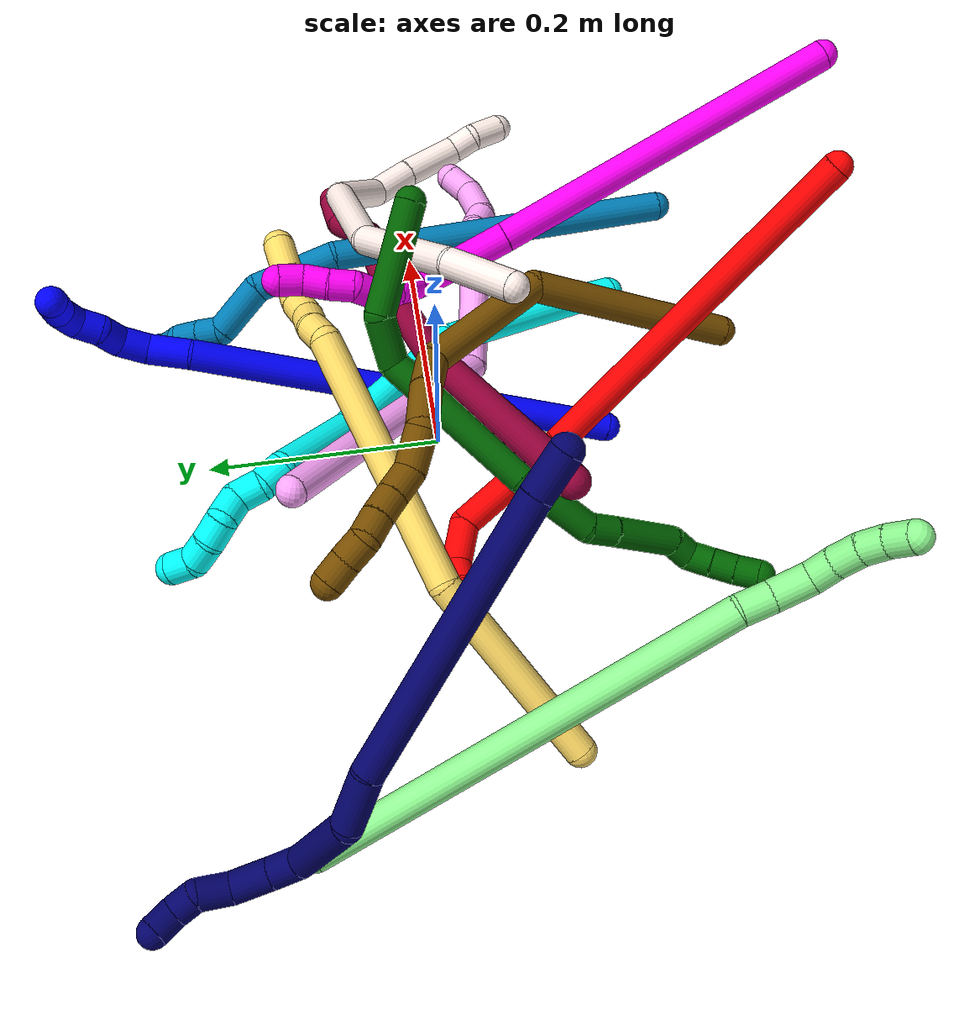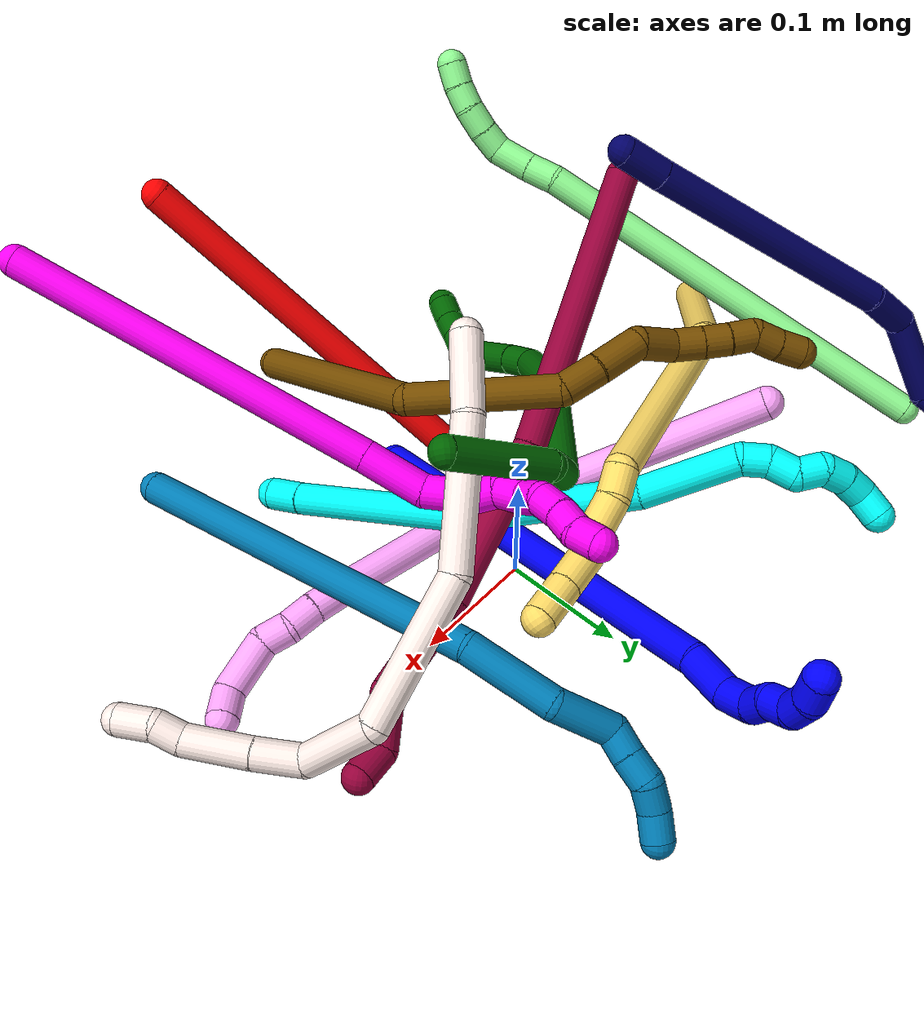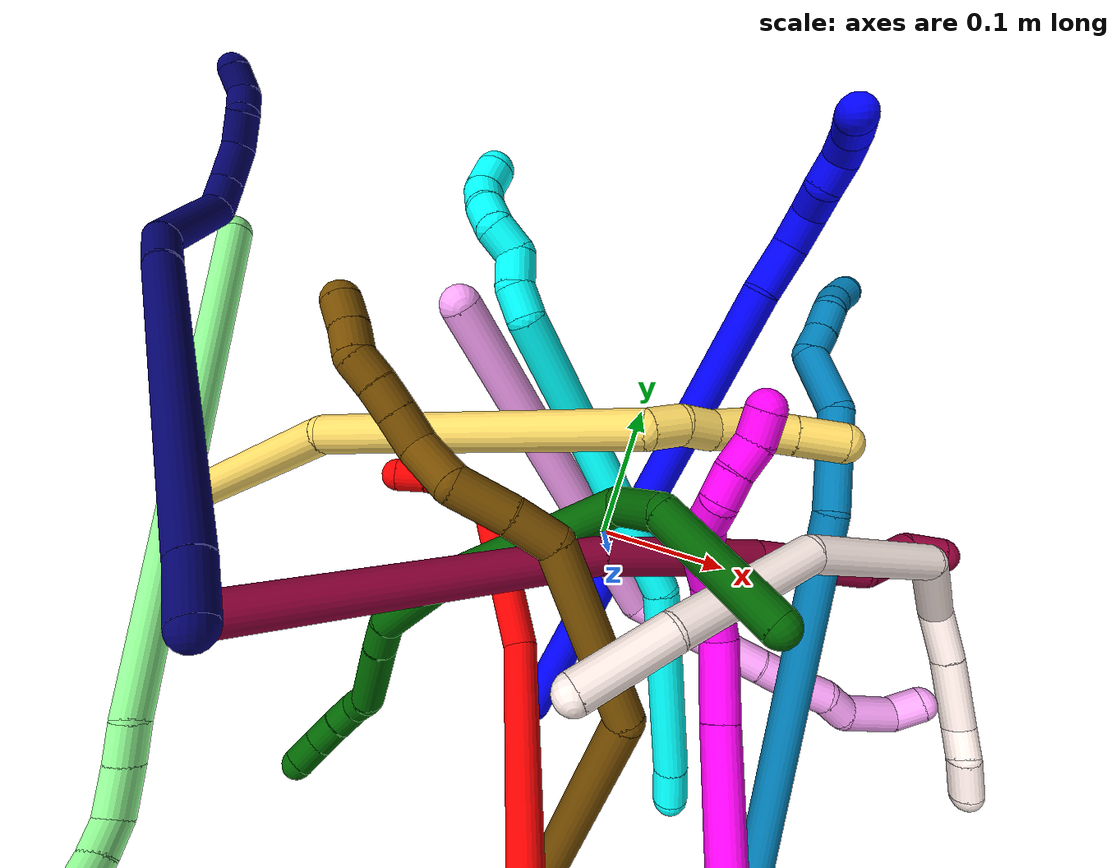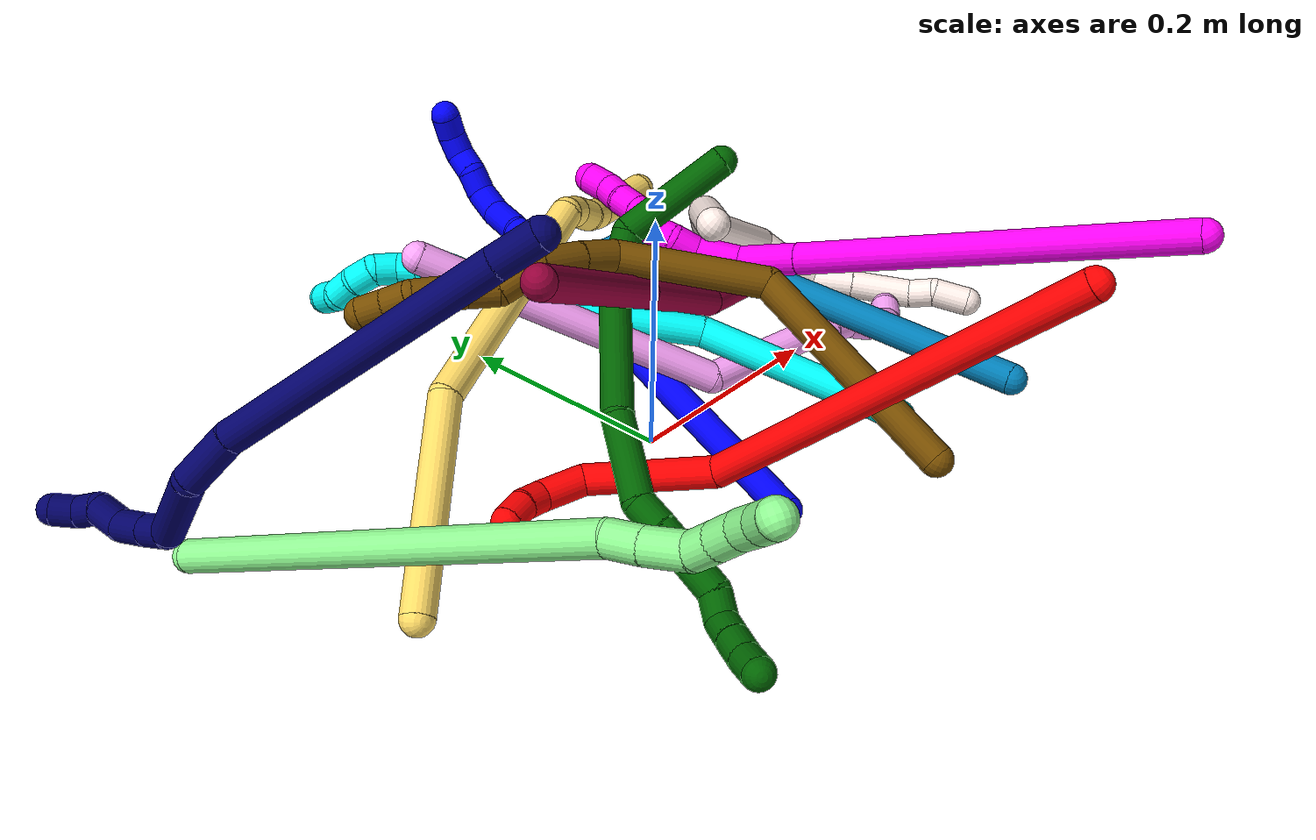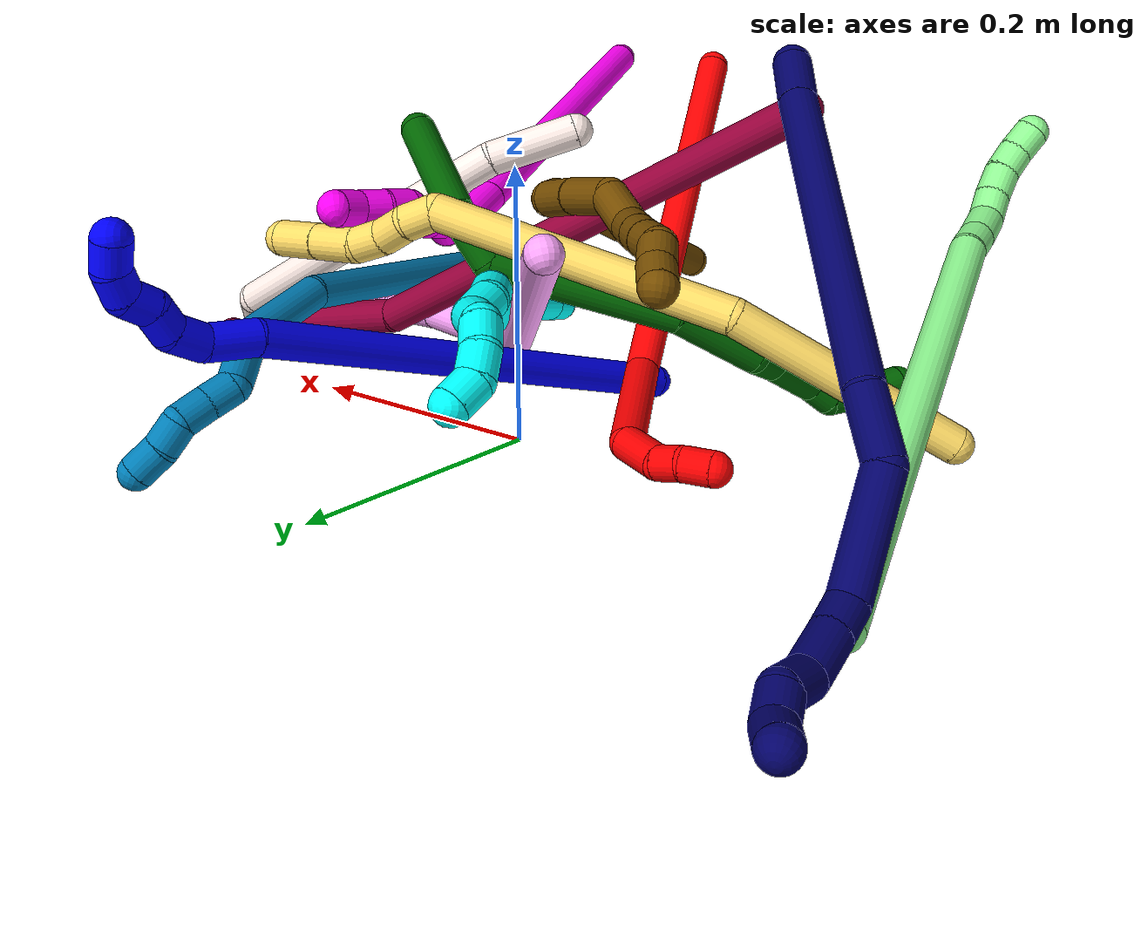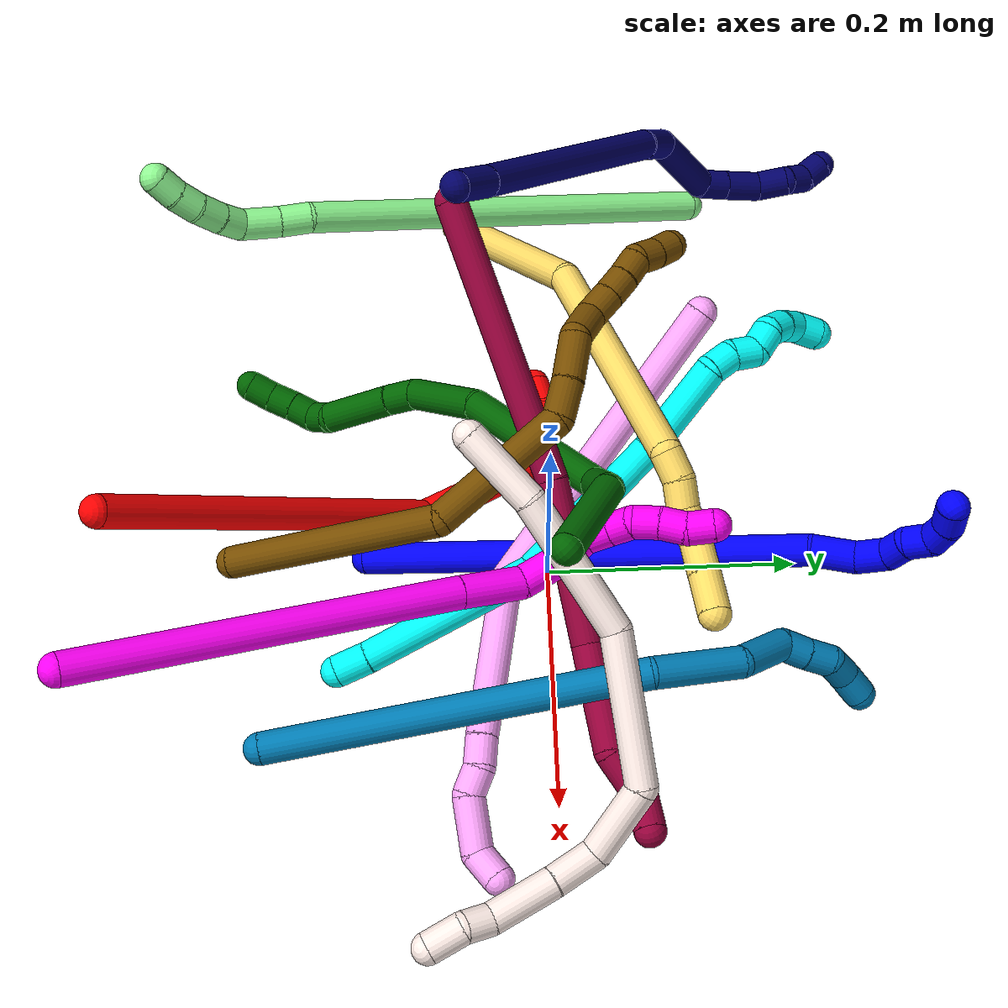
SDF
<sdf version="1.7">
 <world name="default">
  <plugin name="TubeGeneratorPlugin" filename="libtube_generator_plugin.so"/>
  <model name="photoneo_s_sensor">
   <static>1</static>
   <pose>0 0 2 1.57079 1.57079 3.14159</pose>
   <link name="link">
    <inertial><mass>0.1</mass></inertial>
    <sensor name="sensor" type="depth">
     <update_rate>30</update_rate>
     <camera>
      <horizontal_fov>1.22</horizontal_fov>
      <image><width>1920</width><height>1200</height><format>B8G8R8</format></image>
      <clip><near>0.1</near><far>4</far></clip>
      <depth_camera><output>points</output></depth_camera>
     </camera>
     <plugin name="camera_plugin" filename="libgazebo_ros_depth_camera.so">
      <baseline>0.2</baseline>
      <alwaysOn>1</alwaysOn>
      <updateRate>0.0</updateRate>
      <cameraName>camera_ir</cameraName>
      <imageTopicName>/camera/color/image_raw</imageTopicName>
      <cameraInfoTopicName>/camera/color/camera_info</cameraInfoTopicName>
      <depthImageTopicName>/camera/depth/image_raw</depthImageTopicName>
      <depthImageCameraInfoTopicName>/camera/depth/camera_info</depthImageCameraInfoTopicName>
      <pointCloudTopicName>/camera/depth/points</pointCloudTopicName>
      <frameName>fr_optical</frameName>
      <pointCloudCutoff>0.1</pointCloudCutoff>
      <pointCloudCutoffMax>2.0</pointCloudCutoffMax>
      <distortionK1>0</distortionK1>
      <distortionK2>0</distortionK2>
      <distortionK3>0</distortionK3>
      <distortionT1>0</distortionT1>
      <distortionT2>0</distortionT2>
      <CxPrime>0</CxPrime>
      <Cx>0</Cx>
      <Cy>0</Cy>
      <focalLength>0</focalLength>
      <hackBaseline>0</hackBaseline>
     </plugin>
    </sensor>
   </link>
  </model>
  <gravity>0 0 -9.8</gravity>
  <magnetic_field>6e-06 2.3e-05 -4.2e-05</magnetic_field>
  <atmosphere type="adiabatic"/>
  <physics name="default_physics" default="0" type="ode">
   <max_step_size>0.003</max_step_size>
   <real_time_factor>1</real_time_factor>
   <real_time_update_rate>1000</real_time_update_rate>
   <max_contacts>10000</max_contacts>
   <ode>
    <solver>
     <type>quick</type>
     <iters>100</iters>
     <sor>1.3</sor>
     <use_dynamic_moi_rescaling>0</use_dynamic_moi_rescaling>
    </solver>
    <constraints>
     <contact_max_correcting_vel>0</contact_max_correcting_vel>
     <contact_surface_layer>0.001</contact_surface_layer>
     <cfm>0</cfm>
     <erp>0.2</erp>
    </constraints>
   </ode>
  </physics>
  <scene><ambient>0.4 0.4 0.4 1</ambient><background>0.7 0.7 0.7 1</background><shadows>0</shadows></scene>
  <audio><device>default</device></audio>
  <spherical_coordinates>
   <surface_model>EARTH_WGS84</surface_model>
   <latitude_deg>0</latitude_deg>
   <longitude_deg>0</longitude_deg>
   <elevation>0</elevation>
   <heading_deg>0</heading_deg>
  </spherical_coordinates>
  <model name="bin">
   <static>1</static>
   <link name="bottom">
    <collision name="collision-bottom">
     <pose>0 0 -0.01 0 -0 0</pose>
     <geometry><box><size>0.8 0.6 0.02</size></box></geometry>
     <surface>
      <friction><ode><mu>100</mu><mu2>100</mu2></ode></friction>
      <contact><collide_bitmask>65535</collide_bitmask></contact>
     </surface>
    </collision>
   </link>
   <link name="west_wall">
    <collision name="collision-west_wall">
     <pose>-0.41 0 0.1 0 -0 0</pose>
     <geometry><box><size>0.02 0.6 0.2</size></box></geometry>
     <surface>
      <friction><ode><mu>100</mu><mu2>100</mu2></ode></friction>
      <contact><collide_bitmask>65535</collide_bitmask></contact>
     </surface>
    </collision>
   </link>
   <link name="east_wall">
    <collision name="collision-east_wall">
     <pose>0.41 0 0.1 0 -0 0</pose>
     <geometry><box><size>0.02 0.6 0.2</size></box></geometry>
     <surface>
      <friction><ode><mu>100</mu><mu2>100</mu2></ode></friction>
      <contact><collide_bitmask>65535</collide_bitmask></contact>
     </surface>
    </collision>
   </link>
   <link name="south_wall">
    <collision name="collision-south_wall">
     <pose>0 -0.31 0.1 0 -0 0</pose>
     <geometry><box><size>0.8 0.02 0.2</size></box></geometry>
     <surface>
      <friction><ode><mu>100</mu><mu2>100</mu2></ode></friction>
      <contact><collide_bitmask>65535</collide_bitmask></contact>
     </surface>
    </collision>
   </link>
   <link name="north_wall">
    <collision name="collision-north_wall">
     <pose>0 0.31 0.1 0 -0 0</pose>
     <geometry><box><size>0.8 0.02 0.2</size></box></geometry>
     <surface>
      <friction><ode><mu>100</mu><mu2>100</mu2></ode></friction>
      <contact><collide_bitmask>65535</collide_bitmask></contact>
     </surface>
    </collision>
   </link>
  </model>
  <model name="1">
   <static>0</static>
   <link name="1">
    <collision name="collision-cylinder-e_1_1_4">
     <pose>0.023298 0.153232 0.091467 -1.03265 0.129821 -0.073769</pose>
     <geometry><cylinder><radius>0.0125</radius><length>0.35994</length></cylinder></geometry>
     <surface>
      <friction><ode><mu>1.16</mu><mu2>1.16</mu2><slip1>0</slip1><slip2>0</slip2></ode></friction>
      <contact><ode><kp>1e+06</kp><kd>1</kd><max_vel>0</max_vel><min_depth>0.001</min_depth></ode></contact>
     </surface>
    </collision>
    <visual name="visual-cylinder-e_1_1_4">
     <pose>0.023298 0.153232 0.091467 -1.03265 0.129821 -0.073769</pose>
     <geometry><cylinder><radius>0.0125</radius><length>0.35994</length></cylinder></geometry>
     <material><ambient>0 0 1 1</ambient></material>
    </visual>
    <collision name="collision-cylinder-e_2_4_5">
     <pose>0.051639 0.319088 0.193872 -0.856778 0.29319 -0.134655</pose>
     <geometry><cylinder><radius>0.0125</radius><length>0.034896</length></cylinder></geometry>
     <surface>
      <friction><ode><mu>1.16</mu><mu2>1.16</mu2><slip1>0</slip1><slip2>0</slip2></ode></friction>
      <contact><ode><kp>1e+06</kp><kd>1</kd><max_vel>0</max_vel><min_depth>0.001</min_depth></ode></contact>
     </surface>
    </collision>
    <visual name="visual-cylinder-e_2_4_5">
     <pose>0.051639 0.319088 0.193872 -0.856778 0.29319 -0.134655</pose>
     <geometry><cylinder><radius>0.0125</radius><length>0.034896</length></cylinder></geometry>
     <material><ambient>0 0 1 1</ambient></material>
    </visual>
    <collision name="collision-cylinder-e_3_5_6">
     <pose>0.056255 0.342826 0.210297 -1.11231 -0.034473 0.02143</pose>
     <geometry><cylinder><radius>0.0125</radius><length>0.024803</length></cylinder></geometry>
     <surface>
      <friction><ode><mu>1.16</mu><mu2>1.16</mu2><slip1>0</slip1><slip2>0</slip2></ode></friction>
      <contact><ode><kp>1e+06</kp><kd>1</kd><max_vel>0</max_vel><min_depth>0.001</min_depth></ode></contact>
     </surface>
    </collision>
    <visual name="visual-cylinder-e_3_5_6">
     <pose>0.056255 0.342826 0.210297 -1.11231 -0.034473 0.02143</pose>
     <geometry><cylinder><radius>0.0125</radius><length>0.024803</length></cylinder></geometry>
     <material><ambient>0 0 1 1</ambient></material>
    </visual>
    <collision name="collision-cylinder-e_4_6_7">
     <pose>0.051113 0.36285 0.217079 -1.42626 -0.4823 0.419214</pose>
     <geometry><cylinder><radius>0.0125</radius><length>0.020328</length></cylinder></geometry>
     <surface>
      <friction><ode><mu>1.16</mu><mu2>1.16</mu2><slip1>0</slip1><slip2>0</slip2></ode></friction>
      <contact><ode><kp>1e+06</kp><kd>1</kd><max_vel>0</max_vel><min_depth>0.001</min_depth></ode></contact>
     </surface>
    </collision>
    <visual name="visual-cylinder-e_4_6_7">
     <pose>0.051113 0.36285 0.217079 -1.42626 -0.4823 0.419214</pose>
     <geometry><cylinder><radius>0.0125</radius><length>0.020328</length></cylinder></geometry>
     <material><ambient>0 0 1 1</ambient></material>
    </visual>
    <collision name="collision-cylinder-e_5_7_8">
     <pose>0.045478 0.380734 0.222697 -1.12203 -0.092137 0.05792</pose>
     <geometry><cylinder><radius>0.0125</radius><length>0.020003</length></cylinder></geometry>
     <surface>
      <friction><ode><mu>1.16</mu><mu2>1.16</mu2><slip1>0</slip1><slip2>0</slip2></ode></friction>
      <contact><ode><kp>1e+06</kp><kd>1</kd><max_vel>0</max_vel><min_depth>0.001</min_depth></ode></contact>
     </surface>
    </collision>
    <visual name="visual-cylinder-e_5_7_8">
     <pose>0.045478 0.380734 0.222697 -1.12203 -0.092137 0.05792</pose>
     <geometry><cylinder><radius>0.0125</radius><length>0.020003</length></cylinder></geometry>
     <material><ambient>0 0 1 1</ambient></material>
    </visual>
    <collision name="collision-cylinder-e_6_8_9">
     <pose>0.03912 0.398105 0.226719 -1.60634 -0.574336 0.59394</pose>
     <geometry><cylinder><radius>0.0125</radius><length>0.020018</length></cylinder></geometry>
     <surface>
      <friction><ode><mu>1.16</mu><mu2>1.16</mu2><slip1>0</slip1><slip2>0</slip2></ode></friction>
      <contact><ode><kp>1e+06</kp><kd>1</kd><max_vel>0</max_vel><min_depth>0.001</min_depth></ode></contact>
     </surface>
    </collision>
    <visual name="visual-cylinder-e_6_8_9">
     <pose>0.03912 0.398105 0.226719 -1.60634 -0.574336 0.59394</pose>
     <geometry><cylinder><radius>0.0125</radius><length>0.020018</length></cylinder></geometry>
     <material><ambient>0 0 1 1</ambient></material>
    </visual>
    <collision name="collision-cylinder-e_7_9_2">
     <pose>0.026614 0.412855 0.22329 -2.02862 -0.784482 1.17371</pose>
     <geometry><cylinder><radius>0.0125</radius><length>0.020013</length></cylinder></geometry>
     <surface>
      <friction><ode><mu>1.16</mu><mu2>1.16</mu2><slip1>0</slip1><slip2>0</slip2></ode></friction>
      <contact><ode><kp>1e+06</kp><kd>1</kd><max_vel>0</max_vel><min_depth>0.001</min_depth></ode></contact>
     </surface>
    </collision>
    <visual name="visual-cylinder-e_7_9_2">
     <pose>0.026614 0.412855 0.22329 -2.02862 -0.784482 1.17371</pose>
     <geometry><cylinder><radius>0.0125</radius><length>0.020013</length></cylinder></geometry>
     <material><ambient>0 0 1 1</ambient></material>
    </visual>
    <collision name="collision-sphere-2">
     <pose>0.019545 0.419208 0.22016 0 -0 0</pose>
     <geometry><sphere><radius>0.0125</radius></sphere></geometry>
     <surface>
      <friction><ode><mu>1.16</mu><mu2>1.16</mu2><slip1>0</slip1><slip2>0</slip2></ode></friction>
      <contact><ode><kp>1e+06</kp><kd>1</kd><max_vel>0</max_vel><min_depth>0.001</min_depth></ode></contact>
     </surface>
    </collision>
    <visual name="visual-sphere-2">
     <pose>0.019545 0.419208 0.22016 0 -0 0</pose>
     <geometry><sphere><radius>0.0125</radius></sphere></geometry>
     <material><ambient>0 0 1 1</ambient></material>
    </visual>
    <collision name="collision-sphere-9">
     <pose>0.033683 0.406502 0.226421 0 -0 0</pose>
     <geometry><sphere><radius>0.0125</radius></sphere></geometry>
     <surface>
      <friction><ode><mu>1.16</mu><mu2>1.16</mu2><slip1>0</slip1><slip2>0</slip2></ode></friction>
      <contact><ode><kp>1e+06</kp><kd>1</kd><max_vel>0</max_vel><min_depth>0.001</min_depth></ode></contact>
     </surface>
    </collision>
    <visual name="visual-sphere-9">
     <pose>0.033683 0.406502 0.226421 0 -0 0</pose>
     <geometry><sphere><radius>0.0125</radius></sphere></geometry>
     <material><ambient>0 0 1 1</ambient></material>
    </visual>
    <collision name="collision-sphere-4">
     <pose>0.046597 0.306465 0.182934 0 -0 0</pose>
     <geometry><sphere><radius>0.0125</radius></sphere></geometry>
     <surface>
      <friction><ode><mu>1.16</mu><mu2>1.16</mu2><slip1>0</slip1><slip2>0</slip2></ode></friction>
      <contact><ode><kp>1e+06</kp><kd>1</kd><max_vel>0</max_vel><min_depth>0.001</min_depth></ode></contact>
     </surface>
    </collision>
    <visual name="visual-sphere-4">
     <pose>0.046597 0.306465 0.182934 0 -0 0</pose>
     <geometry><sphere><radius>0.0125</radius></sphere></geometry>
     <material><ambient>0 0 1 1</ambient></material>
    </visual>
    <collision name="collision-sphere-1">
     <geometry><sphere><radius>0.0125</radius></sphere></geometry>
     <surface>
      <friction><ode><mu>1.16</mu><mu2>1.16</mu2><slip1>0</slip1><slip2>0</slip2></ode></friction>
      <contact><ode><kp>1e+06</kp><kd>1</kd><max_vel>0</max_vel><min_depth>0.001</min_depth></ode></contact>
     </surface>
    </collision>
    <visual name="visual-sphere-1">
     <geometry><sphere><radius>0.0125</radius></sphere></geometry>
     <material><ambient>0 0 1 1</ambient></material>
    </visual>
    <collision name="collision-sphere-8">
     <pose>0.044558 0.389707 0.227018 0 -0 0</pose>
     <geometry><sphere><radius>0.0125</radius></sphere></geometry>
     <surface>
      <friction><ode><mu>1.16</mu><mu2>1.16</mu2><slip1>0</slip1><slip2>0</slip2></ode></friction>
      <contact><ode><kp>1e+06</kp><kd>1</kd><max_vel>0</max_vel><min_depth>0.001</min_depth></ode></contact>
     </surface>
    </collision>
    <visual name="visual-sphere-8">
     <pose>0.044558 0.389707 0.227018 0 -0 0</pose>
     <geometry><sphere><radius>0.0125</radius></sphere></geometry>
     <material><ambient>0 0 1 1</ambient></material>
    </visual>
    <collision name="collision-sphere-5">
     <pose>0.056682 0.331712 0.204811 0 -0 0</pose>
     <geometry><sphere><radius>0.0125</radius></sphere></geometry>
     <surface>
      <friction><ode><mu>1.16</mu><mu2>1.16</mu2><slip1>0</slip1><slip2>0</slip2></ode></friction>
      <contact><ode><kp>1e+06</kp><kd>1</kd><max_vel>0</max_vel><min_depth>0.001</min_depth></ode></contact>
     </surface>
    </collision>
    <visual name="visual-sphere-5">
     <pose>0.056682 0.331712 0.204811 0 -0 0</pose>
     <geometry><sphere><radius>0.0125</radius></sphere></geometry>
     <material><ambient>0 0 1 1</ambient></material>
    </visual>
    <collision name="collision-sphere-6">
     <pose>0.055827 0.35394 0.215782 0 -0 0</pose>
     <geometry><sphere><radius>0.0125</radius></sphere></geometry>
     <surface>
      <friction><ode><mu>1.16</mu><mu2>1.16</mu2><slip1>0</slip1><slip2>0</slip2></ode></friction>
      <contact><ode><kp>1e+06</kp><kd>1</kd><max_vel>0</max_vel><min_depth>0.001</min_depth></ode></contact>
     </surface>
    </collision>
    <visual name="visual-sphere-6">
     <pose>0.055827 0.35394 0.215782 0 -0 0</pose>
     <geometry><sphere><radius>0.0125</radius></sphere></geometry>
     <material><ambient>0 0 1 1</ambient></material>
    </visual>
    <collision name="collision-sphere-7">
     <pose>0.046398 0.371761 0.218376 0 -0 0</pose>
     <geometry><sphere><radius>0.0125</radius></sphere></geometry>
     <surface>
      <friction><ode><mu>1.16</mu><mu2>1.16</mu2><slip1>0</slip1><slip2>0</slip2></ode></friction>
      <contact><ode><kp>1e+06</kp><kd>1</kd><max_vel>0</max_vel><min_depth>0.001</min_depth></ode></contact>
     </surface>
    </collision>
    <visual name="visual-sphere-7">
     <pose>0.046398 0.371761 0.218376 0 -0 0</pose>
     <geometry><sphere><radius>0.0125</radius></sphere></geometry>
     <material><ambient>0 0 1 1</ambient></material>
    </visual>
    <inertial>
     <pose>0.029695 0.212031 0.125557 0 -0 0</pose>
     <mass>0.5</mass>
     <inertia>
      <ixx>0.003586</ixx>
      <ixy>0</ixy>
      <ixz>0</ixz>
      <iyy>0.001781</iyy>
      <iyz>0</iyz>
      <izz>-0.003817</izz>
     </inertia>
    </inertial>
   </link>
   <pose>-0.01263 -0.145416 0.011445 1.7963 0.994048 2.20487</pose>
  </model>
  <model name="2">
   <static>0</static>
   <link name="2">
    <collision name="collision-cylinder-e_1_1_4">
     <pose>0.017919 0.005559 -0.15616 -3.10601 0.114174 -2.53795</pose>
     <geometry><cylinder><radius>0.0125</radius><length>0.314567</length></cylinder></geometry>
     <surface>
      <friction><ode><mu>1.16</mu><mu2>1.16</mu2><slip1>0</slip1><slip2>0</slip2></ode></friction>
      <contact><ode><kp>1e+06</kp><kd>1</kd><max_vel>0</max_vel><min_depth>0.001</min_depth></ode></contact>
     </surface>
    </collision>
    <visual name="visual-cylinder-e_1_1_4">
     <pose>0.017919 0.005559 -0.15616 -3.10601 0.114174 -2.53795</pose>
     <geometry><cylinder><radius>0.0125</radius><length>0.314567</length></cylinder></geometry>
     <material><ambient>1 0 0 1</ambient></material>
    </visual>
    <collision name="collision-cylinder-e_2_4_5">
     <pose>0.039377 0.038629 -0.356896 -2.58863 0.067471 -0.236766</pose>
     <geometry><cylinder><radius>0.0125</radius><length>0.105003</length></cylinder></geometry>
     <surface>
      <friction><ode><mu>1.16</mu><mu2>1.16</mu2><slip1>0</slip1><slip2>0</slip2></ode></friction>
      <contact><ode><kp>1e+06</kp><kd>1</kd><max_vel>0</max_vel><min_depth>0.001</min_depth></ode></contact>
     </surface>
    </collision>
    <visual name="visual-cylinder-e_2_4_5">
     <pose>0.039377 0.038629 -0.356896 -2.58863 0.067471 -0.236766</pose>
     <geometry><cylinder><radius>0.0125</radius><length>0.105003</length></cylinder></geometry>
     <material><ambient>1 0 0 1</ambient></material>
    </visual>
    <collision name="collision-cylinder-e_3_5_6">
     <pose>0.032251 0.076686 -0.412852 -2.39425 -0.602243 1.33978</pose>
     <geometry><cylinder><radius>0.0125</radius><length>0.037655</length></cylinder></geometry>
     <surface>
      <friction><ode><mu>1.16</mu><mu2>1.16</mu2><slip1>0</slip1><slip2>0</slip2></ode></friction>
      <contact><ode><kp>1e+06</kp><kd>1</kd><max_vel>0</max_vel><min_depth>0.001</min_depth></ode></contact>
     </surface>
    </collision>
    <visual name="visual-cylinder-e_3_5_6">
     <pose>0.032251 0.076686 -0.412852 -2.39425 -0.602243 1.33978</pose>
     <geometry><cylinder><radius>0.0125</radius><length>0.037655</length></cylinder></geometry>
     <material><ambient>1 0 0 1</ambient></material>
    </visual>
    <collision name="collision-cylinder-e_4_6_7">
     <pose>0.013601 0.093097 -0.42639 -1.92326 -0.906701 1.21918</pose>
     <geometry><cylinder><radius>0.0125</radius><length>0.02028</length></cylinder></geometry>
     <surface>
      <friction><ode><mu>1.16</mu><mu2>1.16</mu2><slip1>0</slip1><slip2>0</slip2></ode></friction>
      <contact><ode><kp>1e+06</kp><kd>1</kd><max_vel>0</max_vel><min_depth>0.001</min_depth></ode></contact>
     </surface>
    </collision>
    <visual name="visual-cylinder-e_4_6_7">
     <pose>0.013601 0.093097 -0.42639 -1.92326 -0.906701 1.21918</pose>
     <geometry><cylinder><radius>0.0125</radius><length>0.02028</length></cylinder></geometry>
     <material><ambient>1 0 0 1</ambient></material>
    </visual>
    <collision name="collision-cylinder-e_5_7_2">
     <pose>-0.004696 0.10268 -0.43107 -2.1669 -1.15988 1.78114</pose>
     <geometry><cylinder><radius>0.0125</radius><length>0.022496</length></cylinder></geometry>
     <surface>
      <friction><ode><mu>1.16</mu><mu2>1.16</mu2><slip1>0</slip1><slip2>0</slip2></ode></friction>
      <contact><ode><kp>1e+06</kp><kd>1</kd><max_vel>0</max_vel><min_depth>0.001</min_depth></ode></contact>
     </surface>
    </collision>
    <visual name="visual-cylinder-e_5_7_2">
     <pose>-0.004696 0.10268 -0.43107 -2.1669 -1.15988 1.78114</pose>
     <geometry><cylinder><radius>0.0125</radius><length>0.022496</length></cylinder></geometry>
     <material><ambient>1 0 0 1</ambient></material>
    </visual>
    <collision name="collision-sphere-2">
     <pose>-0.015007 0.106398 -0.433593 0 -0 0</pose>
     <geometry><sphere><radius>0.0125</radius></sphere></geometry>
     <surface>
      <friction><ode><mu>1.16</mu><mu2>1.16</mu2><slip1>0</slip1><slip2>0</slip2></ode></friction>
      <contact><ode><kp>1e+06</kp><kd>1</kd><max_vel>0</max_vel><min_depth>0.001</min_depth></ode></contact>
     </surface>
    </collision>
    <visual name="visual-sphere-2">
     <pose>-0.015007 0.106398 -0.433593 0 -0 0</pose>
     <geometry><sphere><radius>0.0125</radius></sphere></geometry>
     <material><ambient>1 0 0 1</ambient></material>
    </visual>
    <collision name="collision-sphere-7">
     <pose>0.005616 0.098962 -0.428548 0 -0 0</pose>
     <geometry><sphere><radius>0.0125</radius></sphere></geometry>
     <surface>
      <friction><ode><mu>1.16</mu><mu2>1.16</mu2><slip1>0</slip1><slip2>0</slip2></ode></friction>
      <contact><ode><kp>1e+06</kp><kd>1</kd><max_vel>0</max_vel><min_depth>0.001</min_depth></ode></contact>
     </surface>
    </collision>
    <visual name="visual-sphere-7">
     <pose>0.005616 0.098962 -0.428548 0 -0 0</pose>
     <geometry><sphere><radius>0.0125</radius></sphere></geometry>
     <material><ambient>1 0 0 1</ambient></material>
    </visual>
    <collision name="collision-sphere-6">
     <pose>0.021586 0.087231 -0.424233 0 -0 0</pose>
     <geometry><sphere><radius>0.0125</radius></sphere></geometry>
     <surface>
      <friction><ode><mu>1.16</mu><mu2>1.16</mu2><slip1>0</slip1><slip2>0</slip2></ode></friction>
      <contact><ode><kp>1e+06</kp><kd>1</kd><max_vel>0</max_vel><min_depth>0.001</min_depth></ode></contact>
     </surface>
    </collision>
    <visual name="visual-sphere-6">
     <pose>0.021586 0.087231 -0.424233 0 -0 0</pose>
     <geometry><sphere><radius>0.0125</radius></sphere></geometry>
     <material><ambient>1 0 0 1</ambient></material>
    </visual>
    <collision name="collision-sphere-5">
     <pose>0.042917 0.06614 -0.401472 0 -0 0</pose>
     <geometry><sphere><radius>0.0125</radius></sphere></geometry>
     <surface>
      <friction><ode><mu>1.16</mu><mu2>1.16</mu2><slip1>0</slip1><slip2>0</slip2></ode></friction>
      <contact><ode><kp>1e+06</kp><kd>1</kd><max_vel>0</max_vel><min_depth>0.001</min_depth></ode></contact>
     </surface>
    </collision>
    <visual name="visual-sphere-5">
     <pose>0.042917 0.06614 -0.401472 0 -0 0</pose>
     <geometry><sphere><radius>0.0125</radius></sphere></geometry>
     <material><ambient>1 0 0 1</ambient></material>
    </visual>
    <collision name="collision-sphere-1">
     <geometry><sphere><radius>0.0125</radius></sphere></geometry>
     <surface>
      <friction><ode><mu>1.16</mu><mu2>1.16</mu2><slip1>0</slip1><slip2>0</slip2></ode></friction>
      <contact><ode><kp>1e+06</kp><kd>1</kd><max_vel>0</max_vel><min_depth>0.001</min_depth></ode></contact>
     </surface>
    </collision>
    <visual name="visual-sphere-1">
     <geometry><sphere><radius>0.0125</radius></sphere></geometry>
     <material><ambient>1 0 0 1</ambient></material>
    </visual>
    <collision name="collision-sphere-4">
     <pose>0.035837 0.011118 -0.312321 0 -0 0</pose>
     <geometry><sphere><radius>0.0125</radius></sphere></geometry>
     <surface>
      <friction><ode><mu>1.16</mu><mu2>1.16</mu2><slip1>0</slip1><slip2>0</slip2></ode></friction>
      <contact><ode><kp>1e+06</kp><kd>1</kd><max_vel>0</max_vel><min_depth>0.001</min_depth></ode></contact>
     </surface>
    </collision>
    <visual name="visual-sphere-4">
     <pose>0.035837 0.011118 -0.312321 0 -0 0</pose>
     <geometry><sphere><radius>0.0125</radius></sphere></geometry>
     <material><ambient>1 0 0 1</ambient></material>
    </visual>
    <inertial>
     <pose>0.022312 0.02578 -0.240977 0 -0 0</pose>
     <mass>0.5</mass>
     <inertia>
      <ixx>-0.003521</ixx>
      <ixy>0</ixy>
      <ixz>0</ixz>
      <iyy>0.000593</iyy>
      <iyz>0</iyz>
      <izz>-0.000481</izz>
     </inertia>
    </inertial>
   </link>
   <pose>0.055932 -0.318509 0.240014 0.804431 -0.110827 0.645193</pose>
  </model>
  <model name="3">
   <static>0</static>
   <link name="3">
    <collision name="collision-cylinder-e_1_1_4">
     <pose>-0.000333 0.001837 -0.013015 -3.00139 -0.025308 0.356621</pose>
     <geometry><cylinder><radius>0.0125</radius><length>0.026296</length></cylinder></geometry>
     <surface>
      <friction><ode><mu>1.16</mu><mu2>1.16</mu2><slip1>0</slip1><slip2>0</slip2></ode></friction>
      <contact><ode><kp>1e+06</kp><kd>1</kd><max_vel>0</max_vel><min_depth>0.001</min_depth></ode></contact>
     </surface>
    </collision>
    <visual name="visual-cylinder-e_1_1_4">
     <pose>-0.000333 0.001837 -0.013015 -3.00139 -0.025308 0.356621</pose>
     <geometry><cylinder><radius>0.0125</radius><length>0.026296</length></cylinder></geometry>
     <material><ambient>0.003922 1 0.996078 1</ambient></material>
    </visual>
    <collision name="collision-cylinder-e_2_4_5">
     <pose>-0.003725 0.018065 -0.095249 -2.9366 -0.043247 0.414476</pose>
     <geometry><cylinder><radius>0.0125</radius><length>0.141532</length></cylinder></geometry>
     <surface>
      <friction><ode><mu>1.16</mu><mu2>1.16</mu2><slip1>0</slip1><slip2>0</slip2></ode></friction>
      <contact><ode><kp>1e+06</kp><kd>1</kd><max_vel>0</max_vel><min_depth>0.001</min_depth></ode></contact>
     </surface>
    </collision>
    <visual name="visual-cylinder-e_2_4_5">
     <pose>-0.003725 0.018065 -0.095249 -2.9366 -0.043247 0.414476</pose>
     <geometry><cylinder><radius>0.0125</radius><length>0.141532</length></cylinder></geometry>
     <material><ambient>0.003922 1 0.996078 1</ambient></material>
    </visual>
    <collision name="collision-cylinder-e_3_5_6">
     <pose>-0.023561 0.063729 -0.2196 -2.62563 -0.258756 0.916198</pose>
     <geometry><cylinder><radius>0.0125</radius><length>0.131131</length></cylinder></geometry>
     <surface>
      <friction><ode><mu>1.16</mu><mu2>1.16</mu2><slip1>0</slip1><slip2>0</slip2></ode></friction>
      <contact><ode><kp>1e+06</kp><kd>1</kd><max_vel>0</max_vel><min_depth>0.001</min_depth></ode></contact>
     </surface>
    </collision>
    <visual name="visual-cylinder-e_3_5_6">
     <pose>-0.023561 0.063729 -0.2196 -2.62563 -0.258756 0.916198</pose>
     <geometry><cylinder><radius>0.0125</radius><length>0.131131</length></cylinder></geometry>
     <material><ambient>0.003922 1 0.996078 1</ambient></material>
    </visual>
    <collision name="collision-cylinder-e_4_6_7">
     <pose>-0.040079 0.117775 -0.306552 -2.52038 0.006607 -0.020583</pose>
     <geometry><cylinder><radius>0.0125</radius><length>0.078264</length></cylinder></geometry>
     <surface>
      <friction><ode><mu>1.16</mu><mu2>1.16</mu2><slip1>0</slip1><slip2>0</slip2></ode></friction>
      <contact><ode><kp>1e+06</kp><kd>1</kd><max_vel>0</max_vel><min_depth>0.001</min_depth></ode></contact>
     </surface>
    </collision>
    <visual name="visual-cylinder-e_4_6_7">
     <pose>-0.040079 0.117775 -0.306552 -2.52038 0.006607 -0.020583</pose>
     <geometry><cylinder><radius>0.0125</radius><length>0.078264</length></cylinder></geometry>
     <material><ambient>0.003922 1 0.996078 1</ambient></material>
    </visual>
    <collision name="collision-cylinder-e_5_7_8">
     <pose>-0.043916 0.143657 -0.347313 -2.80714 -0.408373 1.77374</pose>
     <geometry><cylinder><radius>0.0125</radius><length>0.020626</length></cylinder></geometry>
     <surface>
      <friction><ode><mu>1.16</mu><mu2>1.16</mu2><slip1>0</slip1><slip2>0</slip2></ode></friction>
      <contact><ode><kp>1e+06</kp><kd>1</kd><max_vel>0</max_vel><min_depth>0.001</min_depth></ode></contact>
     </surface>
    </collision>
    <visual name="visual-cylinder-e_5_7_8">
     <pose>-0.043916 0.143657 -0.347313 -2.80714 -0.408373 1.77374</pose>
     <geometry><cylinder><radius>0.0125</radius><length>0.020626</length></cylinder></geometry>
     <material><ambient>0.003922 1 0.996078 1</ambient></material>
    </visual>
    <collision name="collision-cylinder-e_6_8_9">
     <pose>-0.052341 0.145624 -0.366067 3.02599 -0.412965 -2.60254</pose>
     <geometry><cylinder><radius>0.0125</radius><length>0.021573</length></cylinder></geometry>
     <surface>
      <friction><ode><mu>1.16</mu><mu2>1.16</mu2><slip1>0</slip1><slip2>0</slip2></ode></friction>
      <contact><ode><kp>1e+06</kp><kd>1</kd><max_vel>0</max_vel><min_depth>0.001</min_depth></ode></contact>
     </surface>
    </collision>
    <visual name="visual-cylinder-e_6_8_9">
     <pose>-0.052341 0.145624 -0.366067 3.02599 -0.412965 -2.60254</pose>
     <geometry><cylinder><radius>0.0125</radius><length>0.021573</length></cylinder></geometry>
     <material><ambient>0.003922 1 0.996078 1</ambient></material>
    </visual>
    <collision name="collision-cylinder-e_7_9_10">
     <pose>-0.061018 0.150393 -0.38288 -2.44046 -0.443203 1.1044</pose>
     <geometry><cylinder><radius>0.0125</radius><length>0.020279</length></cylinder></geometry>
     <surface>
      <friction><ode><mu>1.16</mu><mu2>1.16</mu2><slip1>0</slip1><slip2>0</slip2></ode></friction>
      <contact><ode><kp>1e+06</kp><kd>1</kd><max_vel>0</max_vel><min_depth>0.001</min_depth></ode></contact>
     </surface>
    </collision>
    <visual name="visual-cylinder-e_7_9_10">
     <pose>-0.061018 0.150393 -0.38288 -2.44046 -0.443203 1.1044</pose>
     <geometry><cylinder><radius>0.0125</radius><length>0.020279</length></cylinder></geometry>
     <material><ambient>0.003922 1 0.996078 1</ambient></material>
    </visual>
    <collision name="collision-cylinder-e_8_10_11">
     <pose>-0.073393 0.156919 -0.395873 -3.03907 -0.926907 2.93698</pose>
     <geometry><cylinder><radius>0.0125</radius><length>0.020074</length></cylinder></geometry>
     <surface>
      <friction><ode><mu>1.16</mu><mu2>1.16</mu2><slip1>0</slip1><slip2>0</slip2></ode></friction>
      <contact><ode><kp>1e+06</kp><kd>1</kd><max_vel>0</max_vel><min_depth>0.001</min_depth></ode></contact>
     </surface>
    </collision>
    <visual name="visual-cylinder-e_8_10_11">
     <pose>-0.073393 0.156919 -0.395873 -3.03907 -0.926907 2.93698</pose>
     <geometry><cylinder><radius>0.0125</radius><length>0.020074</length></cylinder></geometry>
     <material><ambient>0.003922 1 0.996078 1</ambient></material>
    </visual>
    <collision name="collision-cylinder-e_9_11_12">
     <pose>-0.089598 0.155565 -0.40739 2.79885 -0.948629 -2.49132</pose>
     <geometry><cylinder><radius>0.0125</radius><length>0.020126</length></cylinder></geometry>
     <surface>
      <friction><ode><mu>1.16</mu><mu2>1.16</mu2><slip1>0</slip1><slip2>0</slip2></ode></friction>
      <contact><ode><kp>1e+06</kp><kd>1</kd><max_vel>0</max_vel><min_depth>0.001</min_depth></ode></contact>
     </surface>
    </collision>
    <visual name="visual-cylinder-e_9_11_12">
     <pose>-0.089598 0.155565 -0.40739 2.79885 -0.948629 -2.49132</pose>
     <geometry><cylinder><radius>0.0125</radius><length>0.020126</length></cylinder></geometry>
     <material><ambient>0.003922 1 0.996078 1</ambient></material>
    </visual>
    <collision name="collision-cylinder-e_10_12_2">
     <pose>-0.102105 0.148571 -0.420465 2.55471 -0.445386 -1.28626</pose>
     <geometry><cylinder><radius>0.0125</radius><length>0.0201</length></cylinder></geometry>
     <surface>
      <friction><ode><mu>1.16</mu><mu2>1.16</mu2><slip1>0</slip1><slip2>0</slip2></ode></friction>
      <contact><ode><kp>1e+06</kp><kd>1</kd><max_vel>0</max_vel><min_depth>0.001</min_depth></ode></contact>
     </surface>
    </collision>
    <visual name="visual-cylinder-e_10_12_2">
     <pose>-0.102105 0.148571 -0.420465 2.55471 -0.445386 -1.28626</pose>
     <geometry><cylinder><radius>0.0125</radius><length>0.0201</length></cylinder></geometry>
     <material><ambient>0.003922 1 0.996078 1</ambient></material>
    </visual>
    <collision name="collision-sphere-2">
     <pose>-0.106434 0.143549 -0.428017 0 -0 0</pose>
     <geometry><sphere><radius>0.0125</radius></sphere></geometry>
     <surface>
      <friction><ode><mu>1.16</mu><mu2>1.16</mu2><slip1>0</slip1><slip2>0</slip2></ode></friction>
      <contact><ode><kp>1e+06</kp><kd>1</kd><max_vel>0</max_vel><min_depth>0.001</min_depth></ode></contact>
     </surface>
    </collision>
    <visual name="visual-sphere-2">
     <pose>-0.106434 0.143549 -0.428017 0 -0 0</pose>
     <geometry><sphere><radius>0.0125</radius></sphere></geometry>
     <material><ambient>0.003922 1 0.996078 1</ambient></material>
    </visual>
    <collision name="collision-sphere-12">
     <pose>-0.097775 0.153594 -0.412914 0 -0 0</pose>
     <geometry><sphere><radius>0.0125</radius></sphere></geometry>
     <surface>
      <friction><ode><mu>1.16</mu><mu2>1.16</mu2><slip1>0</slip1><slip2>0</slip2></ode></friction>
      <contact><ode><kp>1e+06</kp><kd>1</kd><max_vel>0</max_vel><min_depth>0.001</min_depth></ode></contact>
     </surface>
    </collision>
    <visual name="visual-sphere-12">
     <pose>-0.097775 0.153594 -0.412914 0 -0 0</pose>
     <geometry><sphere><radius>0.0125</radius></sphere></geometry>
     <material><ambient>0.003922 1 0.996078 1</ambient></material>
    </visual>
    <collision name="collision-sphere-11">
     <pose>-0.081421 0.157535 -0.401867 0 -0 0</pose>
     <geometry><sphere><radius>0.0125</radius></sphere></geometry>
     <surface>
      <friction><ode><mu>1.16</mu><mu2>1.16</mu2><slip1>0</slip1><slip2>0</slip2></ode></friction>
      <contact><ode><kp>1e+06</kp><kd>1</kd><max_vel>0</max_vel><min_depth>0.001</min_depth></ode></contact>
     </surface>
    </collision>
    <visual name="visual-sphere-11">
     <pose>-0.081421 0.157535 -0.401867 0 -0 0</pose>
     <geometry><sphere><radius>0.0125</radius></sphere></geometry>
     <material><ambient>0.003922 1 0.996078 1</ambient></material>
    </visual>
    <collision name="collision-sphere-10">
     <pose>-0.065366 0.156302 -0.389879 0 -0 0</pose>
     <geometry><sphere><radius>0.0125</radius></sphere></geometry>
     <surface>
      <friction><ode><mu>1.16</mu><mu2>1.16</mu2><slip1>0</slip1><slip2>0</slip2></ode></friction>
      <contact><ode><kp>1e+06</kp><kd>1</kd><max_vel>0</max_vel><min_depth>0.001</min_depth></ode></contact>
     </surface>
    </collision>
    <visual name="visual-sphere-10">
     <pose>-0.065366 0.156302 -0.389879 0 -0 0</pose>
     <geometry><sphere><radius>0.0125</radius></sphere></geometry>
     <material><ambient>0.003922 1 0.996078 1</ambient></material>
    </visual>
    <collision name="collision-sphere-9">
     <pose>-0.05667 0.144484 -0.375881 0 -0 0</pose>
     <geometry><sphere><radius>0.0125</radius></sphere></geometry>
     <surface>
      <friction><ode><mu>1.16</mu><mu2>1.16</mu2><slip1>0</slip1><slip2>0</slip2></ode></friction>
      <contact><ode><kp>1e+06</kp><kd>1</kd><max_vel>0</max_vel><min_depth>0.001</min_depth></ode></contact>
     </surface>
    </collision>
    <visual name="visual-sphere-9">
     <pose>-0.05667 0.144484 -0.375881 0 -0 0</pose>
     <geometry><sphere><radius>0.0125</radius></sphere></geometry>
     <material><ambient>0.003922 1 0.996078 1</ambient></material>
    </visual>
    <collision name="collision-sphere-4">
     <pose>-0.000665 0.003674 -0.02603 0 -0 0</pose>
     <geometry><sphere><radius>0.0125</radius></sphere></geometry>
     <surface>
      <friction><ode><mu>1.16</mu><mu2>1.16</mu2><slip1>0</slip1><slip2>0</slip2></ode></friction>
      <contact><ode><kp>1e+06</kp><kd>1</kd><max_vel>0</max_vel><min_depth>0.001</min_depth></ode></contact>
     </surface>
    </collision>
    <visual name="visual-sphere-4">
     <pose>-0.000665 0.003674 -0.02603 0 -0 0</pose>
     <geometry><sphere><radius>0.0125</radius></sphere></geometry>
     <material><ambient>0.003922 1 0.996078 1</ambient></material>
    </visual>
    <collision name="collision-sphere-1">
     <geometry><sphere><radius>0.0125</radius></sphere></geometry>
     <surface>
      <friction><ode><mu>1.16</mu><mu2>1.16</mu2><slip1>0</slip1><slip2>0</slip2></ode></friction>
      <contact><ode><kp>1e+06</kp><kd>1</kd><max_vel>0</max_vel><min_depth>0.001</min_depth></ode></contact>
     </surface>
    </collision>
    <visual name="visual-sphere-1">
     <geometry><sphere><radius>0.0125</radius></sphere></geometry>
     <material><ambient>0.003922 1 0.996078 1</ambient></material>
    </visual>
    <collision name="collision-sphere-8">
     <pose>-0.048012 0.146764 -0.356254 0 -0 0</pose>
     <geometry><sphere><radius>0.0125</radius></sphere></geometry>
     <surface>
      <friction><ode><mu>1.16</mu><mu2>1.16</mu2><slip1>0</slip1><slip2>0</slip2></ode></friction>
      <contact><ode><kp>1e+06</kp><kd>1</kd><max_vel>0</max_vel><min_depth>0.001</min_depth></ode></contact>
     </surface>
    </collision>
    <visual name="visual-sphere-8">
     <pose>-0.048012 0.146764 -0.356254 0 -0 0</pose>
     <geometry><sphere><radius>0.0125</radius></sphere></geometry>
     <material><ambient>0.003922 1 0.996078 1</ambient></material>
    </visual>
    <collision name="collision-sphere-5">
     <pose>-0.006784 0.032457 -0.164468 0 -0 0</pose>
     <geometry><sphere><radius>0.0125</radius></sphere></geometry>
     <surface>
      <friction><ode><mu>1.16</mu><mu2>1.16</mu2><slip1>0</slip1><slip2>0</slip2></ode></friction>
      <contact><ode><kp>1e+06</kp><kd>1</kd><max_vel>0</max_vel><min_depth>0.001</min_depth></ode></contact>
     </surface>
    </collision>
    <visual name="visual-sphere-5">
     <pose>-0.006784 0.032457 -0.164468 0 -0 0</pose>
     <geometry><sphere><radius>0.0125</radius></sphere></geometry>
     <material><ambient>0.003922 1 0.996078 1</ambient></material>
    </visual>
    <collision name="collision-sphere-6">
     <pose>-0.040338 0.095 -0.274732 0 -0 0</pose>
     <geometry><sphere><radius>0.0125</radius></sphere></geometry>
     <surface>
      <friction><ode><mu>1.16</mu><mu2>1.16</mu2><slip1>0</slip1><slip2>0</slip2></ode></friction>
      <contact><ode><kp>1e+06</kp><kd>1</kd><max_vel>0</max_vel><min_depth>0.001</min_depth></ode></contact>
     </surface>
    </collision>
    <visual name="visual-sphere-6">
     <pose>-0.040338 0.095 -0.274732 0 -0 0</pose>
     <geometry><sphere><radius>0.0125</radius></sphere></geometry>
     <material><ambient>0.003922 1 0.996078 1</ambient></material>
    </visual>
    <collision name="collision-sphere-7">
     <pose>-0.039821 0.14055 -0.338372 0 -0 0</pose>
     <geometry><sphere><radius>0.0125</radius></sphere></geometry>
     <surface>
      <friction><ode><mu>1.16</mu><mu2>1.16</mu2><slip1>0</slip1><slip2>0</slip2></ode></friction>
      <contact><ode><kp>1e+06</kp><kd>1</kd><max_vel>0</max_vel><min_depth>0.001</min_depth></ode></contact>
     </surface>
    </collision>
    <visual name="visual-sphere-7">
     <pose>-0.039821 0.14055 -0.338372 0 -0 0</pose>
     <geometry><sphere><radius>0.0125</radius></sphere></geometry>
     <material><ambient>0.003922 1 0.996078 1</ambient></material>
    </visual>
    <inertial>
     <pose>-0.030727 0.077202 -0.228067 0 -0 0</pose>
     <mass>0.5</mass>
     <inertia>
      <ixx>0.000615</ixx>
      <ixy>0</ixy>
      <ixz>0</ixz>
      <iyy>-7.5e-05</iyy>
      <iyz>0</iyz>
      <izz>-0.000136</izz>
     </inertia>
    </inertial>
   </link>
   <pose>0.101755 -0.166551 0.0508 1.94461 -1.01394 -0.143067</pose>
  </model>
  <model name="4">
   <static>0</static>
   <link name="4">
    <collision name="collision-cylinder-e_1_1_4">
     <pose>0.093054 -0.086109 0.011975 1.43261 0.819368 0.722869</pose>
     <geometry><cylinder><radius>0.0125</radius><length>0.254693</length></cylinder></geometry>
     <surface>
      <friction><ode><mu>1.16</mu><mu2>1.16</mu2><slip1>0</slip1><slip2>0</slip2></ode></friction>
      <contact><ode><kp>1e+06</kp><kd>1</kd><max_vel>0</max_vel><min_depth>0.001</min_depth></ode></contact>
     </surface>
    </collision>
    <visual name="visual-cylinder-e_1_1_4">
     <pose>0.093054 -0.086109 0.011975 1.43261 0.819368 0.722869</pose>
     <geometry><cylinder><radius>0.0125</radius><length>0.254693</length></cylinder></geometry>
     <material><ambient>1 0.65098 0.996078 1</ambient></material>
    </visual>
    <collision name="collision-cylinder-e_2_4_5">
     <pose>0.227682 -0.177583 0.050871 0.196751 0.987242 0.106105</pose>
     <geometry><cylinder><radius>0.0125</radius><length>0.099638</length></cylinder></geometry>
     <surface>
      <friction><ode><mu>1.16</mu><mu2>1.16</mu2><slip1>0</slip1><slip2>0</slip2></ode></friction>
      <contact><ode><kp>1e+06</kp><kd>1</kd><max_vel>0</max_vel><min_depth>0.001</min_depth></ode></contact>
     </surface>
    </collision>
    <visual name="visual-cylinder-e_2_4_5">
     <pose>0.227682 -0.177583 0.050871 0.196751 0.987242 0.106105</pose>
     <geometry><cylinder><radius>0.0125</radius><length>0.099638</length></cylinder></geometry>
     <material><ambient>1 0.65098 0.996078 1</ambient></material>
    </visual>
    <collision name="collision-cylinder-e_3_5_6">
     <pose>0.283322 -0.185376 0.085144 0.318862 1.06758 0.189497</pose>
     <geometry><cylinder><radius>0.0125</radius><length>0.032111</length></cylinder></geometry>
     <surface>
      <friction><ode><mu>1.16</mu><mu2>1.16</mu2><slip1>0</slip1><slip2>0</slip2></ode></friction>
      <contact><ode><kp>1e+06</kp><kd>1</kd><max_vel>0</max_vel><min_depth>0.001</min_depth></ode></contact>
     </surface>
    </collision>
    <visual name="visual-cylinder-e_3_5_6">
     <pose>0.283322 -0.185376 0.085144 0.318862 1.06758 0.189497</pose>
     <geometry><cylinder><radius>0.0125</radius><length>0.032111</length></cylinder></geometry>
     <material><ambient>1 0.65098 0.996078 1</ambient></material>
    </visual>
    <collision name="collision-cylinder-e_4_6_7">
     <pose>0.307924 -0.188821 0.097094 0.217675 1.15052 0.141468</pose>
     <geometry><cylinder><radius>0.0125</radius><length>0.023084</length></cylinder></geometry>
     <surface>
      <friction><ode><mu>1.16</mu><mu2>1.16</mu2><slip1>0</slip1><slip2>0</slip2></ode></friction>
      <contact><ode><kp>1e+06</kp><kd>1</kd><max_vel>0</max_vel><min_depth>0.001</min_depth></ode></contact>
     </surface>
    </collision>
    <visual name="visual-cylinder-e_4_6_7">
     <pose>0.307924 -0.188821 0.097094 0.217675 1.15052 0.141468</pose>
     <geometry><cylinder><radius>0.0125</radius><length>0.023084</length></cylinder></geometry>
     <material><ambient>1 0.65098 0.996078 1</ambient></material>
    </visual>
    <collision name="collision-cylinder-e_5_7_8">
     <pose>0.328001 -0.194488 0.104576 1.01579 1.04998 0.62373</pose>
     <geometry><cylinder><radius>0.0125</radius><length>0.021994</length></cylinder></geometry>
     <surface>
      <friction><ode><mu>1.16</mu><mu2>1.16</mu2><slip1>0</slip1><slip2>0</slip2></ode></friction>
      <contact><ode><kp>1e+06</kp><kd>1</kd><max_vel>0</max_vel><min_depth>0.001</min_depth></ode></contact>
     </surface>
    </collision>
    <visual name="visual-cylinder-e_5_7_8">
     <pose>0.328001 -0.194488 0.104576 1.01579 1.04998 0.62373</pose>
     <geometry><cylinder><radius>0.0125</radius><length>0.021994</length></cylinder></geometry>
     <material><ambient>1 0.65098 0.996078 1</ambient></material>
    </visual>
    <collision name="collision-cylinder-e_6_8_9">
     <pose>0.359156 -0.197584 0.110367 -0.491111 1.41942 -0.42409</pose>
     <geometry><cylinder><radius>0.0125</radius><length>0.043732</length></cylinder></geometry>
     <surface>
      <friction><ode><mu>1.16</mu><mu2>1.16</mu2><slip1>0</slip1><slip2>0</slip2></ode></friction>
      <contact><ode><kp>1e+06</kp><kd>1</kd><max_vel>0</max_vel><min_depth>0.001</min_depth></ode></contact>
     </surface>
    </collision>
    <visual name="visual-cylinder-e_6_8_9">
     <pose>0.359156 -0.197584 0.110367 -0.491111 1.41942 -0.42409</pose>
     <geometry><cylinder><radius>0.0125</radius><length>0.043732</length></cylinder></geometry>
     <material><ambient>1 0.65098 0.996078 1</ambient></material>
    </visual>
    <collision name="collision-cylinder-e_7_9_2">
     <pose>0.389805 -0.188259 0.116615 -1.16477 0.8183 -0.556342</pose>
     <geometry><cylinder><radius>0.0125</radius><length>0.024748</length></cylinder></geometry>
     <surface>
      <friction><ode><mu>1.16</mu><mu2>1.16</mu2><slip1>0</slip1><slip2>0</slip2></ode></friction>
      <contact><ode><kp>1e+06</kp><kd>1</kd><max_vel>0</max_vel><min_depth>0.001</min_depth></ode></contact>
     </surface>
    </collision>
    <visual name="visual-cylinder-e_7_9_2">
     <pose>0.389805 -0.188259 0.116615 -1.16477 0.8183 -0.556342</pose>
     <geometry><cylinder><radius>0.0125</radius><length>0.024748</length></cylinder></geometry>
     <material><ambient>1 0.65098 0.996078 1</ambient></material>
    </visual>
    <collision name="collision-sphere-2">
     <pose>0.398838 -0.180489 0.119955 0 -0 0</pose>
     <geometry><sphere><radius>0.0125</radius></sphere></geometry>
     <surface>
      <friction><ode><mu>1.16</mu><mu2>1.16</mu2><slip1>0</slip1><slip2>0</slip2></ode></friction>
      <contact><ode><kp>1e+06</kp><kd>1</kd><max_vel>0</max_vel><min_depth>0.001</min_depth></ode></contact>
     </surface>
    </collision>
    <visual name="visual-sphere-2">
     <pose>0.398838 -0.180489 0.119955 0 -0 0</pose>
     <geometry><sphere><radius>0.0125</radius></sphere></geometry>
     <material><ambient>1 0.65098 0.996078 1</ambient></material>
    </visual>
    <collision name="collision-sphere-9">
     <pose>0.380772 -0.196029 0.113275 0 -0 0</pose>
     <geometry><sphere><radius>0.0125</radius></sphere></geometry>
     <surface>
      <friction><ode><mu>1.16</mu><mu2>1.16</mu2><slip1>0</slip1><slip2>0</slip2></ode></friction>
      <contact><ode><kp>1e+06</kp><kd>1</kd><max_vel>0</max_vel><min_depth>0.001</min_depth></ode></contact>
     </surface>
    </collision>
    <visual name="visual-sphere-9">
     <pose>0.380772 -0.196029 0.113275 0 -0 0</pose>
     <geometry><sphere><radius>0.0125</radius></sphere></geometry>
     <material><ambient>1 0.65098 0.996078 1</ambient></material>
    </visual>
    <collision name="collision-sphere-4">
     <pose>0.186108 -0.172217 0.023951 0 -0 0</pose>
     <geometry><sphere><radius>0.0125</radius></sphere></geometry>
     <surface>
      <friction><ode><mu>1.16</mu><mu2>1.16</mu2><slip1>0</slip1><slip2>0</slip2></ode></friction>
      <contact><ode><kp>1e+06</kp><kd>1</kd><max_vel>0</max_vel><min_depth>0.001</min_depth></ode></contact>
     </surface>
    </collision>
    <visual name="visual-sphere-4">
     <pose>0.186108 -0.172217 0.023951 0 -0 0</pose>
     <geometry><sphere><radius>0.0125</radius></sphere></geometry>
     <material><ambient>1 0.65098 0.996078 1</ambient></material>
    </visual>
    <collision name="collision-sphere-1">
     <geometry><sphere><radius>0.0125</radius></sphere></geometry>
     <surface>
      <friction><ode><mu>1.16</mu><mu2>1.16</mu2><slip1>0</slip1><slip2>0</slip2></ode></friction>
      <contact><ode><kp>1e+06</kp><kd>1</kd><max_vel>0</max_vel><min_depth>0.001</min_depth></ode></contact>
     </surface>
    </collision>
    <visual name="visual-sphere-1">
     <geometry><sphere><radius>0.0125</radius></sphere></geometry>
     <material><ambient>1 0.65098 0.996078 1</ambient></material>
    </visual>
    <collision name="collision-sphere-8">
     <pose>0.33754 -0.199139 0.107459 0 -0 0</pose>
     <geometry><sphere><radius>0.0125</radius></sphere></geometry>
     <surface>
      <friction><ode><mu>1.16</mu><mu2>1.16</mu2><slip1>0</slip1><slip2>0</slip2></ode></friction>
      <contact><ode><kp>1e+06</kp><kd>1</kd><max_vel>0</max_vel><min_depth>0.001</min_depth></ode></contact>
     </surface>
    </collision>
    <visual name="visual-sphere-8">
     <pose>0.33754 -0.199139 0.107459 0 -0 0</pose>
     <geometry><sphere><radius>0.0125</radius></sphere></geometry>
     <material><ambient>1 0.65098 0.996078 1</ambient></material>
    </visual>
    <collision name="collision-sphere-5">
     <pose>0.269257 -0.182949 0.077792 0 -0 0</pose>
     <geometry><sphere><radius>0.0125</radius></sphere></geometry>
     <surface>
      <friction><ode><mu>1.16</mu><mu2>1.16</mu2><slip1>0</slip1><slip2>0</slip2></ode></friction>
      <contact><ode><kp>1e+06</kp><kd>1</kd><max_vel>0</max_vel><min_depth>0.001</min_depth></ode></contact>
     </surface>
    </collision>
    <visual name="visual-sphere-5">
     <pose>0.269257 -0.182949 0.077792 0 -0 0</pose>
     <geometry><sphere><radius>0.0125</radius></sphere></geometry>
     <material><ambient>1 0.65098 0.996078 1</ambient></material>
    </visual>
    <collision name="collision-sphere-6">
     <pose>0.297387 -0.187804 0.092496 0 -0 0</pose>
     <geometry><sphere><radius>0.0125</radius></sphere></geometry>
     <surface>
      <friction><ode><mu>1.16</mu><mu2>1.16</mu2><slip1>0</slip1><slip2>0</slip2></ode></friction>
      <contact><ode><kp>1e+06</kp><kd>1</kd><max_vel>0</max_vel><min_depth>0.001</min_depth></ode></contact>
     </surface>
    </collision>
    <visual name="visual-sphere-6">
     <pose>0.297387 -0.187804 0.092496 0 -0 0</pose>
     <geometry><sphere><radius>0.0125</radius></sphere></geometry>
     <material><ambient>1 0.65098 0.996078 1</ambient></material>
    </visual>
    <collision name="collision-sphere-7">
     <pose>0.318462 -0.189838 0.101692 0 -0 0</pose>
     <geometry><sphere><radius>0.0125</radius></sphere></geometry>
     <surface>
      <friction><ode><mu>1.16</mu><mu2>1.16</mu2><slip1>0</slip1><slip2>0</slip2></ode></friction>
      <contact><ode><kp>1e+06</kp><kd>1</kd><max_vel>0</max_vel><min_depth>0.001</min_depth></ode></contact>
     </surface>
    </collision>
    <visual name="visual-sphere-7">
     <pose>0.318462 -0.189838 0.101692 0 -0 0</pose>
     <geometry><sphere><radius>0.0125</radius></sphere></geometry>
     <material><ambient>1 0.65098 0.996078 1</ambient></material>
    </visual>
    <inertial>
     <pose>0.190319 -0.135028 0.046214 0 -0 0</pose>
     <mass>0.5</mass>
     <inertia>
      <ixx>0.001425</ixx>
      <ixy>0</ixy>
      <ixz>0</ixz>
      <iyy>0.001527</iyy>
      <iyz>0</iyz>
      <izz>-0.000146</izz>
     </inertia>
    </inertial>
   </link>
   <pose>-0.13107 0.12146 0.177429 0.311577 0.505118 0.09946</pose>
  </model>
  <model name="5">
   <static>0</static>
   <link name="5">
    <collision name="collision-cylinder-e_1_1_4">
     <pose>0.047104 0.058043 -0.031498 -2.06799 0.619586 -0.98701</pose>
     <geometry><cylinder><radius>0.0125</radius><length>0.162233</length></cylinder></geometry>
     <surface>
      <friction><ode><mu>1.16</mu><mu2>1.16</mu2><slip1>0</slip1><slip2>0</slip2></ode></friction>
      <contact><ode><kp>1e+06</kp><kd>1</kd><max_vel>0</max_vel><min_depth>0.001</min_depth></ode></contact>
     </surface>
    </collision>
    <visual name="visual-cylinder-e_1_1_4">
     <pose>0.047104 0.058043 -0.031498 -2.06799 0.619586 -0.98701</pose>
     <geometry><cylinder><radius>0.0125</radius><length>0.162233</length></cylinder></geometry>
     <material><ambient>1 0.858824 0.4 1</ambient></material>
    </visual>
    <collision name="collision-cylinder-e_2_4_5">
     <pose>0.182998 0.157939 -0.098223 -2.27045 1.01861 -1.75209</pose>
     <geometry><cylinder><radius>0.0125</radius><length>0.208578</length></cylinder></geometry>
     <surface>
      <friction><ode><mu>1.16</mu><mu2>1.16</mu2><slip1>0</slip1><slip2>0</slip2></ode></friction>
      <contact><ode><kp>1e+06</kp><kd>1</kd><max_vel>0</max_vel><min_depth>0.001</min_depth></ode></contact>
     </surface>
    </collision>
    <visual name="visual-cylinder-e_2_4_5">
     <pose>0.182998 0.157939 -0.098223 -2.27045 1.01861 -1.75209</pose>
     <geometry><cylinder><radius>0.0125</radius><length>0.208578</length></cylinder></geometry>
     <material><ambient>1 0.858824 0.4 1</ambient></material>
    </visual>
    <collision name="collision-cylinder-e_3_5_6">
     <pose>0.280124 0.198207 -0.140764 2.92828 0.839322 2.67056</pose>
     <geometry><cylinder><radius>0.0125</radius><length>0.022407</length></cylinder></geometry>
     <surface>
      <friction><ode><mu>1.16</mu><mu2>1.16</mu2><slip1>0</slip1><slip2>0</slip2></ode></friction>
      <contact><ode><kp>1e+06</kp><kd>1</kd><max_vel>0</max_vel><min_depth>0.001</min_depth></ode></contact>
     </surface>
    </collision>
    <visual name="visual-cylinder-e_3_5_6">
     <pose>0.280124 0.198207 -0.140764 2.92828 0.839322 2.67056</pose>
     <geometry><cylinder><radius>0.0125</radius><length>0.022407</length></cylinder></geometry>
     <material><ambient>1 0.858824 0.4 1</ambient></material>
    </visual>
    <collision name="collision-cylinder-e_4_6_7">
     <pose>0.29741 0.19252 -0.153304 2.47605 0.932077 1.93751</pose>
     <geometry><cylinder><radius>0.0125</radius><length>0.022291</length></cylinder></geometry>
     <surface>
      <friction><ode><mu>1.16</mu><mu2>1.16</mu2><slip1>0</slip1><slip2>0</slip2></ode></friction>
      <contact><ode><kp>1e+06</kp><kd>1</kd><max_vel>0</max_vel><min_depth>0.001</min_depth></ode></contact>
     </surface>
    </collision>
    <visual name="visual-cylinder-e_4_6_7">
     <pose>0.29741 0.19252 -0.153304 2.47605 0.932077 1.93751</pose>
     <geometry><cylinder><radius>0.0125</radius><length>0.022291</length></cylinder></geometry>
     <material><ambient>1 0.858824 0.4 1</ambient></material>
    </visual>
    <collision name="collision-cylinder-e_5_7_8">
     <pose>0.314755 0.187227 -0.164863 2.95582 0.916261 2.76818</pose>
     <geometry><cylinder><radius>0.0125</radius><length>0.021168</length></cylinder></geometry>
     <surface>
      <friction><ode><mu>1.16</mu><mu2>1.16</mu2><slip1>0</slip1><slip2>0</slip2></ode></friction>
      <contact><ode><kp>1e+06</kp><kd>1</kd><max_vel>0</max_vel><min_depth>0.001</min_depth></ode></contact>
     </surface>
    </collision>
    <visual name="visual-cylinder-e_5_7_8">
     <pose>0.314755 0.187227 -0.164863 2.95582 0.916261 2.76818</pose>
     <geometry><cylinder><radius>0.0125</radius><length>0.021168</length></cylinder></geometry>
     <material><ambient>1 0.858824 0.4 1</ambient></material>
    </visual>
    <collision name="collision-cylinder-e_6_8_9">
     <pose>0.338096 0.187446 -0.176599 -2.88641 1.21321 -2.77595</pose>
     <geometry><cylinder><radius>0.0125</radius><length>0.031907</length></cylinder></geometry>
     <surface>
      <friction><ode><mu>1.16</mu><mu2>1.16</mu2><slip1>0</slip1><slip2>0</slip2></ode></friction>
      <contact><ode><kp>1e+06</kp><kd>1</kd><max_vel>0</max_vel><min_depth>0.001</min_depth></ode></contact>
     </surface>
    </collision>
    <visual name="visual-cylinder-e_6_8_9">
     <pose>0.338096 0.187446 -0.176599 -2.88641 1.21321 -2.77595</pose>
     <geometry><cylinder><radius>0.0125</radius><length>0.031907</length></cylinder></geometry>
     <material><ambient>1 0.858824 0.4 1</ambient></material>
    </visual>
    <collision name="collision-cylinder-e_7_9_2">
     <pose>0.367812 0.19013 -0.18719 -2.90068 1.22381 -2.79999</pose>
     <geometry><cylinder><radius>0.0125</radius><length>0.031417</length></cylinder></geometry>
     <surface>
      <friction><ode><mu>1.16</mu><mu2>1.16</mu2><slip1>0</slip1><slip2>0</slip2></ode></friction>
      <contact><ode><kp>1e+06</kp><kd>1</kd><max_vel>0</max_vel><min_depth>0.001</min_depth></ode></contact>
     </surface>
    </collision>
    <visual name="visual-cylinder-e_7_9_2">
     <pose>0.367812 0.19013 -0.18719 -2.90068 1.22381 -2.79999</pose>
     <geometry><cylinder><radius>0.0125</radius><length>0.031417</length></cylinder></geometry>
     <material><ambient>1 0.858824 0.4 1</ambient></material>
    </visual>
    <collision name="collision-sphere-2">
     <pose>0.382585 0.191405 -0.192377 0 -0 0</pose>
     <geometry><sphere><radius>0.0125</radius></sphere></geometry>
     <surface>
      <friction><ode><mu>1.16</mu><mu2>1.16</mu2><slip1>0</slip1><slip2>0</slip2></ode></friction>
      <contact><ode><kp>1e+06</kp><kd>1</kd><max_vel>0</max_vel><min_depth>0.001</min_depth></ode></contact>
     </surface>
    </collision>
    <visual name="visual-sphere-2">
     <pose>0.382585 0.191405 -0.192377 0 -0 0</pose>
     <geometry><sphere><radius>0.0125</radius></sphere></geometry>
     <material><ambient>1 0.858824 0.4 1</ambient></material>
    </visual>
    <collision name="collision-sphere-9">
     <pose>0.35304 0.188856 -0.182002 0 -0 0</pose>
     <geometry><sphere><radius>0.0125</radius></sphere></geometry>
     <surface>
      <friction><ode><mu>1.16</mu><mu2>1.16</mu2><slip1>0</slip1><slip2>0</slip2></ode></friction>
      <contact><ode><kp>1e+06</kp><kd>1</kd><max_vel>0</max_vel><min_depth>0.001</min_depth></ode></contact>
     </surface>
    </collision>
    <visual name="visual-sphere-9">
     <pose>0.35304 0.188856 -0.182002 0 -0 0</pose>
     <geometry><sphere><radius>0.0125</radius></sphere></geometry>
     <material><ambient>1 0.858824 0.4 1</ambient></material>
    </visual>
    <collision name="collision-sphere-4">
     <pose>0.094208 0.116086 -0.062995 0 -0 0</pose>
     <geometry><sphere><radius>0.0125</radius></sphere></geometry>
     <surface>
      <friction><ode><mu>1.16</mu><mu2>1.16</mu2><slip1>0</slip1><slip2>0</slip2></ode></friction>
      <contact><ode><kp>1e+06</kp><kd>1</kd><max_vel>0</max_vel><min_depth>0.001</min_depth></ode></contact>
     </surface>
    </collision>
    <visual name="visual-sphere-4">
     <pose>0.094208 0.116086 -0.062995 0 -0 0</pose>
     <geometry><sphere><radius>0.0125</radius></sphere></geometry>
     <material><ambient>1 0.858824 0.4 1</ambient></material>
    </visual>
    <collision name="collision-sphere-1">
     <geometry><sphere><radius>0.0125</radius></sphere></geometry>
     <surface>
      <friction><ode><mu>1.16</mu><mu2>1.16</mu2><slip1>0</slip1><slip2>0</slip2></ode></friction>
      <contact><ode><kp>1e+06</kp><kd>1</kd><max_vel>0</max_vel><min_depth>0.001</min_depth></ode></contact>
     </surface>
    </collision>
    <visual name="visual-sphere-1">
     <geometry><sphere><radius>0.0125</radius></sphere></geometry>
     <material><ambient>1 0.858824 0.4 1</ambient></material>
    </visual>
    <collision name="collision-sphere-8">
     <pose>0.323151 0.186037 -0.171196 0 -0 0</pose>
     <geometry><sphere><radius>0.0125</radius></sphere></geometry>
     <surface>
      <friction><ode><mu>1.16</mu><mu2>1.16</mu2><slip1>0</slip1><slip2>0</slip2></ode></friction>
      <contact><ode><kp>1e+06</kp><kd>1</kd><max_vel>0</max_vel><min_depth>0.001</min_depth></ode></contact>
     </surface>
    </collision>
    <visual name="visual-sphere-8">
     <pose>0.323151 0.186037 -0.171196 0 -0 0</pose>
     <geometry><sphere><radius>0.0125</radius></sphere></geometry>
     <material><ambient>1 0.858824 0.4 1</ambient></material>
    </visual>
    <collision name="collision-sphere-5">
     <pose>0.271787 0.199791 -0.13345 0 -0 0</pose>
     <geometry><sphere><radius>0.0125</radius></sphere></geometry>
     <surface>
      <friction><ode><mu>1.16</mu><mu2>1.16</mu2><slip1>0</slip1><slip2>0</slip2></ode></friction>
      <contact><ode><kp>1e+06</kp><kd>1</kd><max_vel>0</max_vel><min_depth>0.001</min_depth></ode></contact>
     </surface>
    </collision>
    <visual name="visual-sphere-5">
     <pose>0.271787 0.199791 -0.13345 0 -0 0</pose>
     <geometry><sphere><radius>0.0125</radius></sphere></geometry>
     <material><ambient>1 0.858824 0.4 1</ambient></material>
    </visual>
    <collision name="collision-sphere-6">
     <pose>0.288462 0.196623 -0.148078 0 -0 0</pose>
     <geometry><sphere><radius>0.0125</radius></sphere></geometry>
     <surface>
      <friction><ode><mu>1.16</mu><mu2>1.16</mu2><slip1>0</slip1><slip2>0</slip2></ode></friction>
      <contact><ode><kp>1e+06</kp><kd>1</kd><max_vel>0</max_vel><min_depth>0.001</min_depth></ode></contact>
     </surface>
    </collision>
    <visual name="visual-sphere-6">
     <pose>0.288462 0.196623 -0.148078 0 -0 0</pose>
     <geometry><sphere><radius>0.0125</radius></sphere></geometry>
     <material><ambient>1 0.858824 0.4 1</ambient></material>
    </visual>
    <collision name="collision-sphere-7">
     <pose>0.306358 0.188417 -0.158531 0 -0 0</pose>
     <geometry><sphere><radius>0.0125</radius></sphere></geometry>
     <surface>
      <friction><ode><mu>1.16</mu><mu2>1.16</mu2><slip1>0</slip1><slip2>0</slip2></ode></friction>
      <contact><ode><kp>1e+06</kp><kd>1</kd><max_vel>0</max_vel><min_depth>0.001</min_depth></ode></contact>
     </surface>
    </collision>
    <visual name="visual-sphere-7">
     <pose>0.306358 0.188417 -0.158531 0 -0 0</pose>
     <geometry><sphere><radius>0.0125</radius></sphere></geometry>
     <material><ambient>1 0.858824 0.4 1</ambient></material>
    </visual>
    <inertial>
     <pose>0.175446 0.134018 -0.094348 0 -0 0</pose>
     <mass>0.5</mass>
     <inertia>
      <ixx>-0.000524</ixx>
      <ixy>0</ixy>
      <ixz>0</ixz>
      <iyy>2.5e-05</iyy>
      <iyz>0</iyz>
      <izz>-0.001453</izz>
     </inertia>
    </inertial>
   </link>
   <pose>-0.308703 -0.06476 0.04713 1.14616 -0.030011 -0.187992</pose>
  </model>
  <model name="6">
   <static>0</static>
   <link name="6">
    <collision name="collision-cylinder-e_1_1_4">
     <pose>0.034437 -0.029737 0.003249 1.46198 0.855563 0.776207</pose>
     <geometry><cylinder><radius>0.0125</radius><length>0.091231</length></cylinder></geometry>
     <surface>
      <friction><ode><mu>1.16</mu><mu2>1.16</mu2><slip1>0</slip1><slip2>0</slip2></ode></friction>
      <contact><ode><kp>1e+06</kp><kd>1</kd><max_vel>0</max_vel><min_depth>0.001</min_depth></ode></contact>
     </surface>
    </collision>
    <visual name="visual-cylinder-e_1_1_4">
     <pose>0.034437 -0.029737 0.003249 1.46198 0.855563 0.776207</pose>
     <geometry><cylinder><radius>0.0125</radius><length>0.091231</length></cylinder></geometry>
     <material><ambient>0 0.392157 0.003922 1</ambient></material>
    </visual>
    <collision name="collision-cylinder-e_2_4_5">
     <pose>0.072875 -0.079682 0.005902 1.60029 0.195364 0.201175</pose>
     <geometry><cylinder><radius>0.0125</radius><length>0.041216</length></cylinder></geometry>
     <surface>
      <friction><ode><mu>1.16</mu><mu2>1.16</mu2><slip1>0</slip1><slip2>0</slip2></ode></friction>
      <contact><ode><kp>1e+06</kp><kd>1</kd><max_vel>0</max_vel><min_depth>0.001</min_depth></ode></contact>
     </surface>
    </collision>
    <visual name="visual-cylinder-e_2_4_5">
     <pose>0.072875 -0.079682 0.005902 1.60029 0.195364 0.201175</pose>
     <geometry><cylinder><radius>0.0125</radius><length>0.041216</length></cylinder></geometry>
     <material><ambient>0 0.392157 0.003922 1</ambient></material>
    </visual>
    <collision name="collision-cylinder-e_3_5_6">
     <pose>0.078497 -0.149359 -0.041346 2.32688 0.023843 0.055246</pose>
     <geometry><cylinder><radius>0.0125</radius><length>0.136032</length></cylinder></geometry>
     <surface>
      <friction><ode><mu>1.16</mu><mu2>1.16</mu2><slip1>0</slip1><slip2>0</slip2></ode></friction>
      <contact><ode><kp>1e+06</kp><kd>1</kd><max_vel>0</max_vel><min_depth>0.001</min_depth></ode></contact>
     </surface>
    </collision>
    <visual name="visual-cylinder-e_3_5_6">
     <pose>0.078497 -0.149359 -0.041346 2.32688 0.023843 0.055246</pose>
     <geometry><cylinder><radius>0.0125</radius><length>0.136032</length></cylinder></geometry>
     <material><ambient>0 0.392157 0.003922 1</ambient></material>
    </visual>
    <collision name="collision-cylinder-e_4_6_7">
     <pose>0.073008 -0.227415 -0.105046 2.10856 -0.210445 -0.367711</pose>
     <geometry><cylinder><radius>0.0125</radius><length>0.068071</length></cylinder></geometry>
     <surface>
      <friction><ode><mu>1.16</mu><mu2>1.16</mu2><slip1>0</slip1><slip2>0</slip2></ode></friction>
      <contact><ode><kp>1e+06</kp><kd>1</kd><max_vel>0</max_vel><min_depth>0.001</min_depth></ode></contact>
     </surface>
    </collision>
    <visual name="visual-cylinder-e_4_6_7">
     <pose>0.073008 -0.227415 -0.105046 2.10856 -0.210445 -0.367711</pose>
     <geometry><cylinder><radius>0.0125</radius><length>0.068071</length></cylinder></geometry>
     <material><ambient>0 0.392157 0.003922 1</ambient></material>
    </visual>
    <collision name="collision-cylinder-e_5_7_8">
     <pose>0.058312 -0.263604 -0.127163 2.15879 -0.692951 -1.18695</pose>
     <geometry><cylinder><radius>0.0125</radius><length>0.023752</length></cylinder></geometry>
     <surface>
      <friction><ode><mu>1.16</mu><mu2>1.16</mu2><slip1>0</slip1><slip2>0</slip2></ode></friction>
      <contact><ode><kp>1e+06</kp><kd>1</kd><max_vel>0</max_vel><min_depth>0.001</min_depth></ode></contact>
     </surface>
    </collision>
    <visual name="visual-cylinder-e_5_7_8">
     <pose>0.058312 -0.263604 -0.127163 2.15879 -0.692951 -1.18695</pose>
     <geometry><cylinder><radius>0.0125</radius><length>0.023752</length></cylinder></geometry>
     <material><ambient>0 0.392157 0.003922 1</ambient></material>
    </visual>
    <collision name="collision-cylinder-e_6_8_9">
     <pose>0.03219 -0.290943 -0.142845 2.06423 -0.691069 -1.08426</pose>
     <geometry><cylinder><radius>0.0125</radius><length>0.058164</length></cylinder></geometry>
     <surface>
      <friction><ode><mu>1.16</mu><mu2>1.16</mu2><slip1>0</slip1><slip2>0</slip2></ode></friction>
      <contact><ode><kp>1e+06</kp><kd>1</kd><max_vel>0</max_vel><min_depth>0.001</min_depth></ode></contact>
     </surface>
    </collision>
    <visual name="visual-cylinder-e_6_8_9">
     <pose>0.03219 -0.290943 -0.142845 2.06423 -0.691069 -1.08426</pose>
     <geometry><cylinder><radius>0.0125</radius><length>0.058164</length></cylinder></geometry>
     <material><ambient>0 0.392157 0.003922 1</ambient></material>
    </visual>
    <collision name="collision-cylinder-e_7_9_10">
     <pose>0.011265 -0.320187 -0.157418 1.96531 -0.22799 -0.340054</pose>
     <geometry><cylinder><radius>0.0125</radius><length>0.021145</length></cylinder></geometry>
     <surface>
      <friction><ode><mu>1.16</mu><mu2>1.16</mu2><slip1>0</slip1><slip2>0</slip2></ode></friction>
      <contact><ode><kp>1e+06</kp><kd>1</kd><max_vel>0</max_vel><min_depth>0.001</min_depth></ode></contact>
     </surface>
    </collision>
    <visual name="visual-cylinder-e_7_9_10">
     <pose>0.011265 -0.320187 -0.157418 1.96531 -0.22799 -0.340054</pose>
     <geometry><cylinder><radius>0.0125</radius><length>0.021145</length></cylinder></geometry>
     <material><ambient>0 0.392157 0.003922 1</ambient></material>
    </visual>
    <collision name="collision-cylinder-e_8_10_11">
     <pose>0.006654 -0.333592 -0.17034 2.73146 -0.223391 -0.989137</pose>
     <geometry><cylinder><radius>0.0125</radius><length>0.020047</length></cylinder></geometry>
     <surface>
      <friction><ode><mu>1.16</mu><mu2>1.16</mu2><slip1>0</slip1><slip2>0</slip2></ode></friction>
      <contact><ode><kp>1e+06</kp><kd>1</kd><max_vel>0</max_vel><min_depth>0.001</min_depth></ode></contact>
     </surface>
    </collision>
    <visual name="visual-cylinder-e_8_10_11">
     <pose>0.006654 -0.333592 -0.17034 2.73146 -0.223391 -0.989137</pose>
     <geometry><cylinder><radius>0.0125</radius><length>0.020047</length></cylinder></geometry>
     <material><ambient>0 0.392157 0.003922 1</ambient></material>
    </visual>
    <collision name="collision-cylinder-e_9_11_12">
     <pose>0.001727 -0.341744 -0.188041 2.68848 -0.271643 -1.07031</pose>
     <geometry><cylinder><radius>0.0125</radius><length>0.020175</length></cylinder></geometry>
     <surface>
      <friction><ode><mu>1.16</mu><mu2>1.16</mu2><slip1>0</slip1><slip2>0</slip2></ode></friction>
      <contact><ode><kp>1e+06</kp><kd>1</kd><max_vel>0</max_vel><min_depth>0.001</min_depth></ode></contact>
     </surface>
    </collision>
    <visual name="visual-cylinder-e_9_11_12">
     <pose>0.001727 -0.341744 -0.188041 2.68848 -0.271643 -1.07031</pose>
     <geometry><cylinder><radius>0.0125</radius><length>0.020175</length></cylinder></geometry>
     <material><ambient>0 0.392157 0.003922 1</ambient></material>
    </visual>
    <collision name="collision-cylinder-e_10_12_2">
     <pose>-0.003394 -0.348675 -0.206195 2.86463 -0.241756 -1.43374</pose>
     <geometry><cylinder><radius>0.0125</radius><length>0.020167</length></cylinder></geometry>
     <surface>
      <friction><ode><mu>1.16</mu><mu2>1.16</mu2><slip1>0</slip1><slip2>0</slip2></ode></friction>
      <contact><ode><kp>1e+06</kp><kd>1</kd><max_vel>0</max_vel><min_depth>0.001</min_depth></ode></contact>
     </surface>
    </collision>
    <visual name="visual-cylinder-e_10_12_2">
     <pose>-0.003394 -0.348675 -0.206195 2.86463 -0.241756 -1.43374</pose>
     <geometry><cylinder><radius>0.0125</radius><length>0.020167</length></cylinder></geometry>
     <material><ambient>0 0.392157 0.003922 1</ambient></material>
    </visual>
    <collision name="collision-sphere-2">
     <pose>-0.005808 -0.351351 -0.215612 0 -0 0</pose>
     <geometry><sphere><radius>0.0125</radius></sphere></geometry>
     <surface>
      <friction><ode><mu>1.16</mu><mu2>1.16</mu2><slip1>0</slip1><slip2>0</slip2></ode></friction>
      <contact><ode><kp>1e+06</kp><kd>1</kd><max_vel>0</max_vel><min_depth>0.001</min_depth></ode></contact>
     </surface>
    </collision>
    <visual name="visual-sphere-2">
     <pose>-0.005808 -0.351351 -0.215612 0 -0 0</pose>
     <geometry><sphere><radius>0.0125</radius></sphere></geometry>
     <material><ambient>0 0.392157 0.003922 1</ambient></material>
    </visual>
    <collision name="collision-sphere-12">
     <pose>-0.000979 -0.345998 -0.196778 0 -0 0</pose>
     <geometry><sphere><radius>0.0125</radius></sphere></geometry>
     <surface>
      <friction><ode><mu>1.16</mu><mu2>1.16</mu2><slip1>0</slip1><slip2>0</slip2></ode></friction>
      <contact><ode><kp>1e+06</kp><kd>1</kd><max_vel>0</max_vel><min_depth>0.001</min_depth></ode></contact>
     </surface>
    </collision>
    <visual name="visual-sphere-12">
     <pose>-0.000979 -0.345998 -0.196778 0 -0 0</pose>
     <geometry><sphere><radius>0.0125</radius></sphere></geometry>
     <material><ambient>0 0.392157 0.003922 1</ambient></material>
    </visual>
    <collision name="collision-sphere-11">
     <pose>0.004434 -0.33749 -0.179304 0 -0 0</pose>
     <geometry><sphere><radius>0.0125</radius></sphere></geometry>
     <surface>
      <friction><ode><mu>1.16</mu><mu2>1.16</mu2><slip1>0</slip1><slip2>0</slip2></ode></friction>
      <contact><ode><kp>1e+06</kp><kd>1</kd><max_vel>0</max_vel><min_depth>0.001</min_depth></ode></contact>
     </surface>
    </collision>
    <visual name="visual-sphere-11">
     <pose>0.004434 -0.33749 -0.179304 0 -0 0</pose>
     <geometry><sphere><radius>0.0125</radius></sphere></geometry>
     <material><ambient>0 0.392157 0.003922 1</ambient></material>
    </visual>
    <collision name="collision-sphere-10">
     <pose>0.008875 -0.329695 -0.161377 0 -0 0</pose>
     <geometry><sphere><radius>0.0125</radius></sphere></geometry>
     <surface>
      <friction><ode><mu>1.16</mu><mu2>1.16</mu2><slip1>0</slip1><slip2>0</slip2></ode></friction>
      <contact><ode><kp>1e+06</kp><kd>1</kd><max_vel>0</max_vel><min_depth>0.001</min_depth></ode></contact>
     </surface>
    </collision>
    <visual name="visual-sphere-10">
     <pose>0.008875 -0.329695 -0.161377 0 -0 0</pose>
     <geometry><sphere><radius>0.0125</radius></sphere></geometry>
     <material><ambient>0 0.392157 0.003922 1</ambient></material>
    </visual>
    <collision name="collision-sphere-9">
     <pose>0.013654 -0.310679 -0.15346 0 -0 0</pose>
     <geometry><sphere><radius>0.0125</radius></sphere></geometry>
     <surface>
      <friction><ode><mu>1.16</mu><mu2>1.16</mu2><slip1>0</slip1><slip2>0</slip2></ode></friction>
      <contact><ode><kp>1e+06</kp><kd>1</kd><max_vel>0</max_vel><min_depth>0.001</min_depth></ode></contact>
     </surface>
    </collision>
    <visual name="visual-sphere-9">
     <pose>0.013654 -0.310679 -0.15346 0 -0 0</pose>
     <geometry><sphere><radius>0.0125</radius></sphere></geometry>
     <material><ambient>0 0.392157 0.003922 1</ambient></material>
    </visual>
    <collision name="collision-sphere-4">
     <pose>0.068874 -0.059475 0.006498 0 -0 0</pose>
     <geometry><sphere><radius>0.0125</radius></sphere></geometry>
     <surface>
      <friction><ode><mu>1.16</mu><mu2>1.16</mu2><slip1>0</slip1><slip2>0</slip2></ode></friction>
      <contact><ode><kp>1e+06</kp><kd>1</kd><max_vel>0</max_vel><min_depth>0.001</min_depth></ode></contact>
     </surface>
    </collision>
    <visual name="visual-sphere-4">
     <pose>0.068874 -0.059475 0.006498 0 -0 0</pose>
     <geometry><sphere><radius>0.0125</radius></sphere></geometry>
     <material><ambient>0 0.392157 0.003922 1</ambient></material>
    </visual>
    <collision name="collision-sphere-1">
     <geometry><sphere><radius>0.0125</radius></sphere></geometry>
     <surface>
      <friction><ode><mu>1.16</mu><mu2>1.16</mu2><slip1>0</slip1><slip2>0</slip2></ode></friction>
      <contact><ode><kp>1e+06</kp><kd>1</kd><max_vel>0</max_vel><min_depth>0.001</min_depth></ode></contact>
     </surface>
    </collision>
    <visual name="visual-sphere-1">
     <geometry><sphere><radius>0.0125</radius></sphere></geometry>
     <material><ambient>0 0.392157 0.003922 1</ambient></material>
    </visual>
    <collision name="collision-sphere-8">
     <pose>0.050726 -0.271206 -0.132231 0 -0 0</pose>
     <geometry><sphere><radius>0.0125</radius></sphere></geometry>
     <surface>
      <friction><ode><mu>1.16</mu><mu2>1.16</mu2><slip1>0</slip1><slip2>0</slip2></ode></friction>
      <contact><ode><kp>1e+06</kp><kd>1</kd><max_vel>0</max_vel><min_depth>0.001</min_depth></ode></contact>
     </surface>
    </collision>
    <visual name="visual-sphere-8">
     <pose>0.050726 -0.271206 -0.132231 0 -0 0</pose>
     <geometry><sphere><radius>0.0125</radius></sphere></geometry>
     <material><ambient>0 0.392157 0.003922 1</ambient></material>
    </visual>
    <collision name="collision-sphere-5">
     <pose>0.076875 -0.09989 0.005305 0 -0 0</pose>
     <geometry><sphere><radius>0.0125</radius></sphere></geometry>
     <surface>
      <friction><ode><mu>1.16</mu><mu2>1.16</mu2><slip1>0</slip1><slip2>0</slip2></ode></friction>
      <contact><ode><kp>1e+06</kp><kd>1</kd><max_vel>0</max_vel><min_depth>0.001</min_depth></ode></contact>
     </surface>
    </collision>
    <visual name="visual-sphere-5">
     <pose>0.076875 -0.09989 0.005305 0 -0 0</pose>
     <geometry><sphere><radius>0.0125</radius></sphere></geometry>
     <material><ambient>0 0.392157 0.003922 1</ambient></material>
    </visual>
    <collision name="collision-sphere-6">
     <pose>0.080118 -0.198828 -0.087997 0 -0 0</pose>
     <geometry><sphere><radius>0.0125</radius></sphere></geometry>
     <surface>
      <friction><ode><mu>1.16</mu><mu2>1.16</mu2><slip1>0</slip1><slip2>0</slip2></ode></friction>
      <contact><ode><kp>1e+06</kp><kd>1</kd><max_vel>0</max_vel><min_depth>0.001</min_depth></ode></contact>
     </surface>
    </collision>
    <visual name="visual-sphere-6">
     <pose>0.080118 -0.198828 -0.087997 0 -0 0</pose>
     <geometry><sphere><radius>0.0125</radius></sphere></geometry>
     <material><ambient>0 0.392157 0.003922 1</ambient></material>
    </visual>
    <collision name="collision-sphere-7">
     <pose>0.065899 -0.256001 -0.122094 0 -0 0</pose>
     <geometry><sphere><radius>0.0125</radius></sphere></geometry>
     <surface>
      <friction><ode><mu>1.16</mu><mu2>1.16</mu2><slip1>0</slip1><slip2>0</slip2></ode></friction>
      <contact><ode><kp>1e+06</kp><kd>1</kd><max_vel>0</max_vel><min_depth>0.001</min_depth></ode></contact>
     </surface>
    </collision>
    <visual name="visual-sphere-7">
     <pose>0.065899 -0.256001 -0.122094 0 -0 0</pose>
     <geometry><sphere><radius>0.0125</radius></sphere></geometry>
     <material><ambient>0 0.392157 0.003922 1</ambient></material>
    </visual>
    <inertial>
     <pose>0.050777 -0.184726 -0.076519 0 -0 0</pose>
     <mass>0.5</mass>
     <inertia>
      <ixx>0.000305</ixx>
      <ixy>0</ixy>
      <ixz>0</ixz>
      <iyy>-0.000127</iyy>
      <iyz>0</iyz>
      <izz>0.000195</izz>
     </inertia>
    </inertial>
   </link>
   <pose>0.086712 0.00719 0.218569 2.08251 -0.116289 2.38015</pose>
  </model>
  <model name="7">
   <static>0</static>
   <link name="7">
    <collision name="collision-cylinder-e_1_1_4">
     <pose>1.6e-05 0.007731 -0.0161 -2.69391 0.000903 -0.003968</pose>
     <geometry><cylinder><radius>0.0125</radius><length>0.03572</length></cylinder></geometry>
     <surface>
      <friction><ode><mu>1.16</mu><mu2>1.16</mu2><slip1>0</slip1><slip2>0</slip2></ode></friction>
      <contact><ode><kp>1e+06</kp><kd>1</kd><max_vel>0</max_vel><min_depth>0.001</min_depth></ode></contact>
     </surface>
    </collision>
    <visual name="visual-cylinder-e_1_1_4">
     <pose>1.6e-05 0.007731 -0.0161 -2.69391 0.000903 -0.003968</pose>
     <geometry><cylinder><radius>0.0125</radius><length>0.03572</length></cylinder></geometry>
     <material><ambient>0.003922 0 0.403922 1</ambient></material>
    </visual>
    <collision name="collision-cylinder-e_2_4_5">
     <pose>0.004428 0.067296 -0.131903 -2.66217 0.039096 -0.159639</pose>
     <geometry><cylinder><radius>0.0125</radius><length>0.224914</length></cylinder></geometry>
     <surface>
      <friction><ode><mu>1.16</mu><mu2>1.16</mu2><slip1>0</slip1><slip2>0</slip2></ode></friction>
      <contact><ode><kp>1e+06</kp><kd>1</kd><max_vel>0</max_vel><min_depth>0.001</min_depth></ode></contact>
     </surface>
    </collision>
    <visual name="visual-cylinder-e_2_4_5">
     <pose>0.004428 0.067296 -0.131903 -2.66217 0.039096 -0.159639</pose>
     <geometry><cylinder><radius>0.0125</radius><length>0.224914</length></cylinder></geometry>
     <material><ambient>0.003922 0 0.403922 1</ambient></material>
    </visual>
    <collision name="collision-cylinder-e_3_5_6">
     <pose>0.008305 0.13312 -0.248617 -2.45333 -0.023517 0.065599</pose>
     <geometry><cylinder><radius>0.0125</radius><length>0.044064</length></cylinder></geometry>
     <surface>
      <friction><ode><mu>1.16</mu><mu2>1.16</mu2><slip1>0</slip1><slip2>0</slip2></ode></friction>
      <contact><ode><kp>1e+06</kp><kd>1</kd><max_vel>0</max_vel><min_depth>0.001</min_depth></ode></contact>
     </surface>
    </collision>
    <visual name="visual-cylinder-e_3_5_6">
     <pose>0.008305 0.13312 -0.248617 -2.45333 -0.023517 0.065599</pose>
     <geometry><cylinder><radius>0.0125</radius><length>0.044064</length></cylinder></geometry>
     <material><ambient>0.003922 0 0.403922 1</ambient></material>
    </visual>
    <collision name="collision-cylinder-e_4_6_7">
     <pose>-0.011673 0.164551 -0.291117 -2.5415 -0.562269 1.50194</pose>
     <geometry><cylinder><radius>0.0125</radius><length>0.073007</length></cylinder></geometry>
     <surface>
      <friction><ode><mu>1.16</mu><mu2>1.16</mu2><slip1>0</slip1><slip2>0</slip2></ode></friction>
      <contact><ode><kp>1e+06</kp><kd>1</kd><max_vel>0</max_vel><min_depth>0.001</min_depth></ode></contact>
     </surface>
    </collision>
    <visual name="visual-cylinder-e_4_6_7">
     <pose>-0.011673 0.164551 -0.291117 -2.5415 -0.562269 1.50194</pose>
     <geometry><cylinder><radius>0.0125</radius><length>0.073007</length></cylinder></geometry>
     <material><ambient>0.003922 0 0.403922 1</ambient></material>
    </visual>
    <collision name="collision-cylinder-e_5_7_8">
     <pose>-0.03395 0.181205 -0.327934 3.07225 -0.243111 -2.58828</pose>
     <geometry><cylinder><radius>0.0125</radius><length>0.023402</length></cylinder></geometry>
     <surface>
      <friction><ode><mu>1.16</mu><mu2>1.16</mu2><slip1>0</slip1><slip2>0</slip2></ode></friction>
      <contact><ode><kp>1e+06</kp><kd>1</kd><max_vel>0</max_vel><min_depth>0.001</min_depth></ode></contact>
     </surface>
    </collision>
    <visual name="visual-cylinder-e_5_7_8">
     <pose>-0.03395 0.181205 -0.327934 3.07225 -0.243111 -2.58828</pose>
     <geometry><cylinder><radius>0.0125</radius><length>0.023402</length></cylinder></geometry>
     <material><ambient>0.003922 0 0.403922 1</ambient></material>
    </visual>
    <collision name="collision-cylinder-e_6_8_9">
     <pose>-0.040383 0.17864 -0.354854 3.02801 -0.226505 -2.21455</pose>
     <geometry><cylinder><radius>0.0125</radius><length>0.032205</length></cylinder></geometry>
     <surface>
      <friction><ode><mu>1.16</mu><mu2>1.16</mu2><slip1>0</slip1><slip2>0</slip2></ode></friction>
      <contact><ode><kp>1e+06</kp><kd>1</kd><max_vel>0</max_vel><min_depth>0.001</min_depth></ode></contact>
     </surface>
    </collision>
    <visual name="visual-cylinder-e_6_8_9">
     <pose>-0.040383 0.17864 -0.354854 3.02801 -0.226505 -2.21455</pose>
     <geometry><cylinder><radius>0.0125</radius><length>0.032205</length></cylinder></geometry>
     <material><ambient>0.003922 0 0.403922 1</ambient></material>
    </visual>
    <collision name="collision-cylinder-e_7_9_10">
     <pose>-0.044228 0.170318 -0.381858 2.62103 -0.017397 -0.0653</pose>
     <geometry><cylinder><radius>0.0125</radius><length>0.026316</length></cylinder></geometry>
     <surface>
      <friction><ode><mu>1.16</mu><mu2>1.16</mu2><slip1>0</slip1><slip2>0</slip2></ode></friction>
      <contact><ode><kp>1e+06</kp><kd>1</kd><max_vel>0</max_vel><min_depth>0.001</min_depth></ode></contact>
     </surface>
    </collision>
    <visual name="visual-cylinder-e_7_9_10">
     <pose>-0.044228 0.170318 -0.381858 2.62103 -0.017397 -0.0653</pose>
     <geometry><cylinder><radius>0.0125</radius><length>0.026316</length></cylinder></geometry>
     <material><ambient>0.003922 0 0.403922 1</ambient></material>
    </visual>
    <collision name="collision-cylinder-e_8_10_11">
     <pose>-0.045014 0.164962 -0.403187 -3.02241 -0.055704 0.87372</pose>
     <geometry><cylinder><radius>0.0125</radius><length>0.020004</length></cylinder></geometry>
     <surface>
      <friction><ode><mu>1.16</mu><mu2>1.16</mu2><slip1>0</slip1><slip2>0</slip2></ode></friction>
      <contact><ode><kp>1e+06</kp><kd>1</kd><max_vel>0</max_vel><min_depth>0.001</min_depth></ode></contact>
     </surface>
    </collision>
    <visual name="visual-cylinder-e_8_10_11">
     <pose>-0.045014 0.164962 -0.403187 -3.02241 -0.055704 0.87372</pose>
     <geometry><cylinder><radius>0.0125</radius><length>0.020004</length></cylinder></geometry>
     <material><ambient>0.003922 0 0.403922 1</ambient></material>
    </visual>
    <collision name="collision-cylinder-e_9_11_2">
     <pose>-0.041461 0.165152 -0.422366 3.03432 0.415486 2.64279</pose>
     <geometry><cylinder><radius>0.0125</radius><length>0.020367</length></cylinder></geometry>
     <surface>
      <friction><ode><mu>1.16</mu><mu2>1.16</mu2><slip1>0</slip1><slip2>0</slip2></ode></friction>
      <contact><ode><kp>1e+06</kp><kd>1</kd><max_vel>0</max_vel><min_depth>0.001</min_depth></ode></contact>
     </surface>
    </collision>
    <visual name="visual-cylinder-e_9_11_2">
     <pose>-0.041461 0.165152 -0.422366 3.03432 0.415486 2.64279</pose>
     <geometry><cylinder><radius>0.0125</radius><length>0.020367</length></cylinder></geometry>
     <material><ambient>0.003922 0 0.403922 1</ambient></material>
    </visual>
    <collision name="collision-sphere-2">
     <pose>-0.03735 0.164154 -0.431629 0 -0 0</pose>
     <geometry><sphere><radius>0.0125</radius></sphere></geometry>
     <surface>
      <friction><ode><mu>1.16</mu><mu2>1.16</mu2><slip1>0</slip1><slip2>0</slip2></ode></friction>
      <contact><ode><kp>1e+06</kp><kd>1</kd><max_vel>0</max_vel><min_depth>0.001</min_depth></ode></contact>
     </surface>
    </collision>
    <visual name="visual-sphere-2">
     <pose>-0.03735 0.164154 -0.431629 0 -0 0</pose>
     <geometry><sphere><radius>0.0125</radius></sphere></geometry>
     <material><ambient>0.003922 0 0.403922 1</ambient></material>
    </visual>
    <collision name="collision-sphere-11">
     <pose>-0.045571 0.166149 -0.413103 0 -0 0</pose>
     <geometry><sphere><radius>0.0125</radius></sphere></geometry>
     <surface>
      <friction><ode><mu>1.16</mu><mu2>1.16</mu2><slip1>0</slip1><slip2>0</slip2></ode></friction>
      <contact><ode><kp>1e+06</kp><kd>1</kd><max_vel>0</max_vel><min_depth>0.001</min_depth></ode></contact>
     </surface>
    </collision>
    <visual name="visual-sphere-11">
     <pose>-0.045571 0.166149 -0.413103 0 -0 0</pose>
     <geometry><sphere><radius>0.0125</radius></sphere></geometry>
     <material><ambient>0.003922 0 0.403922 1</ambient></material>
    </visual>
    <collision name="collision-sphere-10">
     <pose>-0.044457 0.163774 -0.393271 0 -0 0</pose>
     <geometry><sphere><radius>0.0125</radius></sphere></geometry>
     <surface>
      <friction><ode><mu>1.16</mu><mu2>1.16</mu2><slip1>0</slip1><slip2>0</slip2></ode></friction>
      <contact><ode><kp>1e+06</kp><kd>1</kd><max_vel>0</max_vel><min_depth>0.001</min_depth></ode></contact>
     </surface>
    </collision>
    <visual name="visual-sphere-10">
     <pose>-0.044457 0.163774 -0.393271 0 -0 0</pose>
     <geometry><sphere><radius>0.0125</radius></sphere></geometry>
     <material><ambient>0.003922 0 0.403922 1</ambient></material>
    </visual>
    <collision name="collision-sphere-9">
     <pose>-0.043999 0.176861 -0.370444 0 -0 0</pose>
     <geometry><sphere><radius>0.0125</radius></sphere></geometry>
     <surface>
      <friction><ode><mu>1.16</mu><mu2>1.16</mu2><slip1>0</slip1><slip2>0</slip2></ode></friction>
      <contact><ode><kp>1e+06</kp><kd>1</kd><max_vel>0</max_vel><min_depth>0.001</min_depth></ode></contact>
     </surface>
    </collision>
    <visual name="visual-sphere-9">
     <pose>-0.043999 0.176861 -0.370444 0 -0 0</pose>
     <geometry><sphere><radius>0.0125</radius></sphere></geometry>
     <material><ambient>0.003922 0 0.403922 1</ambient></material>
    </visual>
    <collision name="collision-sphere-4">
     <pose>3.2e-05 0.015463 -0.0322 0 -0 0</pose>
     <geometry><sphere><radius>0.0125</radius></sphere></geometry>
     <surface>
      <friction><ode><mu>1.16</mu><mu2>1.16</mu2><slip1>0</slip1><slip2>0</slip2></ode></friction>
      <contact><ode><kp>1e+06</kp><kd>1</kd><max_vel>0</max_vel><min_depth>0.001</min_depth></ode></contact>
     </surface>
    </collision>
    <visual name="visual-sphere-4">
     <pose>3.2e-05 0.015463 -0.0322 0 -0 0</pose>
     <geometry><sphere><radius>0.0125</radius></sphere></geometry>
     <material><ambient>0.003922 0 0.403922 1</ambient></material>
    </visual>
    <collision name="collision-sphere-1">
     <geometry><sphere><radius>0.0125</radius></sphere></geometry>
     <surface>
      <friction><ode><mu>1.16</mu><mu2>1.16</mu2><slip1>0</slip1><slip2>0</slip2></ode></friction>
      <contact><ode><kp>1e+06</kp><kd>1</kd><max_vel>0</max_vel><min_depth>0.001</min_depth></ode></contact>
     </surface>
    </collision>
    <visual name="visual-sphere-1">
     <geometry><sphere><radius>0.0125</radius></sphere></geometry>
     <material><ambient>0.003922 0 0.403922 1</ambient></material>
    </visual>
    <collision name="collision-sphere-8">
     <pose>-0.036767 0.180418 -0.339264 0 -0 0</pose>
     <geometry><sphere><radius>0.0125</radius></sphere></geometry>
     <surface>
      <friction><ode><mu>1.16</mu><mu2>1.16</mu2><slip1>0</slip1><slip2>0</slip2></ode></friction>
      <contact><ode><kp>1e+06</kp><kd>1</kd><max_vel>0</max_vel><min_depth>0.001</min_depth></ode></contact>
     </surface>
    </collision>
    <visual name="visual-sphere-8">
     <pose>-0.036767 0.180418 -0.339264 0 -0 0</pose>
     <geometry><sphere><radius>0.0125</radius></sphere></geometry>
     <material><ambient>0.003922 0 0.403922 1</ambient></material>
    </visual>
    <collision name="collision-sphere-5">
     <pose>0.008823 0.119129 -0.231605 0 -0 0</pose>
     <geometry><sphere><radius>0.0125</radius></sphere></geometry>
     <surface>
      <friction><ode><mu>1.16</mu><mu2>1.16</mu2><slip1>0</slip1><slip2>0</slip2></ode></friction>
      <contact><ode><kp>1e+06</kp><kd>1</kd><max_vel>0</max_vel><min_depth>0.001</min_depth></ode></contact>
     </surface>
    </collision>
    <visual name="visual-sphere-5">
     <pose>0.008823 0.119129 -0.231605 0 -0 0</pose>
     <geometry><sphere><radius>0.0125</radius></sphere></geometry>
     <material><ambient>0.003922 0 0.403922 1</ambient></material>
    </visual>
    <collision name="collision-sphere-6">
     <pose>0.007787 0.147111 -0.265629 0 -0 0</pose>
     <geometry><sphere><radius>0.0125</radius></sphere></geometry>
     <surface>
      <friction><ode><mu>1.16</mu><mu2>1.16</mu2><slip1>0</slip1><slip2>0</slip2></ode></friction>
      <contact><ode><kp>1e+06</kp><kd>1</kd><max_vel>0</max_vel><min_depth>0.001</min_depth></ode></contact>
     </surface>
    </collision>
    <visual name="visual-sphere-6">
     <pose>0.007787 0.147111 -0.265629 0 -0 0</pose>
     <geometry><sphere><radius>0.0125</radius></sphere></geometry>
     <material><ambient>0.003922 0 0.403922 1</ambient></material>
    </visual>
    <collision name="collision-sphere-7">
     <pose>-0.031134 0.181992 -0.316605 0 -0 0</pose>
     <geometry><sphere><radius>0.0125</radius></sphere></geometry>
     <surface>
      <friction><ode><mu>1.16</mu><mu2>1.16</mu2><slip1>0</slip1><slip2>0</slip2></ode></friction>
      <contact><ode><kp>1e+06</kp><kd>1</kd><max_vel>0</max_vel><min_depth>0.001</min_depth></ode></contact>
     </surface>
    </collision>
    <visual name="visual-sphere-7">
     <pose>-0.031134 0.181992 -0.316605 0 -0 0</pose>
     <geometry><sphere><radius>0.0125</radius></sphere></geometry>
     <material><ambient>0.003922 0 0.403922 1</ambient></material>
    </visual>
    <inertial>
     <pose>-0.008987 0.108861 -0.216539 0 -0 0</pose>
     <mass>0.5</mass>
     <inertia>
      <ixx>0.000831</ixx>
      <ixy>0</ixy>
      <ixz>0</ixz>
      <iyy>-0.000947</iyy>
      <iyz>0</iyz>
      <izz>-0.000515</izz>
     </inertia>
    </inertial>
   </link>
   <pose>-0.183801 -0.061822 0.277254 -1.25444 -0.579675 -2.9204</pose>
  </model>
  <model name="8">
   <static>0</static>
   <link name="8">
    <collision name="collision-cylinder-e_1_1_4">
     <pose>0.055804 0.018761 -0.093929 -2.94446 0.527526 -2.43956</pose>
     <geometry><cylinder><radius>0.0125</radius><length>0.221709</length></cylinder></geometry>
     <surface>
      <friction><ode><mu>1.16</mu><mu2>1.16</mu2><slip1>0</slip1><slip2>0</slip2></ode></friction>
      <contact><ode><kp>1e+06</kp><kd>1</kd><max_vel>0</max_vel><min_depth>0.001</min_depth></ode></contact>
     </surface>
    </collision>
    <visual name="visual-cylinder-e_1_1_4">
     <pose>0.055804 0.018761 -0.093929 -2.94446 0.527526 -2.43956</pose>
     <geometry><cylinder><radius>0.0125</radius><length>0.221709</length></cylinder></geometry>
     <material><ambient>0.584314 0 0.227451 1</ambient></material>
    </visual>
    <collision name="collision-cylinder-e_2_4_5">
     <pose>0.146737 0.040017 -0.240766 -3.09446 0.585622 -2.98554</pose>
     <geometry><cylinder><radius>0.0125</radius><length>0.127114</length></cylinder></geometry>
     <surface>
      <friction><ode><mu>1.16</mu><mu2>1.16</mu2><slip1>0</slip1><slip2>0</slip2></ode></friction>
      <contact><ode><kp>1e+06</kp><kd>1</kd><max_vel>0</max_vel><min_depth>0.001</min_depth></ode></contact>
     </surface>
    </collision>
    <visual name="visual-cylinder-e_2_4_5">
     <pose>0.146737 0.040017 -0.240766 -3.09446 0.585622 -2.98554</pose>
     <geometry><cylinder><radius>0.0125</radius><length>0.127114</length></cylinder></geometry>
     <material><ambient>0.584314 0 0.227451 1</ambient></material>
    </visual>
    <collision name="collision-cylinder-e_3_5_6">
     <pose>0.214601 0.046076 -0.319479 -3.00436 0.898634 -2.85847</pose>
     <geometry><cylinder><radius>0.0125</radius><length>0.083671</length></cylinder></geometry>
     <surface>
      <friction><ode><mu>1.16</mu><mu2>1.16</mu2><slip1>0</slip1><slip2>0</slip2></ode></friction>
      <contact><ode><kp>1e+06</kp><kd>1</kd><max_vel>0</max_vel><min_depth>0.001</min_depth></ode></contact>
     </surface>
    </collision>
    <visual name="visual-cylinder-e_3_5_6">
     <pose>0.214601 0.046076 -0.319479 -3.00436 0.898634 -2.85847</pose>
     <geometry><cylinder><radius>0.0125</radius><length>0.083671</length></cylinder></geometry>
     <material><ambient>0.584314 0 0.227451 1</ambient></material>
    </visual>
    <collision name="collision-cylinder-e_4_6_7">
     <pose>0.257097 0.058454 -0.361609 -2.64651 0.484324 -1.54793</pose>
     <geometry><cylinder><radius>0.0125</radius><length>0.041926</length></cylinder></geometry>
     <surface>
      <friction><ode><mu>1.16</mu><mu2>1.16</mu2><slip1>0</slip1><slip2>0</slip2></ode></friction>
      <contact><ode><kp>1e+06</kp><kd>1</kd><max_vel>0</max_vel><min_depth>0.001</min_depth></ode></contact>
     </surface>
    </collision>
    <visual name="visual-cylinder-e_4_6_7">
     <pose>0.257097 0.058454 -0.361609 -2.64651 0.484324 -1.54793</pose>
     <geometry><cylinder><radius>0.0125</radius><length>0.041926</length></cylinder></geometry>
     <material><ambient>0.584314 0 0.227451 1</ambient></material>
    </visual>
    <collision name="collision-cylinder-e_5_7_2">
     <pose>0.278301 0.0689 -0.383408 -2.85186 1.10777 -2.67829</pose>
     <geometry><cylinder><radius>0.0125</radius><length>0.02558</length></cylinder></geometry>
     <surface>
      <friction><ode><mu>1.16</mu><mu2>1.16</mu2><slip1>0</slip1><slip2>0</slip2></ode></friction>
      <contact><ode><kp>1e+06</kp><kd>1</kd><max_vel>0</max_vel><min_depth>0.001</min_depth></ode></contact>
     </surface>
    </collision>
    <visual name="visual-cylinder-e_5_7_2">
     <pose>0.278301 0.0689 -0.383408 -2.85186 1.10777 -2.67829</pose>
     <geometry><cylinder><radius>0.0125</radius><length>0.02558</length></cylinder></geometry>
     <material><ambient>0.584314 0 0.227451 1</ambient></material>
    </visual>
    <collision name="collision-sphere-2">
     <pose>0.289744 0.070532 -0.388882 0 -0 0</pose>
     <geometry><sphere><radius>0.0125</radius></sphere></geometry>
     <surface>
      <friction><ode><mu>1.16</mu><mu2>1.16</mu2><slip1>0</slip1><slip2>0</slip2></ode></friction>
      <contact><ode><kp>1e+06</kp><kd>1</kd><max_vel>0</max_vel><min_depth>0.001</min_depth></ode></contact>
     </surface>
    </collision>
    <visual name="visual-sphere-2">
     <pose>0.289744 0.070532 -0.388882 0 -0 0</pose>
     <geometry><sphere><radius>0.0125</radius></sphere></geometry>
     <material><ambient>0.584314 0 0.227451 1</ambient></material>
    </visual>
    <collision name="collision-sphere-7">
     <pose>0.266858 0.067268 -0.377933 0 -0 0</pose>
     <geometry><sphere><radius>0.0125</radius></sphere></geometry>
     <surface>
      <friction><ode><mu>1.16</mu><mu2>1.16</mu2><slip1>0</slip1><slip2>0</slip2></ode></friction>
      <contact><ode><kp>1e+06</kp><kd>1</kd><max_vel>0</max_vel><min_depth>0.001</min_depth></ode></contact>
     </surface>
    </collision>
    <visual name="visual-sphere-7">
     <pose>0.266858 0.067268 -0.377933 0 -0 0</pose>
     <geometry><sphere><radius>0.0125</radius></sphere></geometry>
     <material><ambient>0.584314 0 0.227451 1</ambient></material>
    </visual>
    <collision name="collision-sphere-6">
     <pose>0.247336 0.049639 -0.345284 0 -0 0</pose>
     <geometry><sphere><radius>0.0125</radius></sphere></geometry>
     <surface>
      <friction><ode><mu>1.16</mu><mu2>1.16</mu2><slip1>0</slip1><slip2>0</slip2></ode></friction>
      <contact><ode><kp>1e+06</kp><kd>1</kd><max_vel>0</max_vel><min_depth>0.001</min_depth></ode></contact>
     </surface>
    </collision>
    <visual name="visual-sphere-6">
     <pose>0.247336 0.049639 -0.345284 0 -0 0</pose>
     <geometry><sphere><radius>0.0125</radius></sphere></geometry>
     <material><ambient>0.584314 0 0.227451 1</ambient></material>
    </visual>
    <collision name="collision-sphere-5">
     <pose>0.181866 0.042512 -0.293674 0 -0 0</pose>
     <geometry><sphere><radius>0.0125</radius></sphere></geometry>
     <surface>
      <friction><ode><mu>1.16</mu><mu2>1.16</mu2><slip1>0</slip1><slip2>0</slip2></ode></friction>
      <contact><ode><kp>1e+06</kp><kd>1</kd><max_vel>0</max_vel><min_depth>0.001</min_depth></ode></contact>
     </surface>
    </collision>
    <visual name="visual-sphere-5">
     <pose>0.181866 0.042512 -0.293674 0 -0 0</pose>
     <geometry><sphere><radius>0.0125</radius></sphere></geometry>
     <material><ambient>0.584314 0 0.227451 1</ambient></material>
    </visual>
    <collision name="collision-sphere-1">
     <geometry><sphere><radius>0.0125</radius></sphere></geometry>
     <surface>
      <friction><ode><mu>1.16</mu><mu2>1.16</mu2><slip1>0</slip1><slip2>0</slip2></ode></friction>
      <contact><ode><kp>1e+06</kp><kd>1</kd><max_vel>0</max_vel><min_depth>0.001</min_depth></ode></contact>
     </surface>
    </collision>
    <visual name="visual-sphere-1">
     <geometry><sphere><radius>0.0125</radius></sphere></geometry>
     <material><ambient>0.584314 0 0.227451 1</ambient></material>
    </visual>
    <collision name="collision-sphere-4">
     <pose>0.111608 0.037521 -0.187858 0 -0 0</pose>
     <geometry><sphere><radius>0.0125</radius></sphere></geometry>
     <surface>
      <friction><ode><mu>1.16</mu><mu2>1.16</mu2><slip1>0</slip1><slip2>0</slip2></ode></friction>
      <contact><ode><kp>1e+06</kp><kd>1</kd><max_vel>0</max_vel><min_depth>0.001</min_depth></ode></contact>
     </surface>
    </collision>
    <visual name="visual-sphere-4">
     <pose>0.111608 0.037521 -0.187858 0 -0 0</pose>
     <geometry><sphere><radius>0.0125</radius></sphere></geometry>
     <material><ambient>0.584314 0 0.227451 1</ambient></material>
    </visual>
    <inertial>
     <pose>0.133757 0.034629 -0.206258 0 -0 0</pose>
     <mass>0.5</mass>
     <inertia>
      <ixx>-0.00131</ixx>
      <ixy>0</ixy>
      <ixz>0</ixz>
      <iyy>0.000429</iyy>
      <iyz>0</iyz>
      <izz>-0.000806</izz>
     </inertia>
    </inertial>
   </link>
   <pose>-0.191057 -0.066637 0.248282 0.254405 -0.452584 -0.083194</pose>
  </model>
  <model name="9">
   <static>0</static>
   <link name="9">
    <collision name="collision-cylinder-e_1_1_4">
     <pose>-0.024114 0.143915 -0.022521 -1.72602 -0.164052 0.191564</pose>
     <geometry><cylinder><radius>0.0125</radius><length>0.295298</length></cylinder></geometry>
     <surface>
      <friction><ode><mu>1.16</mu><mu2>1.16</mu2><slip1>0</slip1><slip2>0</slip2></ode></friction>
      <contact><ode><kp>1e+06</kp><kd>1</kd><max_vel>0</max_vel><min_depth>0.001</min_depth></ode></contact>
     </surface>
    </collision>
    <visual name="visual-cylinder-e_1_1_4">
     <pose>-0.024114 0.143915 -0.022521 -1.72602 -0.164052 0.191564</pose>
     <geometry><cylinder><radius>0.0125</radius><length>0.295298</length></cylinder></geometry>
     <material><ambient>0 0.490196 0.709804 1</ambient></material>
    </visual>
    <collision name="collision-cylinder-e_2_4_5">
     <pose>-0.059216 0.318513 -0.059535 -2.0121 -0.313178 0.488432</pose>
     <geometry><cylinder><radius>0.0125</radius><length>0.071338</length></cylinder></geometry>
     <surface>
      <friction><ode><mu>1.16</mu><mu2>1.16</mu2><slip1>0</slip1><slip2>0</slip2></ode></friction>
      <contact><ode><kp>1e+06</kp><kd>1</kd><max_vel>0</max_vel><min_depth>0.001</min_depth></ode></contact>
     </surface>
    </collision>
    <visual name="visual-cylinder-e_2_4_5">
     <pose>-0.059216 0.318513 -0.059535 -2.0121 -0.313178 0.488432</pose>
     <geometry><cylinder><radius>0.0125</radius><length>0.071338</length></cylinder></geometry>
     <material><ambient>0 0.490196 0.709804 1</ambient></material>
    </visual>
    <collision name="collision-cylinder-e_3_5_6">
     <pose>-0.086164 0.362745 -0.085701 -2.28189 -0.7286 1.38764</pose>
     <geometry><cylinder><radius>0.0125</radius><length>0.047936</length></cylinder></geometry>
     <surface>
      <friction><ode><mu>1.16</mu><mu2>1.16</mu2><slip1>0</slip1><slip2>0</slip2></ode></friction>
      <contact><ode><kp>1e+06</kp><kd>1</kd><max_vel>0</max_vel><min_depth>0.001</min_depth></ode></contact>
     </surface>
    </collision>
    <visual name="visual-cylinder-e_3_5_6">
     <pose>-0.086164 0.362745 -0.085701 -2.28189 -0.7286 1.38764</pose>
     <geometry><cylinder><radius>0.0125</radius><length>0.047936</length></cylinder></geometry>
     <material><ambient>0 0.490196 0.709804 1</ambient></material>
    </visual>
    <collision name="collision-cylinder-e_4_6_7">
     <pose>-0.101778 0.383944 -0.10444 -2.31664 0.033065 -0.075535</pose>
     <geometry><cylinder><radius>0.0125</radius><length>0.020843</length></cylinder></geometry>
     <surface>
      <friction><ode><mu>1.16</mu><mu2>1.16</mu2><slip1>0</slip1><slip2>0</slip2></ode></friction>
      <contact><ode><kp>1e+06</kp><kd>1</kd><max_vel>0</max_vel><min_depth>0.001</min_depth></ode></contact>
     </surface>
    </collision>
    <visual name="visual-cylinder-e_4_6_7">
     <pose>-0.101778 0.383944 -0.10444 -2.31664 0.033065 -0.075535</pose>
     <geometry><cylinder><radius>0.0125</radius><length>0.020843</length></cylinder></geometry>
     <material><ambient>0 0.490196 0.709804 1</ambient></material>
    </visual>
    <collision name="collision-cylinder-e_5_7_8">
     <pose>-0.101943 0.399793 -0.118599 -2.28389 -0.046963 0.10264</pose>
     <geometry><cylinder><radius>0.0125</radius><length>0.021702</length></cylinder></geometry>
     <surface>
      <friction><ode><mu>1.16</mu><mu2>1.16</mu2><slip1>0</slip1><slip2>0</slip2></ode></friction>
      <contact><ode><kp>1e+06</kp><kd>1</kd><max_vel>0</max_vel><min_depth>0.001</min_depth></ode></contact>
     </surface>
    </collision>
    <visual name="visual-cylinder-e_5_7_8">
     <pose>-0.101943 0.399793 -0.118599 -2.28389 -0.046963 0.10264</pose>
     <geometry><cylinder><radius>0.0125</radius><length>0.021702</length></cylinder></geometry>
     <material><ambient>0 0.490196 0.709804 1</ambient></material>
    </visual>
    <collision name="collision-cylinder-e_6_8_9">
     <pose>-0.103025 0.411256 -0.135569 -2.82233 -0.055036 0.338651</pose>
     <geometry><cylinder><radius>0.0125</radius><length>0.020842</length></cylinder></geometry>
     <surface>
      <friction><ode><mu>1.16</mu><mu2>1.16</mu2><slip1>0</slip1><slip2>0</slip2></ode></friction>
      <contact><ode><kp>1e+06</kp><kd>1</kd><max_vel>0</max_vel><min_depth>0.001</min_depth></ode></contact>
     </surface>
    </collision>
    <visual name="visual-cylinder-e_6_8_9">
     <pose>-0.103025 0.411256 -0.135569 -2.82233 -0.055036 0.338651</pose>
     <geometry><cylinder><radius>0.0125</radius><length>0.020842</length></cylinder></geometry>
     <material><ambient>0 0.490196 0.709804 1</ambient></material>
    </visual>
    <collision name="collision-cylinder-e_7_9_2">
     <pose>-0.101626 0.41845 -0.155555 -2.77091 0.179981 -0.897102</pose>
     <geometry><cylinder><radius>0.0125</radius><length>0.022041</length></cylinder></geometry>
     <surface>
      <friction><ode><mu>1.16</mu><mu2>1.16</mu2><slip1>0</slip1><slip2>0</slip2></ode></friction>
      <contact><ode><kp>1e+06</kp><kd>1</kd><max_vel>0</max_vel><min_depth>0.001</min_depth></ode></contact>
     </surface>
    </collision>
    <visual name="visual-cylinder-e_7_9_2">
     <pose>-0.101626 0.41845 -0.155555 -2.77091 0.179981 -0.897102</pose>
     <geometry><cylinder><radius>0.0125</radius><length>0.022041</length></cylinder></geometry>
     <material><ambient>0 0.490196 0.709804 1</ambient></material>
    </visual>
    <collision name="collision-sphere-2">
     <pose>-0.099653 0.422378 -0.165661 0 -0 0</pose>
     <geometry><sphere><radius>0.0125</radius></sphere></geometry>
     <surface>
      <friction><ode><mu>1.16</mu><mu2>1.16</mu2><slip1>0</slip1><slip2>0</slip2></ode></friction>
      <contact><ode><kp>1e+06</kp><kd>1</kd><max_vel>0</max_vel><min_depth>0.001</min_depth></ode></contact>
     </surface>
    </collision>
    <visual name="visual-sphere-2">
     <pose>-0.099653 0.422378 -0.165661 0 -0 0</pose>
     <geometry><sphere><radius>0.0125</radius></sphere></geometry>
     <material><ambient>0 0.490196 0.709804 1</ambient></material>
    </visual>
    <collision name="collision-sphere-9">
     <pose>-0.103599 0.414522 -0.145448 0 -0 0</pose>
     <geometry><sphere><radius>0.0125</radius></sphere></geometry>
     <surface>
      <friction><ode><mu>1.16</mu><mu2>1.16</mu2><slip1>0</slip1><slip2>0</slip2></ode></friction>
      <contact><ode><kp>1e+06</kp><kd>1</kd><max_vel>0</max_vel><min_depth>0.001</min_depth></ode></contact>
     </surface>
    </collision>
    <visual name="visual-sphere-9">
     <pose>-0.103599 0.414522 -0.145448 0 -0 0</pose>
     <geometry><sphere><radius>0.0125</radius></sphere></geometry>
     <material><ambient>0 0.490196 0.709804 1</ambient></material>
    </visual>
    <collision name="collision-sphere-4">
     <pose>-0.048227 0.28783 -0.045041 0 -0 0</pose>
     <geometry><sphere><radius>0.0125</radius></sphere></geometry>
     <surface>
      <friction><ode><mu>1.16</mu><mu2>1.16</mu2><slip1>0</slip1><slip2>0</slip2></ode></friction>
      <contact><ode><kp>1e+06</kp><kd>1</kd><max_vel>0</max_vel><min_depth>0.001</min_depth></ode></contact>
     </surface>
    </collision>
    <visual name="visual-sphere-4">
     <pose>-0.048227 0.28783 -0.045041 0 -0 0</pose>
     <geometry><sphere><radius>0.0125</radius></sphere></geometry>
     <material><ambient>0 0.490196 0.709804 1</ambient></material>
    </visual>
    <collision name="collision-sphere-1">
     <geometry><sphere><radius>0.0125</radius></sphere></geometry>
     <surface>
      <friction><ode><mu>1.16</mu><mu2>1.16</mu2><slip1>0</slip1><slip2>0</slip2></ode></friction>
      <contact><ode><kp>1e+06</kp><kd>1</kd><max_vel>0</max_vel><min_depth>0.001</min_depth></ode></contact>
     </surface>
    </collision>
    <visual name="visual-sphere-1">
     <geometry><sphere><radius>0.0125</radius></sphere></geometry>
     <material><ambient>0 0.490196 0.709804 1</ambient></material>
    </visual>
    <collision name="collision-sphere-8">
     <pose>-0.102452 0.407991 -0.12569 0 -0 0</pose>
     <geometry><sphere><radius>0.0125</radius></sphere></geometry>
     <surface>
      <friction><ode><mu>1.16</mu><mu2>1.16</mu2><slip1>0</slip1><slip2>0</slip2></ode></friction>
      <contact><ode><kp>1e+06</kp><kd>1</kd><max_vel>0</max_vel><min_depth>0.001</min_depth></ode></contact>
     </surface>
    </collision>
    <visual name="visual-sphere-8">
     <pose>-0.102452 0.407991 -0.12569 0 -0 0</pose>
     <geometry><sphere><radius>0.0125</radius></sphere></geometry>
     <material><ambient>0 0.490196 0.709804 1</ambient></material>
    </visual>
    <collision name="collision-sphere-5">
     <pose>-0.070205 0.349196 -0.074029 0 -0 0</pose>
     <geometry><sphere><radius>0.0125</radius></sphere></geometry>
     <surface>
      <friction><ode><mu>1.16</mu><mu2>1.16</mu2><slip1>0</slip1><slip2>0</slip2></ode></friction>
      <contact><ode><kp>1e+06</kp><kd>1</kd><max_vel>0</max_vel><min_depth>0.001</min_depth></ode></contact>
     </surface>
    </collision>
    <visual name="visual-sphere-5">
     <pose>-0.070205 0.349196 -0.074029 0 -0 0</pose>
     <geometry><sphere><radius>0.0125</radius></sphere></geometry>
     <material><ambient>0 0.490196 0.709804 1</ambient></material>
    </visual>
    <collision name="collision-sphere-6">
     <pose>-0.102122 0.376294 -0.097372 0 -0 0</pose>
     <geometry><sphere><radius>0.0125</radius></sphere></geometry>
     <surface>
      <friction><ode><mu>1.16</mu><mu2>1.16</mu2><slip1>0</slip1><slip2>0</slip2></ode></friction>
      <contact><ode><kp>1e+06</kp><kd>1</kd><max_vel>0</max_vel><min_depth>0.001</min_depth></ode></contact>
     </surface>
    </collision>
    <visual name="visual-sphere-6">
     <pose>-0.102122 0.376294 -0.097372 0 -0 0</pose>
     <geometry><sphere><radius>0.0125</radius></sphere></geometry>
     <material><ambient>0 0.490196 0.709804 1</ambient></material>
    </visual>
    <collision name="collision-sphere-7">
     <pose>-0.101433 0.391595 -0.111508 0 -0 0</pose>
     <geometry><sphere><radius>0.0125</radius></sphere></geometry>
     <surface>
      <friction><ode><mu>1.16</mu><mu2>1.16</mu2><slip1>0</slip1><slip2>0</slip2></ode></friction>
      <contact><ode><kp>1e+06</kp><kd>1</kd><max_vel>0</max_vel><min_depth>0.001</min_depth></ode></contact>
     </surface>
    </collision>
    <visual name="visual-sphere-7">
     <pose>-0.101433 0.391595 -0.111508 0 -0 0</pose>
     <geometry><sphere><radius>0.0125</radius></sphere></geometry>
     <material><ambient>0 0.490196 0.709804 1</ambient></material>
    </visual>
    <inertial>
     <pose>-0.048393 0.234164 -0.052021 0 -0 0</pose>
     <mass>0.5</mass>
     <inertia>
      <ixx>0.002544</ixx>
      <ixy>0</ixy>
      <ixz>0</ixz>
      <iyy>0.000191</iyy>
      <iyz>0</iyz>
      <izz>-0.001784</izz>
     </inertia>
    </inertial>
   </link>
   <pose>0.171815 -0.221335 0.075027 0.31239 -0.321004 -0.078958</pose>
  </model>
  <model name="10">
   <static>0</static>
   <link name="10">
    <collision name="collision-cylinder-e_1_1_4">
     <pose>-0.013065 0.082809 -0.120584 -2.53982 -0.089077 0.285301</pose>
     <geometry><cylinder><radius>0.0125</radius><length>0.293725</length></cylinder></geometry>
     <surface>
      <friction><ode><mu>1.16</mu><mu2>1.16</mu2><slip1>0</slip1><slip2>0</slip2></ode></friction>
      <contact><ode><kp>1e+06</kp><kd>1</kd><max_vel>0</max_vel><min_depth>0.001</min_depth></ode></contact>
     </surface>
    </collision>
    <visual name="visual-cylinder-e_1_1_4">
     <pose>-0.013065 0.082809 -0.120584 -2.53982 -0.089077 0.285301</pose>
     <geometry><cylinder><radius>0.0125</radius><length>0.293725</length></cylinder></geometry>
     <material><ambient>1 0 0.964706 1</ambient></material>
    </visual>
    <collision name="collision-cylinder-e_2_4_5">
     <pose>-0.027928 0.179979 -0.261024 -2.51545 -0.073272 0.225485</pose>
     <geometry><cylinder><radius>0.0125</radius><length>0.04914</length></cylinder></geometry>
     <surface>
      <friction><ode><mu>1.16</mu><mu2>1.16</mu2><slip1>0</slip1><slip2>0</slip2></ode></friction>
      <contact><ode><kp>1e+06</kp><kd>1</kd><max_vel>0</max_vel><min_depth>0.001</min_depth></ode></contact>
     </surface>
    </collision>
    <visual name="visual-cylinder-e_2_4_5">
     <pose>-0.027928 0.179979 -0.261024 -2.51545 -0.073272 0.225485</pose>
     <geometry><cylinder><radius>0.0125</radius><length>0.04914</length></cylinder></geometry>
     <material><ambient>1 0 0.964706 1</ambient></material>
    </visual>
    <collision name="collision-cylinder-e_3_5_6">
     <pose>-0.038843 0.203193 -0.293965 -2.54673 -0.523344 1.43619</pose>
     <geometry><cylinder><radius>0.0125</radius><length>0.036481</length></cylinder></geometry>
     <surface>
      <friction><ode><mu>1.16</mu><mu2>1.16</mu2><slip1>0</slip1><slip2>0</slip2></ode></friction>
      <contact><ode><kp>1e+06</kp><kd>1</kd><max_vel>0</max_vel><min_depth>0.001</min_depth></ode></contact>
     </surface>
    </collision>
    <visual name="visual-cylinder-e_3_5_6">
     <pose>-0.038843 0.203193 -0.293965 -2.54673 -0.523344 1.43619</pose>
     <geometry><cylinder><radius>0.0125</radius><length>0.036481</length></cylinder></geometry>
     <material><ambient>1 0 0.964706 1</ambient></material>
    </visual>
    <collision name="collision-cylinder-e_4_6_7">
     <pose>-0.056043 0.215923 -0.311963 -2.47355 -0.91201 1.91009</pose>
     <geometry><cylinder><radius>0.0125</radius><length>0.020447</length></cylinder></geometry>
     <surface>
      <friction><ode><mu>1.16</mu><mu2>1.16</mu2><slip1>0</slip1><slip2>0</slip2></ode></friction>
      <contact><ode><kp>1e+06</kp><kd>1</kd><max_vel>0</max_vel><min_depth>0.001</min_depth></ode></contact>
     </surface>
    </collision>
    <visual name="visual-cylinder-e_4_6_7">
     <pose>-0.056043 0.215923 -0.311963 -2.47355 -0.91201 1.91009</pose>
     <geometry><cylinder><radius>0.0125</radius><length>0.020447</length></cylinder></geometry>
     <material><ambient>1 0 0.964706 1</ambient></material>
    </visual>
    <collision name="collision-cylinder-e_5_7_8">
     <pose>-0.06873 0.22675 -0.322477 -2.24915 -0.476014 0.93865</pose>
     <geometry><cylinder><radius>0.0125</radius><length>0.020085</length></cylinder></geometry>
     <surface>
      <friction><ode><mu>1.16</mu><mu2>1.16</mu2><slip1>0</slip1><slip2>0</slip2></ode></friction>
      <contact><ode><kp>1e+06</kp><kd>1</kd><max_vel>0</max_vel><min_depth>0.001</min_depth></ode></contact>
     </surface>
    </collision>
    <visual name="visual-cylinder-e_5_7_8">
     <pose>-0.06873 0.22675 -0.322477 -2.24915 -0.476014 0.93865</pose>
     <geometry><cylinder><radius>0.0125</radius><length>0.020085</length></cylinder></geometry>
     <material><ambient>1 0 0.964706 1</ambient></material>
    </visual>
    <collision name="collision-cylinder-e_6_8_9">
     <pose>-0.079687 0.241358 -0.32908 -1.70088 -0.688486 0.775579</pose>
     <geometry><cylinder><radius>0.0125</radius><length>0.020004</length></cylinder></geometry>
     <surface>
      <friction><ode><mu>1.16</mu><mu2>1.16</mu2><slip1>0</slip1><slip2>0</slip2></ode></friction>
      <contact><ode><kp>1e+06</kp><kd>1</kd><max_vel>0</max_vel><min_depth>0.001</min_depth></ode></contact>
     </surface>
    </collision>
    <visual name="visual-cylinder-e_6_8_9">
     <pose>-0.079687 0.241358 -0.32908 -1.70088 -0.688486 0.775579</pose>
     <geometry><cylinder><radius>0.0125</radius><length>0.020004</length></cylinder></geometry>
     <material><ambient>1 0 0.964706 1</ambient></material>
    </visual>
    <collision name="collision-cylinder-e_7_9_10">
     <pose>-0.08827 0.258072 -0.333752 -1.95579 -0.224225 0.331136</pose>
     <geometry><cylinder><radius>0.0125</radius><length>0.020042</length></cylinder></geometry>
     <surface>
      <friction><ode><mu>1.16</mu><mu2>1.16</mu2><slip1>0</slip1><slip2>0</slip2></ode></friction>
      <contact><ode><kp>1e+06</kp><kd>1</kd><max_vel>0</max_vel><min_depth>0.001</min_depth></ode></contact>
     </surface>
    </collision>
    <visual name="visual-cylinder-e_7_9_10">
     <pose>-0.08827 0.258072 -0.333752 -1.95579 -0.224225 0.331136</pose>
     <geometry><cylinder><radius>0.0125</radius><length>0.020042</length></cylinder></geometry>
     <material><ambient>1 0 0.964706 1</ambient></material>
    </visual>
    <collision name="collision-cylinder-e_8_10_11">
     <pose>-0.091302 0.276767 -0.340043 -1.83636 -0.080296 0.105012</pose>
     <geometry><cylinder><radius>0.0125</radius><length>0.020045</length></cylinder></geometry>
     <surface>
      <friction><ode><mu>1.16</mu><mu2>1.16</mu2><slip1>0</slip1><slip2>0</slip2></ode></friction>
      <contact><ode><kp>1e+06</kp><kd>1</kd><max_vel>0</max_vel><min_depth>0.001</min_depth></ode></contact>
     </surface>
    </collision>
    <visual name="visual-cylinder-e_8_10_11">
     <pose>-0.091302 0.276767 -0.340043 -1.83636 -0.080296 0.105012</pose>
     <geometry><cylinder><radius>0.0125</radius><length>0.020045</length></cylinder></geometry>
     <material><ambient>1 0 0.964706 1</ambient></material>
    </visual>
    <collision name="collision-cylinder-e_9_11_2">
     <pose>-0.095397 0.294676 -0.347257 -2.0777 -0.334797 0.559199</pose>
     <geometry><cylinder><radius>0.0125</radius><length>0.02003</length></cylinder></geometry>
     <surface>
      <friction><ode><mu>1.16</mu><mu2>1.16</mu2><slip1>0</slip1><slip2>0</slip2></ode></friction>
      <contact><ode><kp>1e+06</kp><kd>1</kd><max_vel>0</max_vel><min_depth>0.001</min_depth></ode></contact>
     </surface>
    </collision>
    <visual name="visual-cylinder-e_9_11_2">
     <pose>-0.095397 0.294676 -0.347257 -2.0777 -0.334797 0.559199</pose>
     <geometry><cylinder><radius>0.0125</radius><length>0.02003</length></cylinder></geometry>
     <material><ambient>1 0 0.964706 1</ambient></material>
    </visual>
    <collision name="collision-sphere-2">
     <pose>-0.098687 0.302946 -0.351849 0 -0 0</pose>
     <geometry><sphere><radius>0.0125</radius></sphere></geometry>
     <surface>
      <friction><ode><mu>1.16</mu><mu2>1.16</mu2><slip1>0</slip1><slip2>0</slip2></ode></friction>
      <contact><ode><kp>1e+06</kp><kd>1</kd><max_vel>0</max_vel><min_depth>0.001</min_depth></ode></contact>
     </surface>
    </collision>
    <visual name="visual-sphere-2">
     <pose>-0.098687 0.302946 -0.351849 0 -0 0</pose>
     <geometry><sphere><radius>0.0125</radius></sphere></geometry>
     <material><ambient>1 0 0.964706 1</ambient></material>
    </visual>
    <collision name="collision-sphere-11">
     <pose>-0.092106 0.286407 -0.342665 0 -0 0</pose>
     <geometry><sphere><radius>0.0125</radius></sphere></geometry>
     <surface>
      <friction><ode><mu>1.16</mu><mu2>1.16</mu2><slip1>0</slip1><slip2>0</slip2></ode></friction>
      <contact><ode><kp>1e+06</kp><kd>1</kd><max_vel>0</max_vel><min_depth>0.001</min_depth></ode></contact>
     </surface>
    </collision>
    <visual name="visual-sphere-11">
     <pose>-0.092106 0.286407 -0.342665 0 -0 0</pose>
     <geometry><sphere><radius>0.0125</radius></sphere></geometry>
     <material><ambient>1 0 0.964706 1</ambient></material>
    </visual>
    <collision name="collision-sphere-10">
     <pose>-0.090498 0.267127 -0.337421 0 -0 0</pose>
     <geometry><sphere><radius>0.0125</radius></sphere></geometry>
     <surface>
      <friction><ode><mu>1.16</mu><mu2>1.16</mu2><slip1>0</slip1><slip2>0</slip2></ode></friction>
      <contact><ode><kp>1e+06</kp><kd>1</kd><max_vel>0</max_vel><min_depth>0.001</min_depth></ode></contact>
     </surface>
    </collision>
    <visual name="visual-sphere-10">
     <pose>-0.090498 0.267127 -0.337421 0 -0 0</pose>
     <geometry><sphere><radius>0.0125</radius></sphere></geometry>
     <material><ambient>1 0 0.964706 1</ambient></material>
    </visual>
    <collision name="collision-sphere-9">
     <pose>-0.086042 0.249017 -0.330082 0 -0 0</pose>
     <geometry><sphere><radius>0.0125</radius></sphere></geometry>
     <surface>
      <friction><ode><mu>1.16</mu><mu2>1.16</mu2><slip1>0</slip1><slip2>0</slip2></ode></friction>
      <contact><ode><kp>1e+06</kp><kd>1</kd><max_vel>0</max_vel><min_depth>0.001</min_depth></ode></contact>
     </surface>
    </collision>
    <visual name="visual-sphere-9">
     <pose>-0.086042 0.249017 -0.330082 0 -0 0</pose>
     <geometry><sphere><radius>0.0125</radius></sphere></geometry>
     <material><ambient>1 0 0.964706 1</ambient></material>
    </visual>
    <collision name="collision-sphere-4">
     <pose>-0.02613 0.165619 -0.241169 0 -0 0</pose>
     <geometry><sphere><radius>0.0125</radius></sphere></geometry>
     <surface>
      <friction><ode><mu>1.16</mu><mu2>1.16</mu2><slip1>0</slip1><slip2>0</slip2></ode></friction>
      <contact><ode><kp>1e+06</kp><kd>1</kd><max_vel>0</max_vel><min_depth>0.001</min_depth></ode></contact>
     </surface>
    </collision>
    <visual name="visual-sphere-4">
     <pose>-0.02613 0.165619 -0.241169 0 -0 0</pose>
     <geometry><sphere><radius>0.0125</radius></sphere></geometry>
     <material><ambient>1 0 0.964706 1</ambient></material>
    </visual>
    <collision name="collision-sphere-1">
     <geometry><sphere><radius>0.0125</radius></sphere></geometry>
     <surface>
      <friction><ode><mu>1.16</mu><mu2>1.16</mu2><slip1>0</slip1><slip2>0</slip2></ode></friction>
      <contact><ode><kp>1e+06</kp><kd>1</kd><max_vel>0</max_vel><min_depth>0.001</min_depth></ode></contact>
     </surface>
    </collision>
    <visual name="visual-sphere-1">
     <geometry><sphere><radius>0.0125</radius></sphere></geometry>
     <material><ambient>1 0 0.964706 1</ambient></material>
    </visual>
    <collision name="collision-sphere-8">
     <pose>-0.073332 0.2337 -0.328079 0 -0 0</pose>
     <geometry><sphere><radius>0.0125</radius></sphere></geometry>
     <surface>
      <friction><ode><mu>1.16</mu><mu2>1.16</mu2><slip1>0</slip1><slip2>0</slip2></ode></friction>
      <contact><ode><kp>1e+06</kp><kd>1</kd><max_vel>0</max_vel><min_depth>0.001</min_depth></ode></contact>
     </surface>
    </collision>
    <visual name="visual-sphere-8">
     <pose>-0.073332 0.2337 -0.328079 0 -0 0</pose>
     <geometry><sphere><radius>0.0125</radius></sphere></geometry>
     <material><ambient>1 0 0.964706 1</ambient></material>
    </visual>
    <collision name="collision-sphere-5">
     <pose>-0.029727 0.194339 -0.28088 0 -0 0</pose>
     <geometry><sphere><radius>0.0125</radius></sphere></geometry>
     <surface>
      <friction><ode><mu>1.16</mu><mu2>1.16</mu2><slip1>0</slip1><slip2>0</slip2></ode></friction>
      <contact><ode><kp>1e+06</kp><kd>1</kd><max_vel>0</max_vel><min_depth>0.001</min_depth></ode></contact>
     </surface>
    </collision>
    <visual name="visual-sphere-5">
     <pose>-0.029727 0.194339 -0.28088 0 -0 0</pose>
     <geometry><sphere><radius>0.0125</radius></sphere></geometry>
     <material><ambient>1 0 0.964706 1</ambient></material>
    </visual>
    <collision name="collision-sphere-6">
     <pose>-0.047959 0.212046 -0.30705 0 -0 0</pose>
     <geometry><sphere><radius>0.0125</radius></sphere></geometry>
     <surface>
      <friction><ode><mu>1.16</mu><mu2>1.16</mu2><slip1>0</slip1><slip2>0</slip2></ode></friction>
      <contact><ode><kp>1e+06</kp><kd>1</kd><max_vel>0</max_vel><min_depth>0.001</min_depth></ode></contact>
     </surface>
    </collision>
    <visual name="visual-sphere-6">
     <pose>-0.047959 0.212046 -0.30705 0 -0 0</pose>
     <geometry><sphere><radius>0.0125</radius></sphere></geometry>
     <material><ambient>1 0 0.964706 1</ambient></material>
    </visual>
    <collision name="collision-sphere-7">
     <pose>-0.064128 0.2198 -0.316876 0 -0 0</pose>
     <geometry><sphere><radius>0.0125</radius></sphere></geometry>
     <surface>
      <friction><ode><mu>1.16</mu><mu2>1.16</mu2><slip1>0</slip1><slip2>0</slip2></ode></friction>
      <contact><ode><kp>1e+06</kp><kd>1</kd><max_vel>0</max_vel><min_depth>0.001</min_depth></ode></contact>
     </surface>
    </collision>
    <visual name="visual-sphere-7">
     <pose>-0.064128 0.2198 -0.316876 0 -0 0</pose>
     <geometry><sphere><radius>0.0125</radius></sphere></geometry>
     <material><ambient>1 0 0.964706 1</ambient></material>
    </visual>
    <inertial>
     <pose>-0.032515 0.142 -0.197738 0 -0 0</pose>
     <mass>0.5</mass>
     <inertia>
      <ixx>0.002646</ixx>
      <ixy>0</ixy>
      <ixz>0</ixz>
      <iyy>-0.001027</iyy>
      <iyz>0</iyz>
      <izz>-0.001045</izz>
     </inertia>
    </inertial>
   </link>
   <pose>0.173599 -0.33922 0.238421 0.265809 1.00287 -0.35962</pose>
  </model>
  <model name="11">
   <static>0</static>
   <link name="11">
    <collision name="collision-cylinder-e_1_1_4">
     <pose>0.026105 0.011514 -0.014466 -2.46932 0.954567 -1.95327</pose>
     <geometry><cylinder><radius>0.0125</radius><length>0.063978</length></cylinder></geometry>
     <surface>
      <friction><ode><mu>1.16</mu><mu2>1.16</mu2><slip1>0</slip1><slip2>0</slip2></ode></friction>
      <contact><ode><kp>1e+06</kp><kd>1</kd><max_vel>0</max_vel><min_depth>0.001</min_depth></ode></contact>
     </surface>
    </collision>
    <visual name="visual-cylinder-e_1_1_4">
     <pose>0.026105 0.011514 -0.014466 -2.46932 0.954567 -1.95327</pose>
     <geometry><cylinder><radius>0.0125</radius><length>0.063978</length></cylinder></geometry>
     <material><ambient>1 0.933333 0.909804 1</ambient></material>
    </visual>
    <collision name="collision-cylinder-e_2_4_5">
     <pose>0.099097 0.030681 -0.06013 -2.90105 0.970118 -2.69078</pose>
     <geometry><cylinder><radius>0.0125</radius><length>0.113671</length></cylinder></geometry>
     <surface>
      <friction><ode><mu>1.16</mu><mu2>1.16</mu2><slip1>0</slip1><slip2>0</slip2></ode></friction>
      <contact><ode><kp>1e+06</kp><kd>1</kd><max_vel>0</max_vel><min_depth>0.001</min_depth></ode></contact>
     </surface>
    </collision>
    <visual name="visual-cylinder-e_2_4_5">
     <pose>0.099097 0.030681 -0.06013 -2.90105 0.970118 -2.69078</pose>
     <geometry><cylinder><radius>0.0125</radius><length>0.113671</length></cylinder></geometry>
     <material><ambient>1 0.933333 0.909804 1</ambient></material>
    </visual>
    <collision name="collision-cylinder-e_3_5_6">
     <pose>0.200434 0.026846 -0.109218 2.57077 1.19856 2.33015</pose>
     <geometry><cylinder><radius>0.0125</radius><length>0.116909</length></cylinder></geometry>
     <surface>
      <friction><ode><mu>1.16</mu><mu2>1.16</mu2><slip1>0</slip1><slip2>0</slip2></ode></friction>
      <contact><ode><kp>1e+06</kp><kd>1</kd><max_vel>0</max_vel><min_depth>0.001</min_depth></ode></contact>
     </surface>
    </collision>
    <visual name="visual-cylinder-e_3_5_6">
     <pose>0.200434 0.026846 -0.109218 2.57077 1.19856 2.33015</pose>
     <geometry><cylinder><radius>0.0125</radius><length>0.116909</length></cylinder></geometry>
     <material><ambient>1 0.933333 0.909804 1</ambient></material>
    </visual>
    <collision name="collision-cylinder-e_4_6_7">
     <pose>0.272176 -0.010606 -0.131264 1.72954 0.581665 0.675216</pose>
     <geometry><cylinder><radius>0.0125</radius><length>0.062942</length></cylinder></geometry>
     <surface>
      <friction><ode><mu>1.16</mu><mu2>1.16</mu2><slip1>0</slip1><slip2>0</slip2></ode></friction>
      <contact><ode><kp>1e+06</kp><kd>1</kd><max_vel>0</max_vel><min_depth>0.001</min_depth></ode></contact>
     </surface>
    </collision>
    <visual name="visual-cylinder-e_4_6_7">
     <pose>0.272176 -0.010606 -0.131264 1.72954 0.581665 0.675216</pose>
     <geometry><cylinder><radius>0.0125</radius><length>0.062942</length></cylinder></geometry>
     <material><ambient>1 0.933333 0.909804 1</ambient></material>
    </visual>
    <collision name="collision-cylinder-e_5_7_8">
     <pose>0.297052 -0.050821 -0.125541 0.9646 0.412314 0.218104</pose>
     <geometry><cylinder><radius>0.0125</radius><length>0.037853</length></cylinder></geometry>
     <surface>
      <friction><ode><mu>1.16</mu><mu2>1.16</mu2><slip1>0</slip1><slip2>0</slip2></ode></friction>
      <contact><ode><kp>1e+06</kp><kd>1</kd><max_vel>0</max_vel><min_depth>0.001</min_depth></ode></contact>
     </surface>
    </collision>
    <visual name="visual-cylinder-e_5_7_8">
     <pose>0.297052 -0.050821 -0.125541 0.9646 0.412314 0.218104</pose>
     <geometry><cylinder><radius>0.0125</radius><length>0.037853</length></cylinder></geometry>
     <material><ambient>1 0.933333 0.909804 1</ambient></material>
    </visual>
    <collision name="collision-cylinder-e_6_8_9">
     <pose>0.313616 -0.086088 -0.102156 0.999617 0.345076 0.189751</pose>
     <geometry><cylinder><radius>0.0125</radius><length>0.053091</length></cylinder></geometry>
     <surface>
      <friction><ode><mu>1.16</mu><mu2>1.16</mu2><slip1>0</slip1><slip2>0</slip2></ode></friction>
      <contact><ode><kp>1e+06</kp><kd>1</kd><max_vel>0</max_vel><min_depth>0.001</min_depth></ode></contact>
     </surface>
    </collision>
    <visual name="visual-cylinder-e_6_8_9">
     <pose>0.313616 -0.086088 -0.102156 0.999617 0.345076 0.189751</pose>
     <geometry><cylinder><radius>0.0125</radius><length>0.053091</length></cylinder></geometry>
     <material><ambient>1 0.933333 0.909804 1</ambient></material>
    </visual>
    <collision name="collision-cylinder-e_7_9_10">
     <pose>0.324254 -0.114041 -0.080277 0.691891 0.151345 0.054642</pose>
     <geometry><cylinder><radius>0.0125</radius><length>0.021999</length></cylinder></geometry>
     <surface>
      <friction><ode><mu>1.16</mu><mu2>1.16</mu2><slip1>0</slip1><slip2>0</slip2></ode></friction>
      <contact><ode><kp>1e+06</kp><kd>1</kd><max_vel>0</max_vel><min_depth>0.001</min_depth></ode></contact>
     </surface>
    </collision>
    <visual name="visual-cylinder-e_7_9_10">
     <pose>0.324254 -0.114041 -0.080277 0.691891 0.151345 0.054642</pose>
     <geometry><cylinder><radius>0.0125</radius><length>0.021999</length></cylinder></geometry>
     <material><ambient>1 0.933333 0.909804 1</ambient></material>
    </visual>
    <collision name="collision-cylinder-e_8_10_2">
     <pose>0.330578 -0.133617 -0.065831 1.12291 0.321224 0.203097</pose>
     <geometry><cylinder><radius>0.0125</radius><length>0.029556</length></cylinder></geometry>
     <surface>
      <friction><ode><mu>1.16</mu><mu2>1.16</mu2><slip1>0</slip1><slip2>0</slip2></ode></friction>
      <contact><ode><kp>1e+06</kp><kd>1</kd><max_vel>0</max_vel><min_depth>0.001</min_depth></ode></contact>
     </surface>
    </collision>
    <visual name="visual-cylinder-e_8_10_2">
     <pose>0.330578 -0.133617 -0.065831 1.12291 0.321224 0.203097</pose>
     <geometry><cylinder><radius>0.0125</radius><length>0.029556</length></cylinder></geometry>
     <material><ambient>1 0.933333 0.909804 1</ambient></material>
    </visual>
    <collision name="collision-sphere-2">
     <pose>0.335244 -0.146256 -0.059759 0 -0 0</pose>
     <geometry><sphere><radius>0.0125</radius></sphere></geometry>
     <surface>
      <friction><ode><mu>1.16</mu><mu2>1.16</mu2><slip1>0</slip1><slip2>0</slip2></ode></friction>
      <contact><ode><kp>1e+06</kp><kd>1</kd><max_vel>0</max_vel><min_depth>0.001</min_depth></ode></contact>
     </surface>
    </collision>
    <visual name="visual-sphere-2">
     <pose>0.335244 -0.146256 -0.059759 0 -0 0</pose>
     <geometry><sphere><radius>0.0125</radius></sphere></geometry>
     <material><ambient>1 0.933333 0.909804 1</ambient></material>
    </visual>
    <collision name="collision-sphere-10">
     <pose>0.325912 -0.120978 -0.071904 0 -0 0</pose>
     <geometry><sphere><radius>0.0125</radius></sphere></geometry>
     <surface>
      <friction><ode><mu>1.16</mu><mu2>1.16</mu2><slip1>0</slip1><slip2>0</slip2></ode></friction>
      <contact><ode><kp>1e+06</kp><kd>1</kd><max_vel>0</max_vel><min_depth>0.001</min_depth></ode></contact>
     </surface>
    </collision>
    <visual name="visual-sphere-10">
     <pose>0.325912 -0.120978 -0.071904 0 -0 0</pose>
     <geometry><sphere><radius>0.0125</radius></sphere></geometry>
     <material><ambient>1 0.933333 0.909804 1</ambient></material>
    </visual>
    <collision name="collision-sphere-9">
     <pose>0.322595 -0.107103 -0.08865 0 -0 0</pose>
     <geometry><sphere><radius>0.0125</radius></sphere></geometry>
     <surface>
      <friction><ode><mu>1.16</mu><mu2>1.16</mu2><slip1>0</slip1><slip2>0</slip2></ode></friction>
      <contact><ode><kp>1e+06</kp><kd>1</kd><max_vel>0</max_vel><min_depth>0.001</min_depth></ode></contact>
     </surface>
    </collision>
    <visual name="visual-sphere-9">
     <pose>0.322595 -0.107103 -0.08865 0 -0 0</pose>
     <geometry><sphere><radius>0.0125</radius></sphere></geometry>
     <material><ambient>1 0.933333 0.909804 1</ambient></material>
    </visual>
    <collision name="collision-sphere-4">
     <pose>0.05221 0.023028 -0.028931 0 -0 0</pose>
     <geometry><sphere><radius>0.0125</radius></sphere></geometry>
     <surface>
      <friction><ode><mu>1.16</mu><mu2>1.16</mu2><slip1>0</slip1><slip2>0</slip2></ode></friction>
      <contact><ode><kp>1e+06</kp><kd>1</kd><max_vel>0</max_vel><min_depth>0.001</min_depth></ode></contact>
     </surface>
    </collision>
    <visual name="visual-sphere-4">
     <pose>0.05221 0.023028 -0.028931 0 -0 0</pose>
     <geometry><sphere><radius>0.0125</radius></sphere></geometry>
     <material><ambient>1 0.933333 0.909804 1</ambient></material>
    </visual>
    <collision name="collision-sphere-1">
     <geometry><sphere><radius>0.0125</radius></sphere></geometry>
     <surface>
      <friction><ode><mu>1.16</mu><mu2>1.16</mu2><slip1>0</slip1><slip2>0</slip2></ode></friction>
      <contact><ode><kp>1e+06</kp><kd>1</kd><max_vel>0</max_vel><min_depth>0.001</min_depth></ode></contact>
     </surface>
    </collision>
    <visual name="visual-sphere-1">
     <geometry><sphere><radius>0.0125</radius></sphere></geometry>
     <material><ambient>1 0.933333 0.909804 1</ambient></material>
    </visual>
    <collision name="collision-sphere-8">
     <pose>0.304636 -0.065072 -0.115661 0 -0 0</pose>
     <geometry><sphere><radius>0.0125</radius></sphere></geometry>
     <surface>
      <friction><ode><mu>1.16</mu><mu2>1.16</mu2><slip1>0</slip1><slip2>0</slip2></ode></friction>
      <contact><ode><kp>1e+06</kp><kd>1</kd><max_vel>0</max_vel><min_depth>0.001</min_depth></ode></contact>
     </surface>
    </collision>
    <visual name="visual-sphere-8">
     <pose>0.304636 -0.065072 -0.115661 0 -0 0</pose>
     <geometry><sphere><radius>0.0125</radius></sphere></geometry>
     <material><ambient>1 0.933333 0.909804 1</ambient></material>
    </visual>
    <collision name="collision-sphere-5">
     <pose>0.145983 0.038334 -0.091328 0 -0 0</pose>
     <geometry><sphere><radius>0.0125</radius></sphere></geometry>
     <surface>
      <friction><ode><mu>1.16</mu><mu2>1.16</mu2><slip1>0</slip1><slip2>0</slip2></ode></friction>
      <contact><ode><kp>1e+06</kp><kd>1</kd><max_vel>0</max_vel><min_depth>0.001</min_depth></ode></contact>
     </surface>
    </collision>
    <visual name="visual-sphere-5">
     <pose>0.145983 0.038334 -0.091328 0 -0 0</pose>
     <geometry><sphere><radius>0.0125</radius></sphere></geometry>
     <material><ambient>1 0.933333 0.909804 1</ambient></material>
    </visual>
    <collision name="collision-sphere-6">
     <pose>0.254886 0.015359 -0.127107 0 -0 0</pose>
     <geometry><sphere><radius>0.0125</radius></sphere></geometry>
     <surface>
      <friction><ode><mu>1.16</mu><mu2>1.16</mu2><slip1>0</slip1><slip2>0</slip2></ode></friction>
      <contact><ode><kp>1e+06</kp><kd>1</kd><max_vel>0</max_vel><min_depth>0.001</min_depth></ode></contact>
     </surface>
    </collision>
    <visual name="visual-sphere-6">
     <pose>0.254886 0.015359 -0.127107 0 -0 0</pose>
     <geometry><sphere><radius>0.0125</radius></sphere></geometry>
     <material><ambient>1 0.933333 0.909804 1</ambient></material>
    </visual>
    <collision name="collision-sphere-7">
     <pose>0.289467 -0.036571 -0.13542 0 -0 0</pose>
     <geometry><sphere><radius>0.0125</radius></sphere></geometry>
     <surface>
      <friction><ode><mu>1.16</mu><mu2>1.16</mu2><slip1>0</slip1><slip2>0</slip2></ode></friction>
      <contact><ode><kp>1e+06</kp><kd>1</kd><max_vel>0</max_vel><min_depth>0.001</min_depth></ode></contact>
     </surface>
    </collision>
    <visual name="visual-sphere-7">
     <pose>0.289467 -0.036571 -0.13542 0 -0 0</pose>
     <geometry><sphere><radius>0.0125</radius></sphere></geometry>
     <material><ambient>1 0.933333 0.909804 1</ambient></material>
    </visual>
    <inertial>
     <pose>0.196594 -0.012514 -0.085357 0 -0 0</pose>
     <mass>0.5</mass>
     <inertia>
      <ixx>-3.1e-05</ixx>
      <ixy>0</ixy>
      <ixz>0</ixz>
      <iyy>0.000288</iyy>
      <iyz>0</iyz>
      <izz>-0.000238</izz>
     </inertia>
    </inertial>
   </link>
   <pose>-0.005643 -0.058478 0.219005 0.572949 0.15112 0.15052</pose>
  </model>
  <model name="12">
   <static>0</static>
   <link name="12">
    <collision name="collision-cylinder-e_1_1_4">
     <pose>-0.008083 0.089059 0.009385 -1.46581 -0.090012 0.081036</pose>
     <geometry><cylinder><radius>0.0125</radius><length>0.179832</length></cylinder></geometry>
     <surface>
      <friction><ode><mu>1.16</mu><mu2>1.16</mu2><slip1>0</slip1><slip2>0</slip2></ode></friction>
      <contact><ode><kp>1e+06</kp><kd>1</kd><max_vel>0</max_vel><min_depth>0.001</min_depth></ode></contact>
     </surface>
    </collision>
    <visual name="visual-cylinder-e_1_1_4">
     <pose>-0.008083 0.089059 0.009385 -1.46581 -0.090012 0.081036</pose>
     <geometry><cylinder><radius>0.0125</radius><length>0.179832</length></cylinder></geometry>
     <material><ambient>0.466667 0.301961 0 1</ambient></material>
    </visual>
    <collision name="collision-cylinder-e_2_4_5">
     <pose>-0.056455 0.218382 0.007532 -1.84297 -0.766968 0.977034</pose>
     <geometry><cylinder><radius>0.0125</radius><length>0.116116</length></cylinder></geometry>
     <surface>
      <friction><ode><mu>1.16</mu><mu2>1.16</mu2><slip1>0</slip1><slip2>0</slip2></ode></friction>
      <contact><ode><kp>1e+06</kp><kd>1</kd><max_vel>0</max_vel><min_depth>0.001</min_depth></ode></contact>
     </surface>
    </collision>
    <visual name="visual-cylinder-e_2_4_5">
     <pose>-0.056455 0.218382 0.007532 -1.84297 -0.766968 0.977034</pose>
     <geometry><cylinder><radius>0.0125</radius><length>0.116116</length></cylinder></geometry>
     <material><ambient>0.466667 0.301961 0 1</ambient></material>
    </visual>
    <collision name="collision-cylinder-e_3_5_6">
     <pose>-0.11174 0.261786 -0.003948 -1.64751 -1.36378 1.43945</pose>
     <geometry><cylinder><radius>0.0125</radius><length>0.030646</length></cylinder></geometry>
     <surface>
      <friction><ode><mu>1.16</mu><mu2>1.16</mu2><slip1>0</slip1><slip2>0</slip2></ode></friction>
      <contact><ode><kp>1e+06</kp><kd>1</kd><max_vel>0</max_vel><min_depth>0.001</min_depth></ode></contact>
     </surface>
    </collision>
    <visual name="visual-cylinder-e_3_5_6">
     <pose>-0.11174 0.261786 -0.003948 -1.64751 -1.36378 1.43945</pose>
     <geometry><cylinder><radius>0.0125</radius><length>0.030646</length></cylinder></geometry>
     <material><ambient>0.466667 0.301961 0 1</ambient></material>
    </visual>
    <collision name="collision-cylinder-e_4_6_7">
     <pose>-0.145246 0.266875 -0.005233 -2.06266 -1.45192 1.95482</pose>
     <geometry><cylinder><radius>0.0125</radius><length>0.037283</length></cylinder></geometry>
     <surface>
      <friction><ode><mu>1.16</mu><mu2>1.16</mu2><slip1>0</slip1><slip2>0</slip2></ode></friction>
      <contact><ode><kp>1e+06</kp><kd>1</kd><max_vel>0</max_vel><min_depth>0.001</min_depth></ode></contact>
     </surface>
    </collision>
    <visual name="visual-cylinder-e_4_6_7">
     <pose>-0.145246 0.266875 -0.005233 -2.06266 -1.45192 1.95482</pose>
     <geometry><cylinder><radius>0.0125</radius><length>0.037283</length></cylinder></geometry>
     <material><ambient>0.466667 0.301961 0 1</ambient></material>
    </visual>
    <collision name="collision-cylinder-e_5_7_8">
     <pose>-0.176263 0.270634 -0.016449 -2.96547 -0.880375 2.771</pose>
     <geometry><cylinder><radius>0.0125</radius><length>0.032445</length></cylinder></geometry>
     <surface>
      <friction><ode><mu>1.16</mu><mu2>1.16</mu2><slip1>0</slip1><slip2>0</slip2></ode></friction>
      <contact><ode><kp>1e+06</kp><kd>1</kd><max_vel>0</max_vel><min_depth>0.001</min_depth></ode></contact>
     </surface>
    </collision>
    <visual name="visual-cylinder-e_5_7_8">
     <pose>-0.176263 0.270634 -0.016449 -2.96547 -0.880375 2.771</pose>
     <geometry><cylinder><radius>0.0125</radius><length>0.032445</length></cylinder></geometry>
     <material><ambient>0.466667 0.301961 0 1</ambient></material>
    </visual>
    <collision name="collision-cylinder-e_6_8_9">
     <pose>-0.198292 0.278231 -0.030316 -2.13905 -0.946078 1.50258</pose>
     <geometry><cylinder><radius>0.0125</radius><length>0.023477</length></cylinder></geometry>
     <surface>
      <friction><ode><mu>1.16</mu><mu2>1.16</mu2><slip1>0</slip1><slip2>0</slip2></ode></friction>
      <contact><ode><kp>1e+06</kp><kd>1</kd><max_vel>0</max_vel><min_depth>0.001</min_depth></ode></contact>
     </surface>
    </collision>
    <visual name="visual-cylinder-e_6_8_9">
     <pose>-0.198292 0.278231 -0.030316 -2.13905 -0.946078 1.50258</pose>
     <geometry><cylinder><radius>0.0125</radius><length>0.023477</length></cylinder></geometry>
     <material><ambient>0.466667 0.301961 0 1</ambient></material>
    </visual>
    <collision name="collision-cylinder-e_7_9_10">
     <pose>-0.216102 0.288834 -0.036977 -2.12287 -0.971903 1.51501</pose>
     <geometry><cylinder><radius>0.0125</radius><length>0.02007</length></cylinder></geometry>
     <surface>
      <friction><ode><mu>1.16</mu><mu2>1.16</mu2><slip1>0</slip1><slip2>0</slip2></ode></friction>
      <contact><ode><kp>1e+06</kp><kd>1</kd><max_vel>0</max_vel><min_depth>0.001</min_depth></ode></contact>
     </surface>
    </collision>
    <visual name="visual-cylinder-e_7_9_10">
     <pose>-0.216102 0.288834 -0.036977 -2.12287 -0.971903 1.51501</pose>
     <geometry><cylinder><radius>0.0125</radius><length>0.02007</length></cylinder></geometry>
     <material><ambient>0.466667 0.301961 0 1</ambient></material>
    </visual>
    <collision name="collision-cylinder-e_8_10_11">
     <pose>-0.233125 0.297727 -0.0428 -2.18181 -1.05285 1.6808</pose>
     <geometry><cylinder><radius>0.0125</radius><length>0.020107</length></cylinder></geometry>
     <surface>
      <friction><ode><mu>1.16</mu><mu2>1.16</mu2><slip1>0</slip1><slip2>0</slip2></ode></friction>
      <contact><ode><kp>1e+06</kp><kd>1</kd><max_vel>0</max_vel><min_depth>0.001</min_depth></ode></contact>
     </surface>
    </collision>
    <visual name="visual-cylinder-e_8_10_11">
     <pose>-0.233125 0.297727 -0.0428 -2.18181 -1.05285 1.6808</pose>
     <geometry><cylinder><radius>0.0125</radius><length>0.020107</length></cylinder></geometry>
     <material><ambient>0.466667 0.301961 0 1</ambient></material>
    </visual>
    <collision name="collision-cylinder-e_9_11_12">
     <pose>-0.246963 0.306665 -0.052759 -2.54152 -0.535143 1.4502</pose>
     <geometry><cylinder><radius>0.0125</radius><length>0.020013</length></cylinder></geometry>
     <surface>
      <friction><ode><mu>1.16</mu><mu2>1.16</mu2><slip1>0</slip1><slip2>0</slip2></ode></friction>
      <contact><ode><kp>1e+06</kp><kd>1</kd><max_vel>0</max_vel><min_depth>0.001</min_depth></ode></contact>
     </surface>
    </collision>
    <visual name="visual-cylinder-e_9_11_12">
     <pose>-0.246963 0.306665 -0.052759 -2.54152 -0.535143 1.4502</pose>
     <geometry><cylinder><radius>0.0125</radius><length>0.020013</length></cylinder></geometry>
     <material><ambient>0.466667 0.301961 0 1</ambient></material>
    </visual>
    <collision name="collision-cylinder-e_10_12_2">
     <pose>-0.258012 0.316191 -0.06642 -2.52323 -0.636356 1.60145</pose>
     <geometry><cylinder><radius>0.0125</radius><length>0.020011</length></cylinder></geometry>
     <surface>
      <friction><ode><mu>1.16</mu><mu2>1.16</mu2><slip1>0</slip1><slip2>0</slip2></ode></friction>
      <contact><ode><kp>1e+06</kp><kd>1</kd><max_vel>0</max_vel><min_depth>0.001</min_depth></ode></contact>
     </surface>
    </collision>
    <visual name="visual-cylinder-e_10_12_2">
     <pose>-0.258012 0.316191 -0.06642 -2.52323 -0.636356 1.60145</pose>
     <geometry><cylinder><radius>0.0125</radius><length>0.020011</length></cylinder></geometry>
     <material><ambient>0.466667 0.301961 0 1</ambient></material>
    </visual>
    <collision name="collision-sphere-2">
     <pose>-0.263958 0.320855 -0.072976 0 -0 0</pose>
     <geometry><sphere><radius>0.0125</radius></sphere></geometry>
     <surface>
      <friction><ode><mu>1.16</mu><mu2>1.16</mu2><slip1>0</slip1><slip2>0</slip2></ode></friction>
      <contact><ode><kp>1e+06</kp><kd>1</kd><max_vel>0</max_vel><min_depth>0.001</min_depth></ode></contact>
     </surface>
    </collision>
    <visual name="visual-sphere-2">
     <pose>-0.263958 0.320855 -0.072976 0 -0 0</pose>
     <geometry><sphere><radius>0.0125</radius></sphere></geometry>
     <material><ambient>0.466667 0.301961 0 1</ambient></material>
    </visual>
    <collision name="collision-sphere-12">
     <pose>-0.252066 0.311526 -0.059863 0 -0 0</pose>
     <geometry><sphere><radius>0.0125</radius></sphere></geometry>
     <surface>
      <friction><ode><mu>1.16</mu><mu2>1.16</mu2><slip1>0</slip1><slip2>0</slip2></ode></friction>
      <contact><ode><kp>1e+06</kp><kd>1</kd><max_vel>0</max_vel><min_depth>0.001</min_depth></ode></contact>
     </surface>
    </collision>
    <visual name="visual-sphere-12">
     <pose>-0.252066 0.311526 -0.059863 0 -0 0</pose>
     <geometry><sphere><radius>0.0125</radius></sphere></geometry>
     <material><ambient>0.466667 0.301961 0 1</ambient></material>
    </visual>
    <collision name="collision-sphere-11">
     <pose>-0.24186 0.301804 -0.045655 0 -0 0</pose>
     <geometry><sphere><radius>0.0125</radius></sphere></geometry>
     <surface>
      <friction><ode><mu>1.16</mu><mu2>1.16</mu2><slip1>0</slip1><slip2>0</slip2></ode></friction>
      <contact><ode><kp>1e+06</kp><kd>1</kd><max_vel>0</max_vel><min_depth>0.001</min_depth></ode></contact>
     </surface>
    </collision>
    <visual name="visual-sphere-11">
     <pose>-0.24186 0.301804 -0.045655 0 -0 0</pose>
     <geometry><sphere><radius>0.0125</radius></sphere></geometry>
     <material><ambient>0.466667 0.301961 0 1</ambient></material>
    </visual>
    <collision name="collision-sphere-10">
     <pose>-0.22439 0.29365 -0.039944 0 -0 0</pose>
     <geometry><sphere><radius>0.0125</radius></sphere></geometry>
     <surface>
      <friction><ode><mu>1.16</mu><mu2>1.16</mu2><slip1>0</slip1><slip2>0</slip2></ode></friction>
      <contact><ode><kp>1e+06</kp><kd>1</kd><max_vel>0</max_vel><min_depth>0.001</min_depth></ode></contact>
     </surface>
    </collision>
    <visual name="visual-sphere-10">
     <pose>-0.22439 0.29365 -0.039944 0 -0 0</pose>
     <geometry><sphere><radius>0.0125</radius></sphere></geometry>
     <material><ambient>0.466667 0.301961 0 1</ambient></material>
    </visual>
    <collision name="collision-sphere-9">
     <pose>-0.207813 0.284017 -0.03401 0 -0 0</pose>
     <geometry><sphere><radius>0.0125</radius></sphere></geometry>
     <surface>
      <friction><ode><mu>1.16</mu><mu2>1.16</mu2><slip1>0</slip1><slip2>0</slip2></ode></friction>
      <contact><ode><kp>1e+06</kp><kd>1</kd><max_vel>0</max_vel><min_depth>0.001</min_depth></ode></contact>
     </surface>
    </collision>
    <visual name="visual-sphere-9">
     <pose>-0.207813 0.284017 -0.03401 0 -0 0</pose>
     <geometry><sphere><radius>0.0125</radius></sphere></geometry>
     <material><ambient>0.466667 0.301961 0 1</ambient></material>
    </visual>
    <collision name="collision-sphere-4">
     <pose>-0.016165 0.178118 0.018769 0 -0 0</pose>
     <geometry><sphere><radius>0.0125</radius></sphere></geometry>
     <surface>
      <friction><ode><mu>1.16</mu><mu2>1.16</mu2><slip1>0</slip1><slip2>0</slip2></ode></friction>
      <contact><ode><kp>1e+06</kp><kd>1</kd><max_vel>0</max_vel><min_depth>0.001</min_depth></ode></contact>
     </surface>
    </collision>
    <visual name="visual-sphere-4">
     <pose>-0.016165 0.178118 0.018769 0 -0 0</pose>
     <geometry><sphere><radius>0.0125</radius></sphere></geometry>
     <material><ambient>0.466667 0.301961 0 1</ambient></material>
    </visual>
    <collision name="collision-sphere-1">
     <geometry><sphere><radius>0.0125</radius></sphere></geometry>
     <surface>
      <friction><ode><mu>1.16</mu><mu2>1.16</mu2><slip1>0</slip1><slip2>0</slip2></ode></friction>
      <contact><ode><kp>1e+06</kp><kd>1</kd><max_vel>0</max_vel><min_depth>0.001</min_depth></ode></contact>
     </surface>
    </collision>
    <visual name="visual-sphere-1">
     <geometry><sphere><radius>0.0125</radius></sphere></geometry>
     <material><ambient>0.466667 0.301961 0 1</ambient></material>
    </visual>
    <collision name="collision-sphere-8">
     <pose>-0.18877 0.272444 -0.026621 0 -0 0</pose>
     <geometry><sphere><radius>0.0125</radius></sphere></geometry>
     <surface>
      <friction><ode><mu>1.16</mu><mu2>1.16</mu2><slip1>0</slip1><slip2>0</slip2></ode></friction>
      <contact><ode><kp>1e+06</kp><kd>1</kd><max_vel>0</max_vel><min_depth>0.001</min_depth></ode></contact>
     </surface>
    </collision>
    <visual name="visual-sphere-8">
     <pose>-0.18877 0.272444 -0.026621 0 -0 0</pose>
     <geometry><sphere><radius>0.0125</radius></sphere></geometry>
     <material><ambient>0.466667 0.301961 0 1</ambient></material>
    </visual>
    <collision name="collision-sphere-5">
     <pose>-0.096744 0.258646 -0.003706 0 -0 0</pose>
     <geometry><sphere><radius>0.0125</radius></sphere></geometry>
     <surface>
      <friction><ode><mu>1.16</mu><mu2>1.16</mu2><slip1>0</slip1><slip2>0</slip2></ode></friction>
      <contact><ode><kp>1e+06</kp><kd>1</kd><max_vel>0</max_vel><min_depth>0.001</min_depth></ode></contact>
     </surface>
    </collision>
    <visual name="visual-sphere-5">
     <pose>-0.096744 0.258646 -0.003706 0 -0 0</pose>
     <geometry><sphere><radius>0.0125</radius></sphere></geometry>
     <material><ambient>0.466667 0.301961 0 1</ambient></material>
    </visual>
    <collision name="collision-sphere-6">
     <pose>-0.126736 0.264926 -0.004189 0 -0 0</pose>
     <geometry><sphere><radius>0.0125</radius></sphere></geometry>
     <surface>
      <friction><ode><mu>1.16</mu><mu2>1.16</mu2><slip1>0</slip1><slip2>0</slip2></ode></friction>
      <contact><ode><kp>1e+06</kp><kd>1</kd><max_vel>0</max_vel><min_depth>0.001</min_depth></ode></contact>
     </surface>
    </collision>
    <visual name="visual-sphere-6">
     <pose>-0.126736 0.264926 -0.004189 0 -0 0</pose>
     <geometry><sphere><radius>0.0125</radius></sphere></geometry>
     <material><ambient>0.466667 0.301961 0 1</ambient></material>
    </visual>
    <collision name="collision-sphere-7">
     <pose>-0.163756 0.268824 -0.006277 0 -0 0</pose>
     <geometry><sphere><radius>0.0125</radius></sphere></geometry>
     <surface>
      <friction><ode><mu>1.16</mu><mu2>1.16</mu2><slip1>0</slip1><slip2>0</slip2></ode></friction>
      <contact><ode><kp>1e+06</kp><kd>1</kd><max_vel>0</max_vel><min_depth>0.001</min_depth></ode></contact>
     </surface>
    </collision>
    <visual name="visual-sphere-7">
     <pose>-0.163756 0.268824 -0.006277 0 -0 0</pose>
     <geometry><sphere><radius>0.0125</radius></sphere></geometry>
     <material><ambient>0.466667 0.301961 0 1</ambient></material>
    </visual>
    <inertial>
     <pose>-0.092705 0.197813 -0.005974 0 -0 0</pose>
     <mass>0.5</mass>
     <inertia>
      <ixx>0.000647</ixx>
      <ixy>0</ixy>
      <ixz>0</ixz>
      <iyy>0.000279</iyy>
      <iyz>0</iyz>
      <izz>-0.000436</izz>
     </inertia>
    </inertial>
   </link>
   <pose>0.022969 -0.243949 0.085749 0.340769 0.15824 -0.088288</pose>
  </model>
  <model name="13">
   <static>0</static>
   <link name="13">
    <collision name="collision-cylinder-e_1_1_4">
     <pose>0.026618 -0.16652 0.062493 1.21177 0.148556 0.10302</pose>
     <geometry><cylinder><radius>0.0125</radius><length>0.359683</length></cylinder></geometry>
     <surface>
      <friction><ode><mu>1.16</mu><mu2>1.16</mu2><slip1>0</slip1><slip2>0</slip2></ode></friction>
      <contact><ode><kp>1e+06</kp><kd>1</kd><max_vel>0</max_vel><min_depth>0.001</min_depth></ode></contact>
     </surface>
    </collision>
    <visual name="visual-cylinder-e_1_1_4">
     <pose>0.026618 -0.16652 0.062493 1.21177 0.148556 0.10302</pose>
     <geometry><cylinder><radius>0.0125</radius><length>0.359683</length></cylinder></geometry>
     <material><ambient>0.564706 0.984314 0.572549 1</ambient></material>
    </visual>
    <collision name="collision-cylinder-e_2_4_5">
     <pose>0.053917 -0.343657 0.131858 0.996308 0.053693 0.029209</pose>
     <geometry><cylinder><radius>0.0125</radius><length>0.025329</length></cylinder></geometry>
     <surface>
      <friction><ode><mu>1.16</mu><mu2>1.16</mu2><slip1>0</slip1><slip2>0</slip2></ode></friction>
      <contact><ode><kp>1e+06</kp><kd>1</kd><max_vel>0</max_vel><min_depth>0.001</min_depth></ode></contact>
     </surface>
    </collision>
    <visual name="visual-cylinder-e_2_4_5">
     <pose>0.053917 -0.343657 0.131858 0.996308 0.053693 0.029209</pose>
     <geometry><cylinder><radius>0.0125</radius><length>0.025329</length></cylinder></geometry>
     <material><ambient>0.564706 0.984314 0.572549 1</ambient></material>
    </visual>
    <collision name="collision-cylinder-e_3_5_6">
     <pose>0.056361 -0.368066 0.146195 1.07471 0.112028 0.066796</pose>
     <geometry><cylinder><radius>0.0125</radius><length>0.031566</length></cylinder></geometry>
     <surface>
      <friction><ode><mu>1.16</mu><mu2>1.16</mu2><slip1>0</slip1><slip2>0</slip2></ode></friction>
      <contact><ode><kp>1e+06</kp><kd>1</kd><max_vel>0</max_vel><min_depth>0.001</min_depth></ode></contact>
     </surface>
    </collision>
    <visual name="visual-cylinder-e_3_5_6">
     <pose>0.056361 -0.368066 0.146195 1.07471 0.112028 0.066796</pose>
     <geometry><cylinder><radius>0.0125</radius><length>0.031566</length></cylinder></geometry>
     <material><ambient>0.564706 0.984314 0.572549 1</ambient></material>
    </visual>
    <collision name="collision-cylinder-e_4_6_7">
     <pose>0.062216 -0.391406 0.154389 1.49466 0.403812 0.374896</pose>
     <geometry><cylinder><radius>0.0125</radius><length>0.020824</length></cylinder></geometry>
     <surface>
      <friction><ode><mu>1.16</mu><mu2>1.16</mu2><slip1>0</slip1><slip2>0</slip2></ode></friction>
      <contact><ode><kp>1e+06</kp><kd>1</kd><max_vel>0</max_vel><min_depth>0.001</min_depth></ode></contact>
     </surface>
    </collision>
    <visual name="visual-cylinder-e_4_6_7">
     <pose>0.062216 -0.391406 0.154389 1.49466 0.403812 0.374896</pose>
     <geometry><cylinder><radius>0.0125</radius><length>0.020824</length></cylinder></geometry>
     <material><ambient>0.564706 0.984314 0.572549 1</ambient></material>
    </visual>
    <collision name="collision-cylinder-e_5_7_8">
     <pose>0.071828 -0.410598 0.155929 1.48686 0.518354 0.478213</pose>
     <geometry><cylinder><radius>0.0125</radius><length>0.022287</length></cylinder></geometry>
     <surface>
      <friction><ode><mu>1.16</mu><mu2>1.16</mu2><slip1>0</slip1><slip2>0</slip2></ode></friction>
      <contact><ode><kp>1e+06</kp><kd>1</kd><max_vel>0</max_vel><min_depth>0.001</min_depth></ode></contact>
     </surface>
    </collision>
    <visual name="visual-cylinder-e_5_7_8">
     <pose>0.071828 -0.410598 0.155929 1.48686 0.518354 0.478213</pose>
     <geometry><cylinder><radius>0.0125</radius><length>0.022287</length></cylinder></geometry>
     <material><ambient>0.564706 0.984314 0.572549 1</ambient></material>
    </visual>
    <collision name="collision-cylinder-e_6_8_9">
     <pose>0.083636 -0.427962 0.158398 1.35918 0.672474 0.550461</pose>
     <geometry><cylinder><radius>0.0125</radius><length>0.020184</length></cylinder></geometry>
     <surface>
      <friction><ode><mu>1.16</mu><mu2>1.16</mu2><slip1>0</slip1><slip2>0</slip2></ode></friction>
      <contact><ode><kp>1e+06</kp><kd>1</kd><max_vel>0</max_vel><min_depth>0.001</min_depth></ode></contact>
     </surface>
    </collision>
    <visual name="visual-cylinder-e_6_8_9">
     <pose>0.083636 -0.427962 0.158398 1.35918 0.672474 0.550461</pose>
     <geometry><cylinder><radius>0.0125</radius><length>0.020184</length></cylinder></geometry>
     <material><ambient>0.564706 0.984314 0.572549 1</ambient></material>
    </visual>
    <collision name="collision-cylinder-e_7_9_2">
     <pose>0.097401 -0.44226 0.1615 1.3548 0.837637 0.68769</pose>
     <geometry><cylinder><radius>0.0125</radius><length>0.020128</length></cylinder></geometry>
     <surface>
      <friction><ode><mu>1.16</mu><mu2>1.16</mu2><slip1>0</slip1><slip2>0</slip2></ode></friction>
      <contact><ode><kp>1e+06</kp><kd>1</kd><max_vel>0</max_vel><min_depth>0.001</min_depth></ode></contact>
     </surface>
    </collision>
    <visual name="visual-cylinder-e_7_9_2">
     <pose>0.097401 -0.44226 0.1615 1.3548 0.837637 0.68769</pose>
     <geometry><cylinder><radius>0.0125</radius><length>0.020128</length></cylinder></geometry>
     <material><ambient>0.564706 0.984314 0.572549 1</ambient></material>
    </visual>
    <collision name="collision-sphere-2">
     <pose>0.104879 -0.448838 0.162944 0 -0 0</pose>
     <geometry><sphere><radius>0.0125</radius></sphere></geometry>
     <surface>
      <friction><ode><mu>1.16</mu><mu2>1.16</mu2><slip1>0</slip1><slip2>0</slip2></ode></friction>
      <contact><ode><kp>1e+06</kp><kd>1</kd><max_vel>0</max_vel><min_depth>0.001</min_depth></ode></contact>
     </surface>
    </collision>
    <visual name="visual-sphere-2">
     <pose>0.104879 -0.448838 0.162944 0 -0 0</pose>
     <geometry><sphere><radius>0.0125</radius></sphere></geometry>
     <material><ambient>0.564706 0.984314 0.572549 1</ambient></material>
    </visual>
    <collision name="collision-sphere-9">
     <pose>0.089922 -0.435681 0.160057 0 -0 0</pose>
     <geometry><sphere><radius>0.0125</radius></sphere></geometry>
     <surface>
      <friction><ode><mu>1.16</mu><mu2>1.16</mu2><slip1>0</slip1><slip2>0</slip2></ode></friction>
      <contact><ode><kp>1e+06</kp><kd>1</kd><max_vel>0</max_vel><min_depth>0.001</min_depth></ode></contact>
     </surface>
    </collision>
    <visual name="visual-sphere-9">
     <pose>0.089922 -0.435681 0.160057 0 -0 0</pose>
     <geometry><sphere><radius>0.0125</radius></sphere></geometry>
     <material><ambient>0.564706 0.984314 0.572549 1</ambient></material>
    </visual>
    <collision name="collision-sphere-4">
     <pose>0.053237 -0.333041 0.124986 0 -0 0</pose>
     <geometry><sphere><radius>0.0125</radius></sphere></geometry>
     <surface>
      <friction><ode><mu>1.16</mu><mu2>1.16</mu2><slip1>0</slip1><slip2>0</slip2></ode></friction>
      <contact><ode><kp>1e+06</kp><kd>1</kd><max_vel>0</max_vel><min_depth>0.001</min_depth></ode></contact>
     </surface>
    </collision>
    <visual name="visual-sphere-4">
     <pose>0.053237 -0.333041 0.124986 0 -0 0</pose>
     <geometry><sphere><radius>0.0125</radius></sphere></geometry>
     <material><ambient>0.564706 0.984314 0.572549 1</ambient></material>
    </visual>
    <collision name="collision-sphere-1">
     <geometry><sphere><radius>0.0125</radius></sphere></geometry>
     <surface>
      <friction><ode><mu>1.16</mu><mu2>1.16</mu2><slip1>0</slip1><slip2>0</slip2></ode></friction>
      <contact><ode><kp>1e+06</kp><kd>1</kd><max_vel>0</max_vel><min_depth>0.001</min_depth></ode></contact>
     </surface>
    </collision>
    <visual name="visual-sphere-1">
     <geometry><sphere><radius>0.0125</radius></sphere></geometry>
     <material><ambient>0.564706 0.984314 0.572549 1</ambient></material>
    </visual>
    <collision name="collision-sphere-8">
     <pose>0.077349 -0.420244 0.15674 0 -0 0</pose>
     <geometry><sphere><radius>0.0125</radius></sphere></geometry>
     <surface>
      <friction><ode><mu>1.16</mu><mu2>1.16</mu2><slip1>0</slip1><slip2>0</slip2></ode></friction>
      <contact><ode><kp>1e+06</kp><kd>1</kd><max_vel>0</max_vel><min_depth>0.001</min_depth></ode></contact>
     </surface>
    </collision>
    <visual name="visual-sphere-8">
     <pose>0.077349 -0.420244 0.15674 0 -0 0</pose>
     <geometry><sphere><radius>0.0125</radius></sphere></geometry>
     <material><ambient>0.564706 0.984314 0.572549 1</ambient></material>
    </visual>
    <collision name="collision-sphere-5">
     <pose>0.054596 -0.354272 0.13873 0 -0 0</pose>
     <geometry><sphere><radius>0.0125</radius></sphere></geometry>
     <surface>
      <friction><ode><mu>1.16</mu><mu2>1.16</mu2><slip1>0</slip1><slip2>0</slip2></ode></friction>
      <contact><ode><kp>1e+06</kp><kd>1</kd><max_vel>0</max_vel><min_depth>0.001</min_depth></ode></contact>
     </surface>
    </collision>
    <visual name="visual-sphere-5">
     <pose>0.054596 -0.354272 0.13873 0 -0 0</pose>
     <geometry><sphere><radius>0.0125</radius></sphere></geometry>
     <material><ambient>0.564706 0.984314 0.572549 1</ambient></material>
    </visual>
    <collision name="collision-sphere-6">
     <pose>0.058125 -0.381859 0.153661 0 -0 0</pose>
     <geometry><sphere><radius>0.0125</radius></sphere></geometry>
     <surface>
      <friction><ode><mu>1.16</mu><mu2>1.16</mu2><slip1>0</slip1><slip2>0</slip2></ode></friction>
      <contact><ode><kp>1e+06</kp><kd>1</kd><max_vel>0</max_vel><min_depth>0.001</min_depth></ode></contact>
     </surface>
    </collision>
    <visual name="visual-sphere-6">
     <pose>0.058125 -0.381859 0.153661 0 -0 0</pose>
     <geometry><sphere><radius>0.0125</radius></sphere></geometry>
     <material><ambient>0.564706 0.984314 0.572549 1</ambient></material>
    </visual>
    <collision name="collision-sphere-7">
     <pose>0.066307 -0.400953 0.155117 0 -0 0</pose>
     <geometry><sphere><radius>0.0125</radius></sphere></geometry>
     <surface>
      <friction><ode><mu>1.16</mu><mu2>1.16</mu2><slip1>0</slip1><slip2>0</slip2></ode></friction>
      <contact><ode><kp>1e+06</kp><kd>1</kd><max_vel>0</max_vel><min_depth>0.001</min_depth></ode></contact>
     </surface>
    </collision>
    <visual name="visual-sphere-7">
     <pose>0.066307 -0.400953 0.155117 0 -0 0</pose>
     <geometry><sphere><radius>0.0125</radius></sphere></geometry>
     <material><ambient>0.564706 0.984314 0.572549 1</ambient></material>
    </visual>
    <inertial>
     <pose>0.038528 -0.230117 0.08714 0 -0 0</pose>
     <mass>0.5</mass>
     <inertia>
      <ixx>0.004246</ixx>
      <ixy>0</ixy>
      <ixz>0</ixz>
      <iyy>0.001785</iyy>
      <iyz>0</iyz>
      <izz>0.003047</izz>
     </inertia>
    </inertial>
   </link>
   <pose>-0.348994 0.139281 0.012253 -2.42628 -0.616625 -2.94192</pose>
  </model>
 </world>
</sdf>
